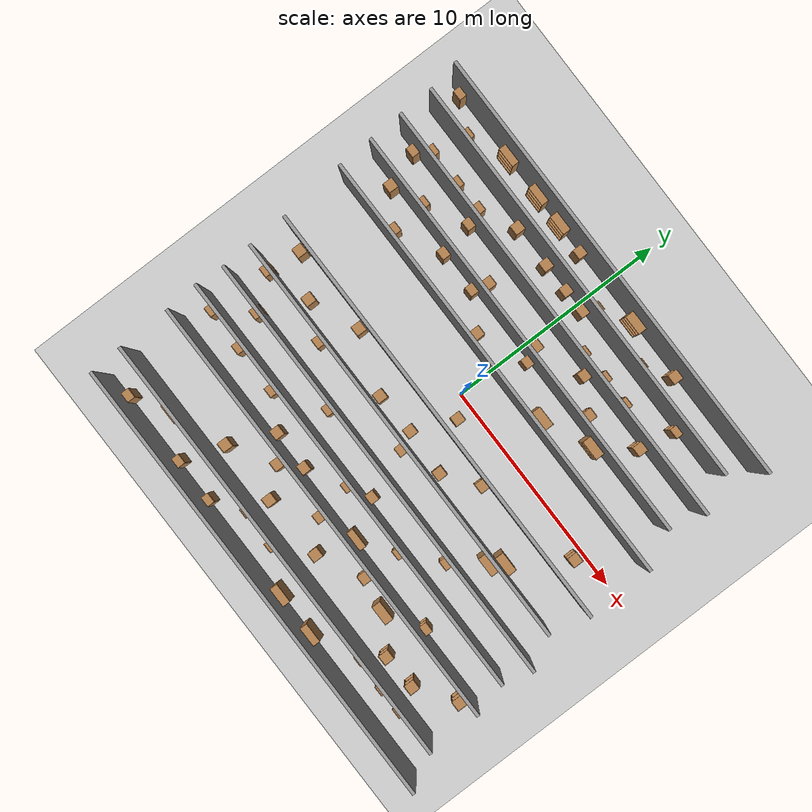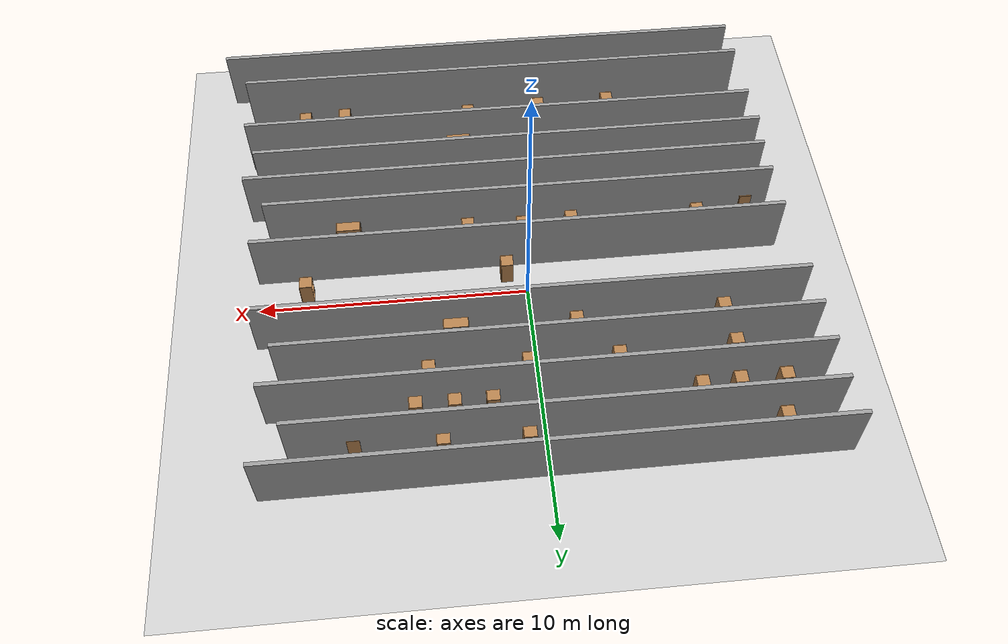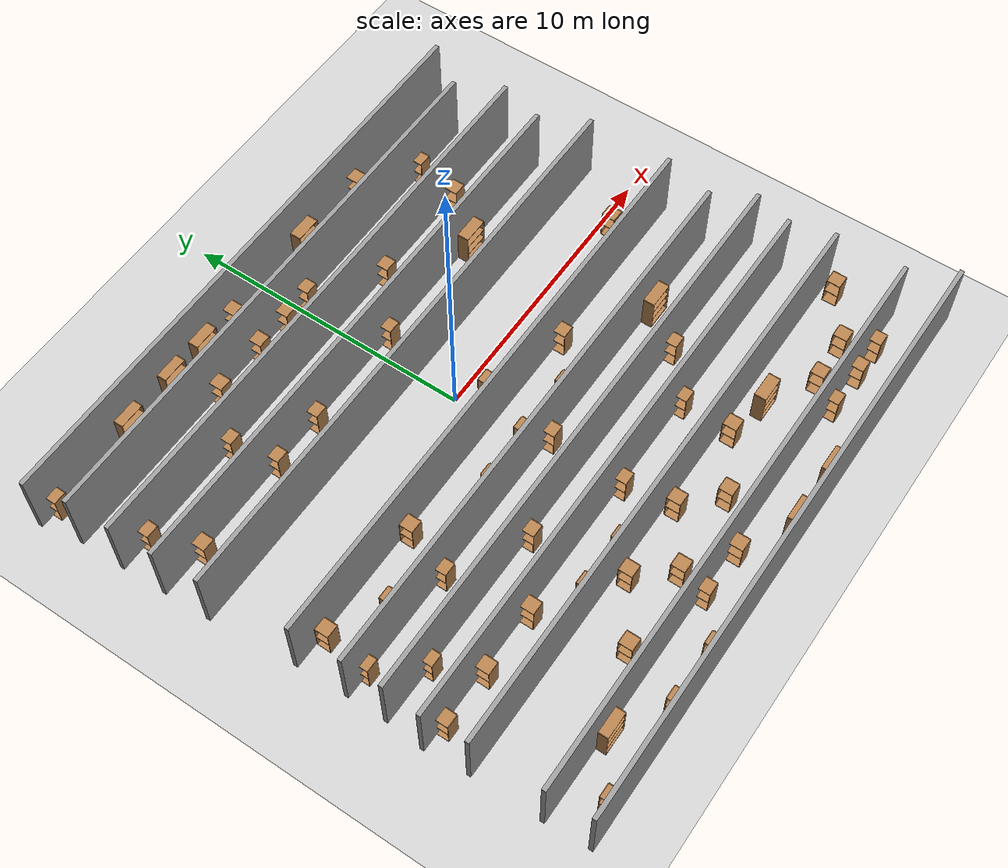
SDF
<sdf version="1.6">
 <world name="default">
  <light name="sun" type="directional">
   <pose>0 0 10 0 -0 0</pose>
   <diffuse>0.8 0.8 0.8 1</diffuse>
   <specular>0.2 0.2 0.2 1</specular>
   <attenuation>
    <range>1000</range>
    <constant>0.9</constant>
    <linear>0.01</linear>
    <quadratic>0.001</quadratic>
   </attenuation>
   <direction>-0.5 0.1 -0.9</direction>
  </light>
  <model name="ground_plane">
   <static>1</static>
   <link name="link">
    <collision name="collision">
     <geometry><plane><normal>0 0 1</normal><size>100 100</size></plane></geometry>
     <surface><friction><ode><mu>100</mu><mu2>50</mu2></ode></friction></surface>
    </collision>
    <visual name="visual">
     <cast_shadows>0</cast_shadows>
     <geometry><plane><normal>0 0 1</normal><size>100 100</size></plane></geometry>
     <material>
      <script><uri>file://media/materials/scripts/gazebo.material</uri><name>Gazebo/Grey</name></script>
     </material>
    </visual>
   </link>
  </model>
  <gravity>0 0 -9.8</gravity>
  <magnetic_field>6e-06 2.3e-05 -4.2e-05</magnetic_field>
  <atmosphere type="adiabatic"/>
  <physics name="default_physics" default="0" type="ode">
   <max_step_size>0.001</max_step_size>
   <real_time_factor>1</real_time_factor>
   <real_time_update_rate>1000</real_time_update_rate>
  </physics>
  <scene><ambient>0.4 0.4 0.4 1</ambient><background>0.7 0.7 0.7 1</background><shadows>1</shadows></scene>
  <audio><device>default</device></audio>
  <spherical_coordinates>
   <surface_model>EARTH_WGS84</surface_model>
   <latitude_deg>0</latitude_deg>
   <longitude_deg>0</longitude_deg>
   <elevation>0</elevation>
   <heading_deg>0</heading_deg>
  </spherical_coordinates>
  <model name="room17">
   <pose>0.441457 -1.72623 0 0 -0 0</pose>
   <link name="Wall_0">
    <collision name="Wall_0_Collision">
     <geometry><box><size>20.25 0.15 2.5</size></box></geometry>
     <pose>0 0 1.25 0 -0 0</pose>
    </collision>
    <visual name="Wall_0_Visual">
     <pose>0 0 1.25 0 -0 0</pose>
     <geometry><box><size>20.25 0.15 2.5</size></box></geometry>
     <material>
      <script><uri>file://media/materials/scripts/gazebo.material</uri><name>Gazebo/Grey</name></script>
      <ambient>1 1 1 1</ambient>
     </material>
     <meta><layer>0</layer></meta>
    </visual>
    <pose>-0.735743 9.32164 0 0 -0 0</pose>
   </link>
   <link name="Wall_10">
    <collision name="Wall_10_Collision">
     <geometry><box><size>19.25 0.15 2.5</size></box></geometry>
     <pose>0 0 1.25 0 -0 0</pose>
    </collision>
    <visual name="Wall_10_Visual">
     <pose>0 0 1.25 0 -0 0</pose>
     <geometry><box><size>19.25 0.15 2.5</size></box></geometry>
     <material>
      <script><uri>file://media/materials/scripts/gazebo.material</uri><name>Gazebo/Grey</name></script>
      <ambient>1 1 1 1</ambient>
     </material>
     <meta><layer>0</layer></meta>
    </visual>
    <pose>-0.865653 4.88056 0 0 -0 0</pose>
   </link>
   <link name="Wall_12">
    <collision name="Wall_12_Collision">
     <geometry><box><size>20 0.15 2.5</size></box></geometry>
     <pose>0 0 1.25 0 -0 0</pose>
    </collision>
    <visual name="Wall_12_Visual">
     <pose>0 0 1.25 0 -0 0</pose>
     <geometry><box><size>20 0.15 2.5</size></box></geometry>
     <material>
      <script><uri>file://media/materials/scripts/gazebo.material</uri><name>Gazebo/Grey</name></script>
      <ambient>1 1 1 1</ambient>
     </material>
     <meta><layer>0</layer></meta>
    </visual>
    <pose>-0.421261 3.30768 0 0 -0 0</pose>
   </link>
   <link name="Wall_14">
    <collision name="Wall_14_Collision">
     <geometry><box><size>19.75 0.15 2.5</size></box></geometry>
     <pose>0 0 1.25 0 -0 0</pose>
    </collision>
    <visual name="Wall_14_Visual">
     <pose>0 0 1.25 0 -0 0</pose>
     <geometry><box><size>19.75 0.15 2.5</size></box></geometry>
     <material>
      <script><uri>file://media/materials/scripts/gazebo.material</uri><name>Gazebo/Grey</name></script>
      <ambient>1 1 1 1</ambient>
     </material>
     <meta><layer>0</layer></meta>
    </visual>
    <pose>-0.268694 0.37009 0 0 -0 0</pose>
   </link>
   <link name="Wall_16">
    <collision name="Wall_16_Collision">
     <geometry><box><size>19.25 0.15 2.5</size></box></geometry>
     <pose>0 0 1.25 0 -0 0</pose>
    </collision>
    <visual name="Wall_16_Visual">
     <pose>0 0 1.25 0 -0 0</pose>
     <geometry><box><size>19.25 0.15 2.5</size></box></geometry>
     <material>
      <script><uri>file://media/materials/scripts/gazebo.material</uri><name>Gazebo/Grey</name></script>
      <ambient>1 1 1 1</ambient>
     </material>
     <meta><layer>0</layer></meta>
    </visual>
    <pose>-0.449302 -1.36471 0 0 -0 0</pose>
   </link>
   <link name="Wall_18">
    <collision name="Wall_18_Collision">
     <geometry><box><size>20 0.15 2.5</size></box></geometry>
     <pose>0 0 1.25 0 -0 0</pose>
    </collision>
    <visual name="Wall_18_Visual">
     <pose>0 0 1.25 0 -0 0</pose>
     <geometry><box><size>20 0.15 2.5</size></box></geometry>
     <material>
      <script><uri>file://media/materials/scripts/gazebo.material</uri><name>Gazebo/Grey</name></script>
      <ambient>1 1 1 1</ambient>
     </material>
     <meta><layer>0</layer></meta>
    </visual>
    <pose>-0.051172 -2.70628 0 0 -0 0</pose>
   </link>
   <link name="Wall_20">
    <collision name="Wall_20_Collision">
     <geometry><box><size>19.75 0.15 2.5</size></box></geometry>
     <pose>0 0 1.25 0 -0 0</pose>
    </collision>
    <visual name="Wall_20_Visual">
     <pose>0 0 1.25 0 -0 0</pose>
     <geometry><box><size>19.75 0.15 2.5</size></box></geometry>
     <material>
      <script><uri>file://media/materials/scripts/gazebo.material</uri><name>Gazebo/Grey</name></script>
      <ambient>1 1 1 1</ambient>
     </material>
     <meta><layer>0</layer></meta>
    </visual>
    <pose>-0.268694 -4.0016 0 0 -0 0</pose>
   </link>
   <link name="Wall_22">
    <collision name="Wall_22_Collision">
     <geometry><box><size>20 0.15 2.5</size></box></geometry>
     <pose>0 0 1.25 0 -0 0</pose>
    </collision>
    <visual name="Wall_22_Visual">
     <pose>0 0 1.25 0 -0 0</pose>
     <geometry><box><size>20 0.15 2.5</size></box></geometry>
     <material>
      <script><uri>file://media/materials/scripts/gazebo.material</uri><name>Gazebo/Grey</name></script>
      <ambient>1 1 1 1</ambient>
     </material>
     <meta><layer>0</layer></meta>
    </visual>
    <pose>-0.028041 -5.48195 0 0 -0 0</pose>
   </link>
   <link name="Wall_24">
    <collision name="Wall_24_Collision">
     <geometry><box><size>20 0.15 2.5</size></box></geometry>
     <pose>0 0 1.25 0 -0 0</pose>
    </collision>
    <visual name="Wall_24_Visual">
     <pose>0 0 1.25 0 -0 0</pose>
     <geometry><box><size>20 0.15 2.5</size></box></geometry>
     <material>
      <script><uri>file://media/materials/scripts/gazebo.material</uri><name>Gazebo/Grey</name></script>
      <ambient>1 1 1 1</ambient>
     </material>
     <meta><layer>0</layer></meta>
    </visual>
    <pose>0.01822 -7.84128 0 0 -0 0</pose>
   </link>
   <link name="Wall_26">
    <collision name="Wall_26_Collision">
     <geometry><box><size>20.75 0.15 2.5</size></box></geometry>
     <pose>0 0 1.25 0 -0 0</pose>
    </collision>
    <visual name="Wall_26_Visual">
     <pose>0 0 1.25 0 -0 0</pose>
     <geometry><box><size>20.75 0.15 2.5</size></box></geometry>
     <material>
      <script><uri>file://media/materials/scripts/gazebo.material</uri><name>Gazebo/Grey</name></script>
      <ambient>1 1 1 1</ambient>
     </material>
     <meta><layer>0</layer></meta>
    </visual>
    <pose>0.485743 -9.32164 0 0 -0 0</pose>
   </link>
   <link name="Wall_3">
    <collision name="Wall_3_Collision">
     <geometry><box><size>19 0.15 2.5</size></box></geometry>
     <pose>0 0 1.25 0 -0 0</pose>
    </collision>
    <visual name="Wall_3_Visual">
     <pose>0 0 1.25 0 -0 0</pose>
     <geometry><box><size>19 0.15 2.5</size></box></geometry>
     <material>
      <script><uri>file://media/materials/scripts/gazebo.material</uri><name>Gazebo/Grey</name></script>
      <ambient>1 1 1 1</ambient>
     </material>
     <meta><layer>0</layer></meta>
    </visual>
    <pose>-1.10631 7.9338 0 0 -0 0</pose>
   </link>
   <link name="Wall_5">
    <collision name="Wall_5_Collision">
     <geometry><box><size>19.75 0.15 2.5</size></box></geometry>
     <pose>0 0 1.25 0 -0 0</pose>
    </collision>
    <visual name="Wall_5_Visual">
     <pose>0 0 1.25 0 -0 0</pose>
     <geometry><box><size>19.75 0.15 2.5</size></box></geometry>
     <material>
      <script><uri>file://media/materials/scripts/gazebo.material</uri><name>Gazebo/Grey</name></script>
      <ambient>1 1 1 1</ambient>
     </material>
     <meta><layer>0</layer></meta>
    </visual>
    <pose>-0.685045 6.40718 0 0 -0 0</pose>
   </link>
   <static>1</static>
  </model>
  <model name="cabinet">
   <static>1</static>
   <link name="cabinet_bottom_plate">
    <inertial>
     <pose>0 0 -1 0 -0 0</pose>
     <inertia><ixx>2.05</ixx><ixy>0</ixy><ixz>0</ixz><iyy>2.05</iyy><iyz>0</iyz><izz>2.05</izz></inertia>
     <mass>25</mass>
    </inertial>
    <collision name="cabinet_bottom_plate_geom">
     <pose>0 0 0.01 0 -0 0</pose>
     <geometry><box><size>0.45 0.45 0.02</size></box></geometry>
    </collision>
    <visual name="cabinet_bottom_plate_geom_visual">
     <pose>0 0 0.01 0 -0 0</pose>
     <geometry><box><size>0.45 0.45 0.02</size></box></geometry>
     <material>
      <script><uri>file://media/materials/scripts/gazebo.material</uri><name>Gazebo/Wood</name></script>
     </material>
    </visual>
    <collision name="cabinet_bottom_plate_geom_cabinet_back_plate">
     <pose>0.235 0 0.51 0 -0 0</pose>
     <geometry><box><size>0.02 0.45 1.02</size></box></geometry>
    </collision>
    <visual name="cabinet_bottom_plate_geom_cabinet_back_plate_visual">
     <pose>0.235 0 0.51 0 -0 0</pose>
     <geometry><box><size>0.02 0.45 1.02</size></box></geometry>
     <material>
      <script><uri>file://media/materials/scripts/gazebo.material</uri><name>Gazebo/Wood</name></script>
     </material>
    </visual>
    <collision name="cabinet_bottom_plate_geom_cabinet_left_plate">
     <pose>0 0.235 0.51 0 -0 0</pose>
     <geometry><box><size>0.45 0.02 1.02</size></box></geometry>
    </collision>
    <visual name="cabinet_bottom_plate_geom_cabinet_left_plate_visual">
     <pose>0 0.235 0.51 0 -0 0</pose>
     <geometry><box><size>0.45 0.02 1.02</size></box></geometry>
     <material>
      <script><uri>file://media/materials/scripts/gazebo.material</uri><name>Gazebo/Wood</name></script>
     </material>
    </visual>
    <collision name="cabinet_bottom_plate_geom_cabinet_middle_plate">
     <pose>0 0 0.51 0 -0 0</pose>
     <geometry><box><size>0.45 0.45 0.02</size></box></geometry>
    </collision>
    <visual name="cabinet_bottom_plate_geom_cabinet_middle_plate_visual">
     <pose>0 0 0.51 0 -0 0</pose>
     <geometry><box><size>0.45 0.45 0.02</size></box></geometry>
     <material>
      <script><uri>file://media/materials/scripts/gazebo.material</uri><name>Gazebo/Wood</name></script>
     </material>
    </visual>
    <collision name="cabinet_bottom_plate_geom_cabinet_right_plate">
     <pose>0 -0.235 0.51 0 -0 0</pose>
     <geometry><box><size>0.45 0.02 1.02</size></box></geometry>
    </collision>
    <visual name="cabinet_bottom_plate_geom_cabinet_right_plate_visual">
     <pose>0 -0.235 0.51 0 -0 0</pose>
     <geometry><box><size>0.45 0.02 1.02</size></box></geometry>
     <material>
      <script><uri>file://media/materials/scripts/gazebo.material</uri><name>Gazebo/Wood</name></script>
     </material>
    </visual>
    <collision name="cabinet_bottom_plate_geom_cabinet_top_plate">
     <pose>0 0 1.01 0 -0 0</pose>
     <geometry><box><size>0.45 0.45 0.02</size></box></geometry>
    </collision>
    <visual name="cabinet_bottom_plate_geom_cabinet_top_plate_visual">
     <pose>0 0 1.01 0 -0 0</pose>
     <geometry><box><size>0.45 0.45 0.02</size></box></geometry>
     <material>
      <script><uri>file://media/materials/scripts/gazebo.material</uri><name>Gazebo/Wood</name></script>
     </material>
    </visual>
   </link>
   <pose>-8.18093 -10.8417 0 0 -0 0</pose>
  </model>
  <model name="bookshelf">
   <static>1</static>
   <link name="link">
    <inertial><mass>1</mass></inertial>
    <collision name="back">
     <pose>0 0.005 0.6 0 -0 0</pose>
     <geometry><box><size>0.9 0.01 1.2</size></box></geometry>
    </collision>
    <visual name="visual1">
     <pose>0 0.005 0.6 0 -0 0</pose>
     <geometry><box><size>0.9 0.01 1.2</size></box></geometry>
     <material>
      <script><uri>file://media/materials/scripts/gazebo.material</uri><name>Gazebo/Wood</name></script>
     </material>
    </visual>
    <collision name="left_side">
     <pose>0.45 -0.195 0.6 0 -0 0</pose>
     <geometry><box><size>0.02 0.4 1.2</size></box></geometry>
    </collision>
    <visual name="visual2">
     <pose>0.45 -0.195 0.6 0 -0 0</pose>
     <geometry><box><size>0.02 0.4 1.2</size></box></geometry>
     <material>
      <script><uri>file://media/materials/scripts/gazebo.material</uri><name>Gazebo/Wood</name></script>
     </material>
    </visual>
    <collision name="right_side">
     <pose>-0.45 -0.195 0.6 0 -0 0</pose>
     <geometry><box><size>0.02 0.4 1.2</size></box></geometry>
    </collision>
    <visual name="visual3">
     <pose>-0.45 -0.195 0.6 0 -0 0</pose>
     <geometry><box><size>0.02 0.4 1.2</size></box></geometry>
     <material>
      <script><uri>file://media/materials/scripts/gazebo.material</uri><name>Gazebo/Wood</name></script>
     </material>
    </visual>
    <collision name="bottom">
     <pose>0 -0.195 0.03 0 -0 0</pose>
     <geometry><box><size>0.88 0.4 0.06</size></box></geometry>
    </collision>
    <visual name="visual4">
     <pose>0 -0.195 0.03 0 -0 0</pose>
     <geometry><box><size>0.88 0.4 0.06</size></box></geometry>
     <material>
      <script><uri>file://media/materials/scripts/gazebo.material</uri><name>Gazebo/Wood</name></script>
     </material>
    </visual>
    <collision name="top">
     <pose>0 -0.195 1.19 0 -0 0</pose>
     <geometry><box><size>0.88 0.4 0.02</size></box></geometry>
    </collision>
    <visual name="visual5">
     <pose>0 -0.195 1.19 0 -0 0</pose>
     <geometry><box><size>0.88 0.4 0.02</size></box></geometry>
     <material>
      <script><uri>file://media/materials/scripts/gazebo.material</uri><name>Gazebo/Wood</name></script>
     </material>
    </visual>
    <collision name="low_shelf">
     <pose>0 -0.195 0.43 0 -0 0</pose>
     <geometry><box><size>0.88 0.4 0.02</size></box></geometry>
    </collision>
    <visual name="visual6">
     <pose>0 -0.195 0.43 0 -0 0</pose>
     <geometry><box><size>0.88 0.4 0.02</size></box></geometry>
     <material>
      <script><uri>file://media/materials/scripts/gazebo.material</uri><name>Gazebo/Wood</name></script>
     </material>
    </visual>
    <collision name="high_shelf">
     <pose>0 -0.195 0.8 0 -0 0</pose>
     <geometry><box><size>0.88 0.4 0.02</size></box></geometry>
    </collision>
    <visual name="visual7">
     <pose>0 -0.195 0.8 0 -0 0</pose>
     <geometry><box><size>0.88 0.4 0.02</size></box></geometry>
     <material>
      <script><uri>file://media/materials/scripts/gazebo.material</uri><name>Gazebo/Wood</name></script>
     </material>
    </visual>
   </link>
   <pose>-6.54125 -9.57718 0 0 -0 0</pose>
  </model>
  <model name="cabinet_0">
   <static>1</static>
   <link name="cabinet_bottom_plate">
    <inertial>
     <pose>0 0 -1 0 -0 0</pose>
     <inertia><ixx>2.05</ixx><ixy>0</ixy><ixz>0</ixz><iyy>2.05</iyy><iyz>0</iyz><izz>2.05</izz></inertia>
     <mass>25</mass>
    </inertial>
    <collision name="cabinet_bottom_plate_geom">
     <pose>0 0 0.01 0 -0 0</pose>
     <geometry><box><size>0.45 0.45 0.02</size></box></geometry>
    </collision>
    <visual name="cabinet_bottom_plate_geom_visual">
     <pose>0 0 0.01 0 -0 0</pose>
     <geometry><box><size>0.45 0.45 0.02</size></box></geometry>
     <material>
      <script><uri>file://media/materials/scripts/gazebo.material</uri><name>Gazebo/Wood</name></script>
     </material>
    </visual>
    <collision name="cabinet_bottom_plate_geom_cabinet_back_plate">
     <pose>0.235 0 0.51 0 -0 0</pose>
     <geometry><box><size>0.02 0.45 1.02</size></box></geometry>
    </collision>
    <visual name="cabinet_bottom_plate_geom_cabinet_back_plate_visual">
     <pose>0.235 0 0.51 0 -0 0</pose>
     <geometry><box><size>0.02 0.45 1.02</size></box></geometry>
     <material>
      <script><uri>file://media/materials/scripts/gazebo.material</uri><name>Gazebo/Wood</name></script>
     </material>
    </visual>
    <collision name="cabinet_bottom_plate_geom_cabinet_left_plate">
     <pose>0 0.235 0.51 0 -0 0</pose>
     <geometry><box><size>0.45 0.02 1.02</size></box></geometry>
    </collision>
    <visual name="cabinet_bottom_plate_geom_cabinet_left_plate_visual">
     <pose>0 0.235 0.51 0 -0 0</pose>
     <geometry><box><size>0.45 0.02 1.02</size></box></geometry>
     <material>
      <script><uri>file://media/materials/scripts/gazebo.material</uri><name>Gazebo/Wood</name></script>
     </material>
    </visual>
    <collision name="cabinet_bottom_plate_geom_cabinet_middle_plate">
     <pose>0 0 0.51 0 -0 0</pose>
     <geometry><box><size>0.45 0.45 0.02</size></box></geometry>
    </collision>
    <visual name="cabinet_bottom_plate_geom_cabinet_middle_plate_visual">
     <pose>0 0 0.51 0 -0 0</pose>
     <geometry><box><size>0.45 0.45 0.02</size></box></geometry>
     <material>
      <script><uri>file://media/materials/scripts/gazebo.material</uri><name>Gazebo/Wood</name></script>
     </material>
    </visual>
    <collision name="cabinet_bottom_plate_geom_cabinet_right_plate">
     <pose>0 -0.235 0.51 0 -0 0</pose>
     <geometry><box><size>0.45 0.02 1.02</size></box></geometry>
    </collision>
    <visual name="cabinet_bottom_plate_geom_cabinet_right_plate_visual">
     <pose>0 -0.235 0.51 0 -0 0</pose>
     <geometry><box><size>0.45 0.02 1.02</size></box></geometry>
     <material>
      <script><uri>file://media/materials/scripts/gazebo.material</uri><name>Gazebo/Wood</name></script>
     </material>
    </visual>
    <collision name="cabinet_bottom_plate_geom_cabinet_top_plate">
     <pose>0 0 1.01 0 -0 0</pose>
     <geometry><box><size>0.45 0.45 0.02</size></box></geometry>
    </collision>
    <visual name="cabinet_bottom_plate_geom_cabinet_top_plate_visual">
     <pose>0 0 1.01 0 -0 0</pose>
     <geometry><box><size>0.45 0.45 0.02</size></box></geometry>
     <material>
      <script><uri>file://media/materials/scripts/gazebo.material</uri><name>Gazebo/Wood</name></script>
     </material>
    </visual>
   </link>
   <pose>-4.82674 -10.8507 0 0 -0 0</pose>
  </model>
  <model name="cabinet_1">
   <static>1</static>
   <link name="cabinet_bottom_plate">
    <inertial>
     <pose>0 0 -1 0 -0 0</pose>
     <inertia><ixx>2.05</ixx><ixy>0</ixy><ixz>0</ixz><iyy>2.05</iyy><iyz>0</iyz><izz>2.05</izz></inertia>
     <mass>25</mass>
    </inertial>
    <collision name="cabinet_bottom_plate_geom">
     <pose>0 0 0.01 0 -0 0</pose>
     <geometry><box><size>0.45 0.45 0.02</size></box></geometry>
    </collision>
    <visual name="cabinet_bottom_plate_geom_visual">
     <pose>0 0 0.01 0 -0 0</pose>
     <geometry><box><size>0.45 0.45 0.02</size></box></geometry>
     <material>
      <script><uri>file://media/materials/scripts/gazebo.material</uri><name>Gazebo/Wood</name></script>
     </material>
    </visual>
    <collision name="cabinet_bottom_plate_geom_cabinet_back_plate">
     <pose>0.235 0 0.51 0 -0 0</pose>
     <geometry><box><size>0.02 0.45 1.02</size></box></geometry>
    </collision>
    <visual name="cabinet_bottom_plate_geom_cabinet_back_plate_visual">
     <pose>0.235 0 0.51 0 -0 0</pose>
     <geometry><box><size>0.02 0.45 1.02</size></box></geometry>
     <material>
      <script><uri>file://media/materials/scripts/gazebo.material</uri><name>Gazebo/Wood</name></script>
     </material>
    </visual>
    <collision name="cabinet_bottom_plate_geom_cabinet_left_plate">
     <pose>0 0.235 0.51 0 -0 0</pose>
     <geometry><box><size>0.45 0.02 1.02</size></box></geometry>
    </collision>
    <visual name="cabinet_bottom_plate_geom_cabinet_left_plate_visual">
     <pose>0 0.235 0.51 0 -0 0</pose>
     <geometry><box><size>0.45 0.02 1.02</size></box></geometry>
     <material>
      <script><uri>file://media/materials/scripts/gazebo.material</uri><name>Gazebo/Wood</name></script>
     </material>
    </visual>
    <collision name="cabinet_bottom_plate_geom_cabinet_middle_plate">
     <pose>0 0 0.51 0 -0 0</pose>
     <geometry><box><size>0.45 0.45 0.02</size></box></geometry>
    </collision>
    <visual name="cabinet_bottom_plate_geom_cabinet_middle_plate_visual">
     <pose>0 0 0.51 0 -0 0</pose>
     <geometry><box><size>0.45 0.45 0.02</size></box></geometry>
     <material>
      <script><uri>file://media/materials/scripts/gazebo.material</uri><name>Gazebo/Wood</name></script>
     </material>
    </visual>
    <collision name="cabinet_bottom_plate_geom_cabinet_right_plate">
     <pose>0 -0.235 0.51 0 -0 0</pose>
     <geometry><box><size>0.45 0.02 1.02</size></box></geometry>
    </collision>
    <visual name="cabinet_bottom_plate_geom_cabinet_right_plate_visual">
     <pose>0 -0.235 0.51 0 -0 0</pose>
     <geometry><box><size>0.45 0.02 1.02</size></box></geometry>
     <material>
      <script><uri>file://media/materials/scripts/gazebo.material</uri><name>Gazebo/Wood</name></script>
     </material>
    </visual>
    <collision name="cabinet_bottom_plate_geom_cabinet_top_plate">
     <pose>0 0 1.01 0 -0 0</pose>
     <geometry><box><size>0.45 0.45 0.02</size></box></geometry>
    </collision>
    <visual name="cabinet_bottom_plate_geom_cabinet_top_plate_visual">
     <pose>0 0 1.01 0 -0 0</pose>
     <geometry><box><size>0.45 0.45 0.02</size></box></geometry>
     <material>
      <script><uri>file://media/materials/scripts/gazebo.material</uri><name>Gazebo/Wood</name></script>
     </material>
    </visual>
   </link>
   <pose>-2.84449 -10.8692 0 0 -0 0</pose>
  </model>
  <model name="cabinet_2">
   <static>1</static>
   <link name="cabinet_bottom_plate">
    <inertial>
     <pose>0 0 -1 0 -0 0</pose>
     <inertia><ixx>2.05</ixx><ixy>0</ixy><ixz>0</ixz><iyy>2.05</iyy><iyz>0</iyz><izz>2.05</izz></inertia>
     <mass>25</mass>
    </inertial>
    <collision name="cabinet_bottom_plate_geom">
     <pose>0 0 0.01 0 -0 0</pose>
     <geometry><box><size>0.45 0.45 0.02</size></box></geometry>
    </collision>
    <visual name="cabinet_bottom_plate_geom_visual">
     <pose>0 0 0.01 0 -0 0</pose>
     <geometry><box><size>0.45 0.45 0.02</size></box></geometry>
     <material>
      <script><uri>file://media/materials/scripts/gazebo.material</uri><name>Gazebo/Wood</name></script>
     </material>
    </visual>
    <collision name="cabinet_bottom_plate_geom_cabinet_back_plate">
     <pose>0.235 0 0.51 0 -0 0</pose>
     <geometry><box><size>0.02 0.45 1.02</size></box></geometry>
    </collision>
    <visual name="cabinet_bottom_plate_geom_cabinet_back_plate_visual">
     <pose>0.235 0 0.51 0 -0 0</pose>
     <geometry><box><size>0.02 0.45 1.02</size></box></geometry>
     <material>
      <script><uri>file://media/materials/scripts/gazebo.material</uri><name>Gazebo/Wood</name></script>
     </material>
    </visual>
    <collision name="cabinet_bottom_plate_geom_cabinet_left_plate">
     <pose>0 0.235 0.51 0 -0 0</pose>
     <geometry><box><size>0.45 0.02 1.02</size></box></geometry>
    </collision>
    <visual name="cabinet_bottom_plate_geom_cabinet_left_plate_visual">
     <pose>0 0.235 0.51 0 -0 0</pose>
     <geometry><box><size>0.45 0.02 1.02</size></box></geometry>
     <material>
      <script><uri>file://media/materials/scripts/gazebo.material</uri><name>Gazebo/Wood</name></script>
     </material>
    </visual>
    <collision name="cabinet_bottom_plate_geom_cabinet_middle_plate">
     <pose>0 0 0.51 0 -0 0</pose>
     <geometry><box><size>0.45 0.45 0.02</size></box></geometry>
    </collision>
    <visual name="cabinet_bottom_plate_geom_cabinet_middle_plate_visual">
     <pose>0 0 0.51 0 -0 0</pose>
     <geometry><box><size>0.45 0.45 0.02</size></box></geometry>
     <material>
      <script><uri>file://media/materials/scripts/gazebo.material</uri><name>Gazebo/Wood</name></script>
     </material>
    </visual>
    <collision name="cabinet_bottom_plate_geom_cabinet_right_plate">
     <pose>0 -0.235 0.51 0 -0 0</pose>
     <geometry><box><size>0.45 0.02 1.02</size></box></geometry>
    </collision>
    <visual name="cabinet_bottom_plate_geom_cabinet_right_plate_visual">
     <pose>0 -0.235 0.51 0 -0 0</pose>
     <geometry><box><size>0.45 0.02 1.02</size></box></geometry>
     <material>
      <script><uri>file://media/materials/scripts/gazebo.material</uri><name>Gazebo/Wood</name></script>
     </material>
    </visual>
    <collision name="cabinet_bottom_plate_geom_cabinet_top_plate">
     <pose>0 0 1.01 0 -0 0</pose>
     <geometry><box><size>0.45 0.45 0.02</size></box></geometry>
    </collision>
    <visual name="cabinet_bottom_plate_geom_cabinet_top_plate_visual">
     <pose>0 0 1.01 0 -0 0</pose>
     <geometry><box><size>0.45 0.45 0.02</size></box></geometry>
     <material>
      <script><uri>file://media/materials/scripts/gazebo.material</uri><name>Gazebo/Wood</name></script>
     </material>
    </visual>
   </link>
   <pose>-1.52112 -9.79188 0 0 -0 0</pose>
  </model>
  <model name="cabinet_3">
   <static>1</static>
   <link name="cabinet_bottom_plate">
    <inertial>
     <pose>0 0 -1 0 -0 0</pose>
     <inertia><ixx>2.05</ixx><ixy>0</ixy><ixz>0</ixz><iyy>2.05</iyy><iyz>0</iyz><izz>2.05</izz></inertia>
     <mass>25</mass>
    </inertial>
    <collision name="cabinet_bottom_plate_geom">
     <pose>0 0 0.01 0 -0 0</pose>
     <geometry><box><size>0.45 0.45 0.02</size></box></geometry>
    </collision>
    <visual name="cabinet_bottom_plate_geom_visual">
     <pose>0 0 0.01 0 -0 0</pose>
     <geometry><box><size>0.45 0.45 0.02</size></box></geometry>
     <material>
      <script><uri>file://media/materials/scripts/gazebo.material</uri><name>Gazebo/Wood</name></script>
     </material>
    </visual>
    <collision name="cabinet_bottom_plate_geom_cabinet_back_plate">
     <pose>0.235 0 0.51 0 -0 0</pose>
     <geometry><box><size>0.02 0.45 1.02</size></box></geometry>
    </collision>
    <visual name="cabinet_bottom_plate_geom_cabinet_back_plate_visual">
     <pose>0.235 0 0.51 0 -0 0</pose>
     <geometry><box><size>0.02 0.45 1.02</size></box></geometry>
     <material>
      <script><uri>file://media/materials/scripts/gazebo.material</uri><name>Gazebo/Wood</name></script>
     </material>
    </visual>
    <collision name="cabinet_bottom_plate_geom_cabinet_left_plate">
     <pose>0 0.235 0.51 0 -0 0</pose>
     <geometry><box><size>0.45 0.02 1.02</size></box></geometry>
    </collision>
    <visual name="cabinet_bottom_plate_geom_cabinet_left_plate_visual">
     <pose>0 0.235 0.51 0 -0 0</pose>
     <geometry><box><size>0.45 0.02 1.02</size></box></geometry>
     <material>
      <script><uri>file://media/materials/scripts/gazebo.material</uri><name>Gazebo/Wood</name></script>
     </material>
    </visual>
    <collision name="cabinet_bottom_plate_geom_cabinet_middle_plate">
     <pose>0 0 0.51 0 -0 0</pose>
     <geometry><box><size>0.45 0.45 0.02</size></box></geometry>
    </collision>
    <visual name="cabinet_bottom_plate_geom_cabinet_middle_plate_visual">
     <pose>0 0 0.51 0 -0 0</pose>
     <geometry><box><size>0.45 0.45 0.02</size></box></geometry>
     <material>
      <script><uri>file://media/materials/scripts/gazebo.material</uri><name>Gazebo/Wood</name></script>
     </material>
    </visual>
    <collision name="cabinet_bottom_plate_geom_cabinet_right_plate">
     <pose>0 -0.235 0.51 0 -0 0</pose>
     <geometry><box><size>0.45 0.02 1.02</size></box></geometry>
    </collision>
    <visual name="cabinet_bottom_plate_geom_cabinet_right_plate_visual">
     <pose>0 -0.235 0.51 0 -0 0</pose>
     <geometry><box><size>0.45 0.02 1.02</size></box></geometry>
     <material>
      <script><uri>file://media/materials/scripts/gazebo.material</uri><name>Gazebo/Wood</name></script>
     </material>
    </visual>
    <collision name="cabinet_bottom_plate_geom_cabinet_top_plate">
     <pose>0 0 1.01 0 -0 0</pose>
     <geometry><box><size>0.45 0.45 0.02</size></box></geometry>
    </collision>
    <visual name="cabinet_bottom_plate_geom_cabinet_top_plate_visual">
     <pose>0 0 1.01 0 -0 0</pose>
     <geometry><box><size>0.45 0.45 0.02</size></box></geometry>
     <material>
      <script><uri>file://media/materials/scripts/gazebo.material</uri><name>Gazebo/Wood</name></script>
     </material>
    </visual>
   </link>
   <pose>0.198754 -9.8582 0 0 -0 0</pose>
  </model>
  <model name="bookshelf_0">
   <static>1</static>
   <link name="link">
    <inertial><mass>1</mass></inertial>
    <collision name="back">
     <pose>0 0.005 0.6 0 -0 0</pose>
     <geometry><box><size>0.9 0.01 1.2</size></box></geometry>
    </collision>
    <visual name="visual1">
     <pose>0 0.005 0.6 0 -0 0</pose>
     <geometry><box><size>0.9 0.01 1.2</size></box></geometry>
     <material>
      <script><uri>file://media/materials/scripts/gazebo.material</uri><name>Gazebo/Wood</name></script>
     </material>
    </visual>
    <collision name="left_side">
     <pose>0.45 -0.195 0.6 0 -0 0</pose>
     <geometry><box><size>0.02 0.4 1.2</size></box></geometry>
    </collision>
    <visual name="visual2">
     <pose>0.45 -0.195 0.6 0 -0 0</pose>
     <geometry><box><size>0.02 0.4 1.2</size></box></geometry>
     <material>
      <script><uri>file://media/materials/scripts/gazebo.material</uri><name>Gazebo/Wood</name></script>
     </material>
    </visual>
    <collision name="right_side">
     <pose>-0.45 -0.195 0.6 0 -0 0</pose>
     <geometry><box><size>0.02 0.4 1.2</size></box></geometry>
    </collision>
    <visual name="visual3">
     <pose>-0.45 -0.195 0.6 0 -0 0</pose>
     <geometry><box><size>0.02 0.4 1.2</size></box></geometry>
     <material>
      <script><uri>file://media/materials/scripts/gazebo.material</uri><name>Gazebo/Wood</name></script>
     </material>
    </visual>
    <collision name="bottom">
     <pose>0 -0.195 0.03 0 -0 0</pose>
     <geometry><box><size>0.88 0.4 0.06</size></box></geometry>
    </collision>
    <visual name="visual4">
     <pose>0 -0.195 0.03 0 -0 0</pose>
     <geometry><box><size>0.88 0.4 0.06</size></box></geometry>
     <material>
      <script><uri>file://media/materials/scripts/gazebo.material</uri><name>Gazebo/Wood</name></script>
     </material>
    </visual>
    <collision name="top">
     <pose>0 -0.195 1.19 0 -0 0</pose>
     <geometry><box><size>0.88 0.4 0.02</size></box></geometry>
    </collision>
    <visual name="visual5">
     <pose>0 -0.195 1.19 0 -0 0</pose>
     <geometry><box><size>0.88 0.4 0.02</size></box></geometry>
     <material>
      <script><uri>file://media/materials/scripts/gazebo.material</uri><name>Gazebo/Wood</name></script>
     </material>
    </visual>
    <collision name="low_shelf">
     <pose>0 -0.195 0.43 0 -0 0</pose>
     <geometry><box><size>0.88 0.4 0.02</size></box></geometry>
    </collision>
    <visual name="visual6">
     <pose>0 -0.195 0.43 0 -0 0</pose>
     <geometry><box><size>0.88 0.4 0.02</size></box></geometry>
     <material>
      <script><uri>file://media/materials/scripts/gazebo.material</uri><name>Gazebo/Wood</name></script>
     </material>
    </visual>
    <collision name="high_shelf">
     <pose>0 -0.195 0.8 0 -0 0</pose>
     <geometry><box><size>0.88 0.4 0.02</size></box></geometry>
    </collision>
    <visual name="visual7">
     <pose>0 -0.195 0.8 0 -0 0</pose>
     <geometry><box><size>0.88 0.4 0.02</size></box></geometry>
     <material>
      <script><uri>file://media/materials/scripts/gazebo.material</uri><name>Gazebo/Wood</name></script>
     </material>
    </visual>
   </link>
   <pose>2.01191 -10.6265 0 0 -0 0</pose>
  </model>
  <model name="bookshelf_1">
   <static>1</static>
   <link name="link">
    <inertial><mass>1</mass></inertial>
    <collision name="back">
     <pose>0 0.005 0.6 0 -0 0</pose>
     <geometry><box><size>0.9 0.01 1.2</size></box></geometry>
    </collision>
    <visual name="visual1">
     <pose>0 0.005 0.6 0 -0 0</pose>
     <geometry><box><size>0.9 0.01 1.2</size></box></geometry>
     <material>
      <script><uri>file://media/materials/scripts/gazebo.material</uri><name>Gazebo/Wood</name></script>
     </material>
    </visual>
    <collision name="left_side">
     <pose>0.45 -0.195 0.6 0 -0 0</pose>
     <geometry><box><size>0.02 0.4 1.2</size></box></geometry>
    </collision>
    <visual name="visual2">
     <pose>0.45 -0.195 0.6 0 -0 0</pose>
     <geometry><box><size>0.02 0.4 1.2</size></box></geometry>
     <material>
      <script><uri>file://media/materials/scripts/gazebo.material</uri><name>Gazebo/Wood</name></script>
     </material>
    </visual>
    <collision name="right_side">
     <pose>-0.45 -0.195 0.6 0 -0 0</pose>
     <geometry><box><size>0.02 0.4 1.2</size></box></geometry>
    </collision>
    <visual name="visual3">
     <pose>-0.45 -0.195 0.6 0 -0 0</pose>
     <geometry><box><size>0.02 0.4 1.2</size></box></geometry>
     <material>
      <script><uri>file://media/materials/scripts/gazebo.material</uri><name>Gazebo/Wood</name></script>
     </material>
    </visual>
    <collision name="bottom">
     <pose>0 -0.195 0.03 0 -0 0</pose>
     <geometry><box><size>0.88 0.4 0.06</size></box></geometry>
    </collision>
    <visual name="visual4">
     <pose>0 -0.195 0.03 0 -0 0</pose>
     <geometry><box><size>0.88 0.4 0.06</size></box></geometry>
     <material>
      <script><uri>file://media/materials/scripts/gazebo.material</uri><name>Gazebo/Wood</name></script>
     </material>
    </visual>
    <collision name="top">
     <pose>0 -0.195 1.19 0 -0 0</pose>
     <geometry><box><size>0.88 0.4 0.02</size></box></geometry>
    </collision>
    <visual name="visual5">
     <pose>0 -0.195 1.19 0 -0 0</pose>
     <geometry><box><size>0.88 0.4 0.02</size></box></geometry>
     <material>
      <script><uri>file://media/materials/scripts/gazebo.material</uri><name>Gazebo/Wood</name></script>
     </material>
    </visual>
    <collision name="low_shelf">
     <pose>0 -0.195 0.43 0 -0 0</pose>
     <geometry><box><size>0.88 0.4 0.02</size></box></geometry>
    </collision>
    <visual name="visual6">
     <pose>0 -0.195 0.43 0 -0 0</pose>
     <geometry><box><size>0.88 0.4 0.02</size></box></geometry>
     <material>
      <script><uri>file://media/materials/scripts/gazebo.material</uri><name>Gazebo/Wood</name></script>
     </material>
    </visual>
    <collision name="high_shelf">
     <pose>0 -0.195 0.8 0 -0 0</pose>
     <geometry><box><size>0.88 0.4 0.02</size></box></geometry>
    </collision>
    <visual name="visual7">
     <pose>0 -0.195 0.8 0 -0 0</pose>
     <geometry><box><size>0.88 0.4 0.02</size></box></geometry>
     <material>
      <script><uri>file://media/materials/scripts/gazebo.material</uri><name>Gazebo/Wood</name></script>
     </material>
    </visual>
   </link>
   <pose>4.02228 -10.6454 0 0 -0 0</pose>
  </model>
  <model name="cabinet_4">
   <static>1</static>
   <link name="cabinet_bottom_plate">
    <inertial>
     <pose>0 0 -1 0 -0 0</pose>
     <inertia><ixx>2.05</ixx><ixy>0</ixy><ixz>0</ixz><iyy>2.05</iyy><iyz>0</iyz><izz>2.05</izz></inertia>
     <mass>25</mass>
    </inertial>
    <collision name="cabinet_bottom_plate_geom">
     <pose>0 0 0.01 0 -0 0</pose>
     <geometry><box><size>0.45 0.45 0.02</size></box></geometry>
    </collision>
    <visual name="cabinet_bottom_plate_geom_visual">
     <pose>0 0 0.01 0 -0 0</pose>
     <geometry><box><size>0.45 0.45 0.02</size></box></geometry>
     <material>
      <script><uri>file://media/materials/scripts/gazebo.material</uri><name>Gazebo/Wood</name></script>
     </material>
    </visual>
    <collision name="cabinet_bottom_plate_geom_cabinet_back_plate">
     <pose>0.235 0 0.51 0 -0 0</pose>
     <geometry><box><size>0.02 0.45 1.02</size></box></geometry>
    </collision>
    <visual name="cabinet_bottom_plate_geom_cabinet_back_plate_visual">
     <pose>0.235 0 0.51 0 -0 0</pose>
     <geometry><box><size>0.02 0.45 1.02</size></box></geometry>
     <material>
      <script><uri>file://media/materials/scripts/gazebo.material</uri><name>Gazebo/Wood</name></script>
     </material>
    </visual>
    <collision name="cabinet_bottom_plate_geom_cabinet_left_plate">
     <pose>0 0.235 0.51 0 -0 0</pose>
     <geometry><box><size>0.45 0.02 1.02</size></box></geometry>
    </collision>
    <visual name="cabinet_bottom_plate_geom_cabinet_left_plate_visual">
     <pose>0 0.235 0.51 0 -0 0</pose>
     <geometry><box><size>0.45 0.02 1.02</size></box></geometry>
     <material>
      <script><uri>file://media/materials/scripts/gazebo.material</uri><name>Gazebo/Wood</name></script>
     </material>
    </visual>
    <collision name="cabinet_bottom_plate_geom_cabinet_middle_plate">
     <pose>0 0 0.51 0 -0 0</pose>
     <geometry><box><size>0.45 0.45 0.02</size></box></geometry>
    </collision>
    <visual name="cabinet_bottom_plate_geom_cabinet_middle_plate_visual">
     <pose>0 0 0.51 0 -0 0</pose>
     <geometry><box><size>0.45 0.45 0.02</size></box></geometry>
     <material>
      <script><uri>file://media/materials/scripts/gazebo.material</uri><name>Gazebo/Wood</name></script>
     </material>
    </visual>
    <collision name="cabinet_bottom_plate_geom_cabinet_right_plate">
     <pose>0 -0.235 0.51 0 -0 0</pose>
     <geometry><box><size>0.45 0.02 1.02</size></box></geometry>
    </collision>
    <visual name="cabinet_bottom_plate_geom_cabinet_right_plate_visual">
     <pose>0 -0.235 0.51 0 -0 0</pose>
     <geometry><box><size>0.45 0.02 1.02</size></box></geometry>
     <material>
      <script><uri>file://media/materials/scripts/gazebo.material</uri><name>Gazebo/Wood</name></script>
     </material>
    </visual>
    <collision name="cabinet_bottom_plate_geom_cabinet_top_plate">
     <pose>0 0 1.01 0 -0 0</pose>
     <geometry><box><size>0.45 0.45 0.02</size></box></geometry>
    </collision>
    <visual name="cabinet_bottom_plate_geom_cabinet_top_plate_visual">
     <pose>0 0 1.01 0 -0 0</pose>
     <geometry><box><size>0.45 0.45 0.02</size></box></geometry>
     <material>
      <script><uri>file://media/materials/scripts/gazebo.material</uri><name>Gazebo/Wood</name></script>
     </material>
    </visual>
   </link>
   <pose>6.07432 -9.76061 0 0 -0 0</pose>
  </model>
  <model name="cabinet_5">
   <static>1</static>
   <link name="cabinet_bottom_plate">
    <inertial>
     <pose>0 0 -1 0 -0 0</pose>
     <inertia><ixx>2.05</ixx><ixy>0</ixy><ixz>0</ixz><iyy>2.05</iyy><iyz>0</iyz><izz>2.05</izz></inertia>
     <mass>25</mass>
    </inertial>
    <collision name="cabinet_bottom_plate_geom">
     <pose>0 0 0.01 0 -0 0</pose>
     <geometry><box><size>0.45 0.45 0.02</size></box></geometry>
    </collision>
    <visual name="cabinet_bottom_plate_geom_visual">
     <pose>0 0 0.01 0 -0 0</pose>
     <geometry><box><size>0.45 0.45 0.02</size></box></geometry>
     <material>
      <script><uri>file://media/materials/scripts/gazebo.material</uri><name>Gazebo/Wood</name></script>
     </material>
    </visual>
    <collision name="cabinet_bottom_plate_geom_cabinet_back_plate">
     <pose>0.235 0 0.51 0 -0 0</pose>
     <geometry><box><size>0.02 0.45 1.02</size></box></geometry>
    </collision>
    <visual name="cabinet_bottom_plate_geom_cabinet_back_plate_visual">
     <pose>0.235 0 0.51 0 -0 0</pose>
     <geometry><box><size>0.02 0.45 1.02</size></box></geometry>
     <material>
      <script><uri>file://media/materials/scripts/gazebo.material</uri><name>Gazebo/Wood</name></script>
     </material>
    </visual>
    <collision name="cabinet_bottom_plate_geom_cabinet_left_plate">
     <pose>0 0.235 0.51 0 -0 0</pose>
     <geometry><box><size>0.45 0.02 1.02</size></box></geometry>
    </collision>
    <visual name="cabinet_bottom_plate_geom_cabinet_left_plate_visual">
     <pose>0 0.235 0.51 0 -0 0</pose>
     <geometry><box><size>0.45 0.02 1.02</size></box></geometry>
     <material>
      <script><uri>file://media/materials/scripts/gazebo.material</uri><name>Gazebo/Wood</name></script>
     </material>
    </visual>
    <collision name="cabinet_bottom_plate_geom_cabinet_middle_plate">
     <pose>0 0 0.51 0 -0 0</pose>
     <geometry><box><size>0.45 0.45 0.02</size></box></geometry>
    </collision>
    <visual name="cabinet_bottom_plate_geom_cabinet_middle_plate_visual">
     <pose>0 0 0.51 0 -0 0</pose>
     <geometry><box><size>0.45 0.45 0.02</size></box></geometry>
     <material>
      <script><uri>file://media/materials/scripts/gazebo.material</uri><name>Gazebo/Wood</name></script>
     </material>
    </visual>
    <collision name="cabinet_bottom_plate_geom_cabinet_right_plate">
     <pose>0 -0.235 0.51 0 -0 0</pose>
     <geometry><box><size>0.45 0.02 1.02</size></box></geometry>
    </collision>
    <visual name="cabinet_bottom_plate_geom_cabinet_right_plate_visual">
     <pose>0 -0.235 0.51 0 -0 0</pose>
     <geometry><box><size>0.45 0.02 1.02</size></box></geometry>
     <material>
      <script><uri>file://media/materials/scripts/gazebo.material</uri><name>Gazebo/Wood</name></script>
     </material>
    </visual>
    <collision name="cabinet_bottom_plate_geom_cabinet_top_plate">
     <pose>0 0 1.01 0 -0 0</pose>
     <geometry><box><size>0.45 0.45 0.02</size></box></geometry>
    </collision>
    <visual name="cabinet_bottom_plate_geom_cabinet_top_plate_visual">
     <pose>0 0 1.01 0 -0 0</pose>
     <geometry><box><size>0.45 0.45 0.02</size></box></geometry>
     <material>
      <script><uri>file://media/materials/scripts/gazebo.material</uri><name>Gazebo/Wood</name></script>
     </material>
    </visual>
   </link>
   <pose>7.54723 -9.811 0 0 -0 0</pose>
  </model>
  <model name="cabinet_6">
   <static>1</static>
   <link name="cabinet_bottom_plate">
    <inertial>
     <pose>0 0 -1 0 -0 0</pose>
     <inertia><ixx>2.05</ixx><ixy>0</ixy><ixz>0</ixz><iyy>2.05</iyy><iyz>0</iyz><izz>2.05</izz></inertia>
     <mass>25</mass>
    </inertial>
    <collision name="cabinet_bottom_plate_geom">
     <pose>0 0 0.01 0 -0 0</pose>
     <geometry><box><size>0.45 0.45 0.02</size></box></geometry>
    </collision>
    <visual name="cabinet_bottom_plate_geom_visual">
     <pose>0 0 0.01 0 -0 0</pose>
     <geometry><box><size>0.45 0.45 0.02</size></box></geometry>
     <material>
      <script><uri>file://media/materials/scripts/gazebo.material</uri><name>Gazebo/Wood</name></script>
     </material>
    </visual>
    <collision name="cabinet_bottom_plate_geom_cabinet_back_plate">
     <pose>0.235 0 0.51 0 -0 0</pose>
     <geometry><box><size>0.02 0.45 1.02</size></box></geometry>
    </collision>
    <visual name="cabinet_bottom_plate_geom_cabinet_back_plate_visual">
     <pose>0.235 0 0.51 0 -0 0</pose>
     <geometry><box><size>0.02 0.45 1.02</size></box></geometry>
     <material>
      <script><uri>file://media/materials/scripts/gazebo.material</uri><name>Gazebo/Wood</name></script>
     </material>
    </visual>
    <collision name="cabinet_bottom_plate_geom_cabinet_left_plate">
     <pose>0 0.235 0.51 0 -0 0</pose>
     <geometry><box><size>0.45 0.02 1.02</size></box></geometry>
    </collision>
    <visual name="cabinet_bottom_plate_geom_cabinet_left_plate_visual">
     <pose>0 0.235 0.51 0 -0 0</pose>
     <geometry><box><size>0.45 0.02 1.02</size></box></geometry>
     <material>
      <script><uri>file://media/materials/scripts/gazebo.material</uri><name>Gazebo/Wood</name></script>
     </material>
    </visual>
    <collision name="cabinet_bottom_plate_geom_cabinet_middle_plate">
     <pose>0 0 0.51 0 -0 0</pose>
     <geometry><box><size>0.45 0.45 0.02</size></box></geometry>
    </collision>
    <visual name="cabinet_bottom_plate_geom_cabinet_middle_plate_visual">
     <pose>0 0 0.51 0 -0 0</pose>
     <geometry><box><size>0.45 0.45 0.02</size></box></geometry>
     <material>
      <script><uri>file://media/materials/scripts/gazebo.material</uri><name>Gazebo/Wood</name></script>
     </material>
    </visual>
    <collision name="cabinet_bottom_plate_geom_cabinet_right_plate">
     <pose>0 -0.235 0.51 0 -0 0</pose>
     <geometry><box><size>0.45 0.02 1.02</size></box></geometry>
    </collision>
    <visual name="cabinet_bottom_plate_geom_cabinet_right_plate_visual">
     <pose>0 -0.235 0.51 0 -0 0</pose>
     <geometry><box><size>0.45 0.02 1.02</size></box></geometry>
     <material>
      <script><uri>file://media/materials/scripts/gazebo.material</uri><name>Gazebo/Wood</name></script>
     </material>
    </visual>
    <collision name="cabinet_bottom_plate_geom_cabinet_top_plate">
     <pose>0 0 1.01 0 -0 0</pose>
     <geometry><box><size>0.45 0.45 0.02</size></box></geometry>
    </collision>
    <visual name="cabinet_bottom_plate_geom_cabinet_top_plate_visual">
     <pose>0 0 1.01 0 -0 0</pose>
     <geometry><box><size>0.45 0.45 0.02</size></box></geometry>
     <material>
      <script><uri>file://media/materials/scripts/gazebo.material</uri><name>Gazebo/Wood</name></script>
     </material>
    </visual>
   </link>
   <pose>8.70569 -9.80026 0 0 -0 0</pose>
  </model>
  <model name="cabinet_7">
   <static>1</static>
   <link name="cabinet_bottom_plate">
    <inertial>
     <pose>0 0 -1 0 -0 0</pose>
     <inertia><ixx>2.05</ixx><ixy>0</ixy><ixz>0</ixz><iyy>2.05</iyy><iyz>0</iyz><izz>2.05</izz></inertia>
     <mass>25</mass>
    </inertial>
    <collision name="cabinet_bottom_plate_geom">
     <pose>0 0 0.01 0 -0 0</pose>
     <geometry><box><size>0.45 0.45 0.02</size></box></geometry>
    </collision>
    <visual name="cabinet_bottom_plate_geom_visual">
     <pose>0 0 0.01 0 -0 0</pose>
     <geometry><box><size>0.45 0.45 0.02</size></box></geometry>
     <material>
      <script><uri>file://media/materials/scripts/gazebo.material</uri><name>Gazebo/Wood</name></script>
     </material>
    </visual>
    <collision name="cabinet_bottom_plate_geom_cabinet_back_plate">
     <pose>0.235 0 0.51 0 -0 0</pose>
     <geometry><box><size>0.02 0.45 1.02</size></box></geometry>
    </collision>
    <visual name="cabinet_bottom_plate_geom_cabinet_back_plate_visual">
     <pose>0.235 0 0.51 0 -0 0</pose>
     <geometry><box><size>0.02 0.45 1.02</size></box></geometry>
     <material>
      <script><uri>file://media/materials/scripts/gazebo.material</uri><name>Gazebo/Wood</name></script>
     </material>
    </visual>
    <collision name="cabinet_bottom_plate_geom_cabinet_left_plate">
     <pose>0 0.235 0.51 0 -0 0</pose>
     <geometry><box><size>0.45 0.02 1.02</size></box></geometry>
    </collision>
    <visual name="cabinet_bottom_plate_geom_cabinet_left_plate_visual">
     <pose>0 0.235 0.51 0 -0 0</pose>
     <geometry><box><size>0.45 0.02 1.02</size></box></geometry>
     <material>
      <script><uri>file://media/materials/scripts/gazebo.material</uri><name>Gazebo/Wood</name></script>
     </material>
    </visual>
    <collision name="cabinet_bottom_plate_geom_cabinet_middle_plate">
     <pose>0 0 0.51 0 -0 0</pose>
     <geometry><box><size>0.45 0.45 0.02</size></box></geometry>
    </collision>
    <visual name="cabinet_bottom_plate_geom_cabinet_middle_plate_visual">
     <pose>0 0 0.51 0 -0 0</pose>
     <geometry><box><size>0.45 0.45 0.02</size></box></geometry>
     <material>
      <script><uri>file://media/materials/scripts/gazebo.material</uri><name>Gazebo/Wood</name></script>
     </material>
    </visual>
    <collision name="cabinet_bottom_plate_geom_cabinet_right_plate">
     <pose>0 -0.235 0.51 0 -0 0</pose>
     <geometry><box><size>0.45 0.02 1.02</size></box></geometry>
    </collision>
    <visual name="cabinet_bottom_plate_geom_cabinet_right_plate_visual">
     <pose>0 -0.235 0.51 0 -0 0</pose>
     <geometry><box><size>0.45 0.02 1.02</size></box></geometry>
     <material>
      <script><uri>file://media/materials/scripts/gazebo.material</uri><name>Gazebo/Wood</name></script>
     </material>
    </visual>
    <collision name="cabinet_bottom_plate_geom_cabinet_top_plate">
     <pose>0 0 1.01 0 -0 0</pose>
     <geometry><box><size>0.45 0.45 0.02</size></box></geometry>
    </collision>
    <visual name="cabinet_bottom_plate_geom_cabinet_top_plate_visual">
     <pose>0 0 1.01 0 -0 0</pose>
     <geometry><box><size>0.45 0.45 0.02</size></box></geometry>
     <material>
      <script><uri>file://media/materials/scripts/gazebo.material</uri><name>Gazebo/Wood</name></script>
     </material>
    </visual>
   </link>
   <pose>-4.18838 -8.89335 0 0 -0 0</pose>
  </model>
  <model name="cabinet_8">
   <static>1</static>
   <link name="cabinet_bottom_plate">
    <inertial>
     <pose>0 0 -1 0 -0 0</pose>
     <inertia><ixx>2.05</ixx><ixy>0</ixy><ixz>0</ixz><iyy>2.05</iyy><iyz>0</iyz><izz>2.05</izz></inertia>
     <mass>25</mass>
    </inertial>
    <collision name="cabinet_bottom_plate_geom">
     <pose>0 0 0.01 0 -0 0</pose>
     <geometry><box><size>0.45 0.45 0.02</size></box></geometry>
    </collision>
    <visual name="cabinet_bottom_plate_geom_visual">
     <pose>0 0 0.01 0 -0 0</pose>
     <geometry><box><size>0.45 0.45 0.02</size></box></geometry>
     <material>
      <script><uri>file://media/materials/scripts/gazebo.material</uri><name>Gazebo/Wood</name></script>
     </material>
    </visual>
    <collision name="cabinet_bottom_plate_geom_cabinet_back_plate">
     <pose>0.235 0 0.51 0 -0 0</pose>
     <geometry><box><size>0.02 0.45 1.02</size></box></geometry>
    </collision>
    <visual name="cabinet_bottom_plate_geom_cabinet_back_plate_visual">
     <pose>0.235 0 0.51 0 -0 0</pose>
     <geometry><box><size>0.02 0.45 1.02</size></box></geometry>
     <material>
      <script><uri>file://media/materials/scripts/gazebo.material</uri><name>Gazebo/Wood</name></script>
     </material>
    </visual>
    <collision name="cabinet_bottom_plate_geom_cabinet_left_plate">
     <pose>0 0.235 0.51 0 -0 0</pose>
     <geometry><box><size>0.45 0.02 1.02</size></box></geometry>
    </collision>
    <visual name="cabinet_bottom_plate_geom_cabinet_left_plate_visual">
     <pose>0 0.235 0.51 0 -0 0</pose>
     <geometry><box><size>0.45 0.02 1.02</size></box></geometry>
     <material>
      <script><uri>file://media/materials/scripts/gazebo.material</uri><name>Gazebo/Wood</name></script>
     </material>
    </visual>
    <collision name="cabinet_bottom_plate_geom_cabinet_middle_plate">
     <pose>0 0 0.51 0 -0 0</pose>
     <geometry><box><size>0.45 0.45 0.02</size></box></geometry>
    </collision>
    <visual name="cabinet_bottom_plate_geom_cabinet_middle_plate_visual">
     <pose>0 0 0.51 0 -0 0</pose>
     <geometry><box><size>0.45 0.45 0.02</size></box></geometry>
     <material>
      <script><uri>file://media/materials/scripts/gazebo.material</uri><name>Gazebo/Wood</name></script>
     </material>
    </visual>
    <collision name="cabinet_bottom_plate_geom_cabinet_right_plate">
     <pose>0 -0.235 0.51 0 -0 0</pose>
     <geometry><box><size>0.45 0.02 1.02</size></box></geometry>
    </collision>
    <visual name="cabinet_bottom_plate_geom_cabinet_right_plate_visual">
     <pose>0 -0.235 0.51 0 -0 0</pose>
     <geometry><box><size>0.45 0.02 1.02</size></box></geometry>
     <material>
      <script><uri>file://media/materials/scripts/gazebo.material</uri><name>Gazebo/Wood</name></script>
     </material>
    </visual>
    <collision name="cabinet_bottom_plate_geom_cabinet_top_plate">
     <pose>0 0 1.01 0 -0 0</pose>
     <geometry><box><size>0.45 0.45 0.02</size></box></geometry>
    </collision>
    <visual name="cabinet_bottom_plate_geom_cabinet_top_plate_visual">
     <pose>0 0 1.01 0 -0 0</pose>
     <geometry><box><size>0.45 0.45 0.02</size></box></geometry>
     <material>
      <script><uri>file://media/materials/scripts/gazebo.material</uri><name>Gazebo/Wood</name></script>
     </material>
    </visual>
   </link>
   <pose>-2.28352 -7.68561 0 0 -0 0</pose>
  </model>
  <model name="cabinet_9">
   <static>1</static>
   <link name="cabinet_bottom_plate">
    <inertial>
     <pose>0 0 -1 0 -0 0</pose>
     <inertia><ixx>2.05</ixx><ixy>0</ixy><ixz>0</ixz><iyy>2.05</iyy><iyz>0</iyz><izz>2.05</izz></inertia>
     <mass>25</mass>
    </inertial>
    <collision name="cabinet_bottom_plate_geom">
     <pose>0 0 0.01 0 -0 0</pose>
     <geometry><box><size>0.45 0.45 0.02</size></box></geometry>
    </collision>
    <visual name="cabinet_bottom_plate_geom_visual">
     <pose>0 0 0.01 0 -0 0</pose>
     <geometry><box><size>0.45 0.45 0.02</size></box></geometry>
     <material>
      <script><uri>file://media/materials/scripts/gazebo.material</uri><name>Gazebo/Wood</name></script>
     </material>
    </visual>
    <collision name="cabinet_bottom_plate_geom_cabinet_back_plate">
     <pose>0.235 0 0.51 0 -0 0</pose>
     <geometry><box><size>0.02 0.45 1.02</size></box></geometry>
    </collision>
    <visual name="cabinet_bottom_plate_geom_cabinet_back_plate_visual">
     <pose>0.235 0 0.51 0 -0 0</pose>
     <geometry><box><size>0.02 0.45 1.02</size></box></geometry>
     <material>
      <script><uri>file://media/materials/scripts/gazebo.material</uri><name>Gazebo/Wood</name></script>
     </material>
    </visual>
    <collision name="cabinet_bottom_plate_geom_cabinet_left_plate">
     <pose>0 0.235 0.51 0 -0 0</pose>
     <geometry><box><size>0.45 0.02 1.02</size></box></geometry>
    </collision>
    <visual name="cabinet_bottom_plate_geom_cabinet_left_plate_visual">
     <pose>0 0.235 0.51 0 -0 0</pose>
     <geometry><box><size>0.45 0.02 1.02</size></box></geometry>
     <material>
      <script><uri>file://media/materials/scripts/gazebo.material</uri><name>Gazebo/Wood</name></script>
     </material>
    </visual>
    <collision name="cabinet_bottom_plate_geom_cabinet_middle_plate">
     <pose>0 0 0.51 0 -0 0</pose>
     <geometry><box><size>0.45 0.45 0.02</size></box></geometry>
    </collision>
    <visual name="cabinet_bottom_plate_geom_cabinet_middle_plate_visual">
     <pose>0 0 0.51 0 -0 0</pose>
     <geometry><box><size>0.45 0.45 0.02</size></box></geometry>
     <material>
      <script><uri>file://media/materials/scripts/gazebo.material</uri><name>Gazebo/Wood</name></script>
     </material>
    </visual>
    <collision name="cabinet_bottom_plate_geom_cabinet_right_plate">
     <pose>0 -0.235 0.51 0 -0 0</pose>
     <geometry><box><size>0.45 0.02 1.02</size></box></geometry>
    </collision>
    <visual name="cabinet_bottom_plate_geom_cabinet_right_plate_visual">
     <pose>0 -0.235 0.51 0 -0 0</pose>
     <geometry><box><size>0.45 0.02 1.02</size></box></geometry>
     <material>
      <script><uri>file://media/materials/scripts/gazebo.material</uri><name>Gazebo/Wood</name></script>
     </material>
    </visual>
    <collision name="cabinet_bottom_plate_geom_cabinet_top_plate">
     <pose>0 0 1.01 0 -0 0</pose>
     <geometry><box><size>0.45 0.45 0.02</size></box></geometry>
    </collision>
    <visual name="cabinet_bottom_plate_geom_cabinet_top_plate_visual">
     <pose>0 0 1.01 0 -0 0</pose>
     <geometry><box><size>0.45 0.45 0.02</size></box></geometry>
     <material>
      <script><uri>file://media/materials/scripts/gazebo.material</uri><name>Gazebo/Wood</name></script>
     </material>
    </visual>
   </link>
   <pose>-1.31459 -8.84194 0 0 -0 0</pose>
  </model>
  <model name="cabinet_10">
   <static>1</static>
   <link name="cabinet_bottom_plate">
    <inertial>
     <pose>0 0 -1 0 -0 0</pose>
     <inertia><ixx>2.05</ixx><ixy>0</ixy><ixz>0</ixz><iyy>2.05</iyy><iyz>0</iyz><izz>2.05</izz></inertia>
     <mass>25</mass>
    </inertial>
    <collision name="cabinet_bottom_plate_geom">
     <pose>0 0 0.01 0 -0 0</pose>
     <geometry><box><size>0.45 0.45 0.02</size></box></geometry>
    </collision>
    <visual name="cabinet_bottom_plate_geom_visual">
     <pose>0 0 0.01 0 -0 0</pose>
     <geometry><box><size>0.45 0.45 0.02</size></box></geometry>
     <material>
      <script><uri>file://media/materials/scripts/gazebo.material</uri><name>Gazebo/Wood</name></script>
     </material>
    </visual>
    <collision name="cabinet_bottom_plate_geom_cabinet_back_plate">
     <pose>0.235 0 0.51 0 -0 0</pose>
     <geometry><box><size>0.02 0.45 1.02</size></box></geometry>
    </collision>
    <visual name="cabinet_bottom_plate_geom_cabinet_back_plate_visual">
     <pose>0.235 0 0.51 0 -0 0</pose>
     <geometry><box><size>0.02 0.45 1.02</size></box></geometry>
     <material>
      <script><uri>file://media/materials/scripts/gazebo.material</uri><name>Gazebo/Wood</name></script>
     </material>
    </visual>
    <collision name="cabinet_bottom_plate_geom_cabinet_left_plate">
     <pose>0 0.235 0.51 0 -0 0</pose>
     <geometry><box><size>0.45 0.02 1.02</size></box></geometry>
    </collision>
    <visual name="cabinet_bottom_plate_geom_cabinet_left_plate_visual">
     <pose>0 0.235 0.51 0 -0 0</pose>
     <geometry><box><size>0.45 0.02 1.02</size></box></geometry>
     <material>
      <script><uri>file://media/materials/scripts/gazebo.material</uri><name>Gazebo/Wood</name></script>
     </material>
    </visual>
    <collision name="cabinet_bottom_plate_geom_cabinet_middle_plate">
     <pose>0 0 0.51 0 -0 0</pose>
     <geometry><box><size>0.45 0.45 0.02</size></box></geometry>
    </collision>
    <visual name="cabinet_bottom_plate_geom_cabinet_middle_plate_visual">
     <pose>0 0 0.51 0 -0 0</pose>
     <geometry><box><size>0.45 0.45 0.02</size></box></geometry>
     <material>
      <script><uri>file://media/materials/scripts/gazebo.material</uri><name>Gazebo/Wood</name></script>
     </material>
    </visual>
    <collision name="cabinet_bottom_plate_geom_cabinet_right_plate">
     <pose>0 -0.235 0.51 0 -0 0</pose>
     <geometry><box><size>0.45 0.02 1.02</size></box></geometry>
    </collision>
    <visual name="cabinet_bottom_plate_geom_cabinet_right_plate_visual">
     <pose>0 -0.235 0.51 0 -0 0</pose>
     <geometry><box><size>0.45 0.02 1.02</size></box></geometry>
     <material>
      <script><uri>file://media/materials/scripts/gazebo.material</uri><name>Gazebo/Wood</name></script>
     </material>
    </visual>
    <collision name="cabinet_bottom_plate_geom_cabinet_top_plate">
     <pose>0 0 1.01 0 -0 0</pose>
     <geometry><box><size>0.45 0.45 0.02</size></box></geometry>
    </collision>
    <visual name="cabinet_bottom_plate_geom_cabinet_top_plate_visual">
     <pose>0 0 1.01 0 -0 0</pose>
     <geometry><box><size>0.45 0.45 0.02</size></box></geometry>
     <material>
      <script><uri>file://media/materials/scripts/gazebo.material</uri><name>Gazebo/Wood</name></script>
     </material>
    </visual>
   </link>
   <pose>0.461263 -7.61278 0 0 -0 0</pose>
  </model>
  <model name="cabinet_11">
   <static>1</static>
   <link name="cabinet_bottom_plate">
    <inertial>
     <pose>0 0 -1 0 -0 0</pose>
     <inertia><ixx>2.05</ixx><ixy>0</ixy><ixz>0</ixz><iyy>2.05</iyy><iyz>0</iyz><izz>2.05</izz></inertia>
     <mass>25</mass>
    </inertial>
    <collision name="cabinet_bottom_plate_geom">
     <pose>0 0 0.01 0 -0 0</pose>
     <geometry><box><size>0.45 0.45 0.02</size></box></geometry>
    </collision>
    <visual name="cabinet_bottom_plate_geom_visual">
     <pose>0 0 0.01 0 -0 0</pose>
     <geometry><box><size>0.45 0.45 0.02</size></box></geometry>
     <material>
      <script><uri>file://media/materials/scripts/gazebo.material</uri><name>Gazebo/Wood</name></script>
     </material>
    </visual>
    <collision name="cabinet_bottom_plate_geom_cabinet_back_plate">
     <pose>0.235 0 0.51 0 -0 0</pose>
     <geometry><box><size>0.02 0.45 1.02</size></box></geometry>
    </collision>
    <visual name="cabinet_bottom_plate_geom_cabinet_back_plate_visual">
     <pose>0.235 0 0.51 0 -0 0</pose>
     <geometry><box><size>0.02 0.45 1.02</size></box></geometry>
     <material>
      <script><uri>file://media/materials/scripts/gazebo.material</uri><name>Gazebo/Wood</name></script>
     </material>
    </visual>
    <collision name="cabinet_bottom_plate_geom_cabinet_left_plate">
     <pose>0 0.235 0.51 0 -0 0</pose>
     <geometry><box><size>0.45 0.02 1.02</size></box></geometry>
    </collision>
    <visual name="cabinet_bottom_plate_geom_cabinet_left_plate_visual">
     <pose>0 0.235 0.51 0 -0 0</pose>
     <geometry><box><size>0.45 0.02 1.02</size></box></geometry>
     <material>
      <script><uri>file://media/materials/scripts/gazebo.material</uri><name>Gazebo/Wood</name></script>
     </material>
    </visual>
    <collision name="cabinet_bottom_plate_geom_cabinet_middle_plate">
     <pose>0 0 0.51 0 -0 0</pose>
     <geometry><box><size>0.45 0.45 0.02</size></box></geometry>
    </collision>
    <visual name="cabinet_bottom_plate_geom_cabinet_middle_plate_visual">
     <pose>0 0 0.51 0 -0 0</pose>
     <geometry><box><size>0.45 0.45 0.02</size></box></geometry>
     <material>
      <script><uri>file://media/materials/scripts/gazebo.material</uri><name>Gazebo/Wood</name></script>
     </material>
    </visual>
    <collision name="cabinet_bottom_plate_geom_cabinet_right_plate">
     <pose>0 -0.235 0.51 0 -0 0</pose>
     <geometry><box><size>0.45 0.02 1.02</size></box></geometry>
    </collision>
    <visual name="cabinet_bottom_plate_geom_cabinet_right_plate_visual">
     <pose>0 -0.235 0.51 0 -0 0</pose>
     <geometry><box><size>0.45 0.02 1.02</size></box></geometry>
     <material>
      <script><uri>file://media/materials/scripts/gazebo.material</uri><name>Gazebo/Wood</name></script>
     </material>
    </visual>
    <collision name="cabinet_bottom_plate_geom_cabinet_top_plate">
     <pose>0 0 1.01 0 -0 0</pose>
     <geometry><box><size>0.45 0.45 0.02</size></box></geometry>
    </collision>
    <visual name="cabinet_bottom_plate_geom_cabinet_top_plate_visual">
     <pose>0 0 1.01 0 -0 0</pose>
     <geometry><box><size>0.45 0.45 0.02</size></box></geometry>
     <material>
      <script><uri>file://media/materials/scripts/gazebo.material</uri><name>Gazebo/Wood</name></script>
     </material>
    </visual>
   </link>
   <pose>1.58698 -8.69987 0 0 -0 0</pose>
  </model>
  <model name="cabinet_12">
   <static>1</static>
   <link name="cabinet_bottom_plate">
    <inertial>
     <pose>0 0 -1 0 -0 0</pose>
     <inertia><ixx>2.05</ixx><ixy>0</ixy><ixz>0</ixz><iyy>2.05</iyy><iyz>0</iyz><izz>2.05</izz></inertia>
     <mass>25</mass>
    </inertial>
    <collision name="cabinet_bottom_plate_geom">
     <pose>0 0 0.01 0 -0 0</pose>
     <geometry><box><size>0.45 0.45 0.02</size></box></geometry>
    </collision>
    <visual name="cabinet_bottom_plate_geom_visual">
     <pose>0 0 0.01 0 -0 0</pose>
     <geometry><box><size>0.45 0.45 0.02</size></box></geometry>
     <material>
      <script><uri>file://media/materials/scripts/gazebo.material</uri><name>Gazebo/Wood</name></script>
     </material>
    </visual>
    <collision name="cabinet_bottom_plate_geom_cabinet_back_plate">
     <pose>0.235 0 0.51 0 -0 0</pose>
     <geometry><box><size>0.02 0.45 1.02</size></box></geometry>
    </collision>
    <visual name="cabinet_bottom_plate_geom_cabinet_back_plate_visual">
     <pose>0.235 0 0.51 0 -0 0</pose>
     <geometry><box><size>0.02 0.45 1.02</size></box></geometry>
     <material>
      <script><uri>file://media/materials/scripts/gazebo.material</uri><name>Gazebo/Wood</name></script>
     </material>
    </visual>
    <collision name="cabinet_bottom_plate_geom_cabinet_left_plate">
     <pose>0 0.235 0.51 0 -0 0</pose>
     <geometry><box><size>0.45 0.02 1.02</size></box></geometry>
    </collision>
    <visual name="cabinet_bottom_plate_geom_cabinet_left_plate_visual">
     <pose>0 0.235 0.51 0 -0 0</pose>
     <geometry><box><size>0.45 0.02 1.02</size></box></geometry>
     <material>
      <script><uri>file://media/materials/scripts/gazebo.material</uri><name>Gazebo/Wood</name></script>
     </material>
    </visual>
    <collision name="cabinet_bottom_plate_geom_cabinet_middle_plate">
     <pose>0 0 0.51 0 -0 0</pose>
     <geometry><box><size>0.45 0.45 0.02</size></box></geometry>
    </collision>
    <visual name="cabinet_bottom_plate_geom_cabinet_middle_plate_visual">
     <pose>0 0 0.51 0 -0 0</pose>
     <geometry><box><size>0.45 0.45 0.02</size></box></geometry>
     <material>
      <script><uri>file://media/materials/scripts/gazebo.material</uri><name>Gazebo/Wood</name></script>
     </material>
    </visual>
    <collision name="cabinet_bottom_plate_geom_cabinet_right_plate">
     <pose>0 -0.235 0.51 0 -0 0</pose>
     <geometry><box><size>0.45 0.02 1.02</size></box></geometry>
    </collision>
    <visual name="cabinet_bottom_plate_geom_cabinet_right_plate_visual">
     <pose>0 -0.235 0.51 0 -0 0</pose>
     <geometry><box><size>0.45 0.02 1.02</size></box></geometry>
     <material>
      <script><uri>file://media/materials/scripts/gazebo.material</uri><name>Gazebo/Wood</name></script>
     </material>
    </visual>
    <collision name="cabinet_bottom_plate_geom_cabinet_top_plate">
     <pose>0 0 1.01 0 -0 0</pose>
     <geometry><box><size>0.45 0.45 0.02</size></box></geometry>
    </collision>
    <visual name="cabinet_bottom_plate_geom_cabinet_top_plate_visual">
     <pose>0 0 1.01 0 -0 0</pose>
     <geometry><box><size>0.45 0.45 0.02</size></box></geometry>
     <material>
      <script><uri>file://media/materials/scripts/gazebo.material</uri><name>Gazebo/Wood</name></script>
     </material>
    </visual>
   </link>
   <pose>3.55788 -7.67552 0 0 -0 0</pose>
  </model>
  <model name="bookshelf_2">
   <static>1</static>
   <link name="link">
    <inertial><mass>1</mass></inertial>
    <collision name="back">
     <pose>0 0.005 0.6 0 -0 0</pose>
     <geometry><box><size>0.9 0.01 1.2</size></box></geometry>
    </collision>
    <visual name="visual1">
     <pose>0 0.005 0.6 0 -0 0</pose>
     <geometry><box><size>0.9 0.01 1.2</size></box></geometry>
     <material>
      <script><uri>file://media/materials/scripts/gazebo.material</uri><name>Gazebo/Wood</name></script>
     </material>
    </visual>
    <collision name="left_side">
     <pose>0.45 -0.195 0.6 0 -0 0</pose>
     <geometry><box><size>0.02 0.4 1.2</size></box></geometry>
    </collision>
    <visual name="visual2">
     <pose>0.45 -0.195 0.6 0 -0 0</pose>
     <geometry><box><size>0.02 0.4 1.2</size></box></geometry>
     <material>
      <script><uri>file://media/materials/scripts/gazebo.material</uri><name>Gazebo/Wood</name></script>
     </material>
    </visual>
    <collision name="right_side">
     <pose>-0.45 -0.195 0.6 0 -0 0</pose>
     <geometry><box><size>0.02 0.4 1.2</size></box></geometry>
    </collision>
    <visual name="visual3">
     <pose>-0.45 -0.195 0.6 0 -0 0</pose>
     <geometry><box><size>0.02 0.4 1.2</size></box></geometry>
     <material>
      <script><uri>file://media/materials/scripts/gazebo.material</uri><name>Gazebo/Wood</name></script>
     </material>
    </visual>
    <collision name="bottom">
     <pose>0 -0.195 0.03 0 -0 0</pose>
     <geometry><box><size>0.88 0.4 0.06</size></box></geometry>
    </collision>
    <visual name="visual4">
     <pose>0 -0.195 0.03 0 -0 0</pose>
     <geometry><box><size>0.88 0.4 0.06</size></box></geometry>
     <material>
      <script><uri>file://media/materials/scripts/gazebo.material</uri><name>Gazebo/Wood</name></script>
     </material>
    </visual>
    <collision name="top">
     <pose>0 -0.195 1.19 0 -0 0</pose>
     <geometry><box><size>0.88 0.4 0.02</size></box></geometry>
    </collision>
    <visual name="visual5">
     <pose>0 -0.195 1.19 0 -0 0</pose>
     <geometry><box><size>0.88 0.4 0.02</size></box></geometry>
     <material>
      <script><uri>file://media/materials/scripts/gazebo.material</uri><name>Gazebo/Wood</name></script>
     </material>
    </visual>
    <collision name="low_shelf">
     <pose>0 -0.195 0.43 0 -0 0</pose>
     <geometry><box><size>0.88 0.4 0.02</size></box></geometry>
    </collision>
    <visual name="visual6">
     <pose>0 -0.195 0.43 0 -0 0</pose>
     <geometry><box><size>0.88 0.4 0.02</size></box></geometry>
     <material>
      <script><uri>file://media/materials/scripts/gazebo.material</uri><name>Gazebo/Wood</name></script>
     </material>
    </visual>
    <collision name="high_shelf">
     <pose>0 -0.195 0.8 0 -0 0</pose>
     <geometry><box><size>0.88 0.4 0.02</size></box></geometry>
    </collision>
    <visual name="visual7">
     <pose>0 -0.195 0.8 0 -0 0</pose>
     <geometry><box><size>0.88 0.4 0.02</size></box></geometry>
     <material>
      <script><uri>file://media/materials/scripts/gazebo.material</uri><name>Gazebo/Wood</name></script>
     </material>
    </visual>
   </link>
   <pose>5.10689 -7.74835 0 0 -0 0</pose>
  </model>
  <model name="cabinet_13">
   <static>1</static>
   <link name="cabinet_bottom_plate">
    <inertial>
     <pose>0 0 -1 0 -0 0</pose>
     <inertia><ixx>2.05</ixx><ixy>0</ixy><ixz>0</ixz><iyy>2.05</iyy><iyz>0</iyz><izz>2.05</izz></inertia>
     <mass>25</mass>
    </inertial>
    <collision name="cabinet_bottom_plate_geom">
     <pose>0 0 0.01 0 -0 0</pose>
     <geometry><box><size>0.45 0.45 0.02</size></box></geometry>
    </collision>
    <visual name="cabinet_bottom_plate_geom_visual">
     <pose>0 0 0.01 0 -0 0</pose>
     <geometry><box><size>0.45 0.45 0.02</size></box></geometry>
     <material>
      <script><uri>file://media/materials/scripts/gazebo.material</uri><name>Gazebo/Wood</name></script>
     </material>
    </visual>
    <collision name="cabinet_bottom_plate_geom_cabinet_back_plate">
     <pose>0.235 0 0.51 0 -0 0</pose>
     <geometry><box><size>0.02 0.45 1.02</size></box></geometry>
    </collision>
    <visual name="cabinet_bottom_plate_geom_cabinet_back_plate_visual">
     <pose>0.235 0 0.51 0 -0 0</pose>
     <geometry><box><size>0.02 0.45 1.02</size></box></geometry>
     <material>
      <script><uri>file://media/materials/scripts/gazebo.material</uri><name>Gazebo/Wood</name></script>
     </material>
    </visual>
    <collision name="cabinet_bottom_plate_geom_cabinet_left_plate">
     <pose>0 0.235 0.51 0 -0 0</pose>
     <geometry><box><size>0.45 0.02 1.02</size></box></geometry>
    </collision>
    <visual name="cabinet_bottom_plate_geom_cabinet_left_plate_visual">
     <pose>0 0.235 0.51 0 -0 0</pose>
     <geometry><box><size>0.45 0.02 1.02</size></box></geometry>
     <material>
      <script><uri>file://media/materials/scripts/gazebo.material</uri><name>Gazebo/Wood</name></script>
     </material>
    </visual>
    <collision name="cabinet_bottom_plate_geom_cabinet_middle_plate">
     <pose>0 0 0.51 0 -0 0</pose>
     <geometry><box><size>0.45 0.45 0.02</size></box></geometry>
    </collision>
    <visual name="cabinet_bottom_plate_geom_cabinet_middle_plate_visual">
     <pose>0 0 0.51 0 -0 0</pose>
     <geometry><box><size>0.45 0.45 0.02</size></box></geometry>
     <material>
      <script><uri>file://media/materials/scripts/gazebo.material</uri><name>Gazebo/Wood</name></script>
     </material>
    </visual>
    <collision name="cabinet_bottom_plate_geom_cabinet_right_plate">
     <pose>0 -0.235 0.51 0 -0 0</pose>
     <geometry><box><size>0.45 0.02 1.02</size></box></geometry>
    </collision>
    <visual name="cabinet_bottom_plate_geom_cabinet_right_plate_visual">
     <pose>0 -0.235 0.51 0 -0 0</pose>
     <geometry><box><size>0.45 0.02 1.02</size></box></geometry>
     <material>
      <script><uri>file://media/materials/scripts/gazebo.material</uri><name>Gazebo/Wood</name></script>
     </material>
    </visual>
    <collision name="cabinet_bottom_plate_geom_cabinet_top_plate">
     <pose>0 0 1.01 0 -0 0</pose>
     <geometry><box><size>0.45 0.45 0.02</size></box></geometry>
    </collision>
    <visual name="cabinet_bottom_plate_geom_cabinet_top_plate_visual">
     <pose>0 0 1.01 0 -0 0</pose>
     <geometry><box><size>0.45 0.45 0.02</size></box></geometry>
     <material>
      <script><uri>file://media/materials/scripts/gazebo.material</uri><name>Gazebo/Wood</name></script>
     </material>
    </visual>
   </link>
   <pose>6.65023 -8.94469 0 0 -0 0</pose>
  </model>
  <model name="cabinet_14">
   <static>1</static>
   <link name="cabinet_bottom_plate">
    <inertial>
     <pose>0 0 -1 0 -0 0</pose>
     <inertia><ixx>2.05</ixx><ixy>0</ixy><ixz>0</ixz><iyy>2.05</iyy><iyz>0</iyz><izz>2.05</izz></inertia>
     <mass>25</mass>
    </inertial>
    <collision name="cabinet_bottom_plate_geom">
     <pose>0 0 0.01 0 -0 0</pose>
     <geometry><box><size>0.45 0.45 0.02</size></box></geometry>
    </collision>
    <visual name="cabinet_bottom_plate_geom_visual">
     <pose>0 0 0.01 0 -0 0</pose>
     <geometry><box><size>0.45 0.45 0.02</size></box></geometry>
     <material>
      <script><uri>file://media/materials/scripts/gazebo.material</uri><name>Gazebo/Wood</name></script>
     </material>
    </visual>
    <collision name="cabinet_bottom_plate_geom_cabinet_back_plate">
     <pose>0.235 0 0.51 0 -0 0</pose>
     <geometry><box><size>0.02 0.45 1.02</size></box></geometry>
    </collision>
    <visual name="cabinet_bottom_plate_geom_cabinet_back_plate_visual">
     <pose>0.235 0 0.51 0 -0 0</pose>
     <geometry><box><size>0.02 0.45 1.02</size></box></geometry>
     <material>
      <script><uri>file://media/materials/scripts/gazebo.material</uri><name>Gazebo/Wood</name></script>
     </material>
    </visual>
    <collision name="cabinet_bottom_plate_geom_cabinet_left_plate">
     <pose>0 0.235 0.51 0 -0 0</pose>
     <geometry><box><size>0.45 0.02 1.02</size></box></geometry>
    </collision>
    <visual name="cabinet_bottom_plate_geom_cabinet_left_plate_visual">
     <pose>0 0.235 0.51 0 -0 0</pose>
     <geometry><box><size>0.45 0.02 1.02</size></box></geometry>
     <material>
      <script><uri>file://media/materials/scripts/gazebo.material</uri><name>Gazebo/Wood</name></script>
     </material>
    </visual>
    <collision name="cabinet_bottom_plate_geom_cabinet_middle_plate">
     <pose>0 0 0.51 0 -0 0</pose>
     <geometry><box><size>0.45 0.45 0.02</size></box></geometry>
    </collision>
    <visual name="cabinet_bottom_plate_geom_cabinet_middle_plate_visual">
     <pose>0 0 0.51 0 -0 0</pose>
     <geometry><box><size>0.45 0.45 0.02</size></box></geometry>
     <material>
      <script><uri>file://media/materials/scripts/gazebo.material</uri><name>Gazebo/Wood</name></script>
     </material>
    </visual>
    <collision name="cabinet_bottom_plate_geom_cabinet_right_plate">
     <pose>0 -0.235 0.51 0 -0 0</pose>
     <geometry><box><size>0.45 0.02 1.02</size></box></geometry>
    </collision>
    <visual name="cabinet_bottom_plate_geom_cabinet_right_plate_visual">
     <pose>0 -0.235 0.51 0 -0 0</pose>
     <geometry><box><size>0.45 0.02 1.02</size></box></geometry>
     <material>
      <script><uri>file://media/materials/scripts/gazebo.material</uri><name>Gazebo/Wood</name></script>
     </material>
    </visual>
    <collision name="cabinet_bottom_plate_geom_cabinet_top_plate">
     <pose>0 0 1.01 0 -0 0</pose>
     <geometry><box><size>0.45 0.45 0.02</size></box></geometry>
    </collision>
    <visual name="cabinet_bottom_plate_geom_cabinet_top_plate_visual">
     <pose>0 0 1.01 0 -0 0</pose>
     <geometry><box><size>0.45 0.45 0.02</size></box></geometry>
     <material>
      <script><uri>file://media/materials/scripts/gazebo.material</uri><name>Gazebo/Wood</name></script>
     </material>
    </visual>
   </link>
   <pose>8.24631 -8.85852 0 0 -0 0</pose>
  </model>
  <model name="cabinet_15">
   <static>1</static>
   <link name="cabinet_bottom_plate">
    <inertial>
     <pose>0 0 -1 0 -0 0</pose>
     <inertia><ixx>2.05</ixx><ixy>0</ixy><ixz>0</ixz><iyy>2.05</iyy><iyz>0</iyz><izz>2.05</izz></inertia>
     <mass>25</mass>
    </inertial>
    <collision name="cabinet_bottom_plate_geom">
     <pose>0 0 0.01 0 -0 0</pose>
     <geometry><box><size>0.45 0.45 0.02</size></box></geometry>
    </collision>
    <visual name="cabinet_bottom_plate_geom_visual">
     <pose>0 0 0.01 0 -0 0</pose>
     <geometry><box><size>0.45 0.45 0.02</size></box></geometry>
     <material>
      <script><uri>file://media/materials/scripts/gazebo.material</uri><name>Gazebo/Wood</name></script>
     </material>
    </visual>
    <collision name="cabinet_bottom_plate_geom_cabinet_back_plate">
     <pose>0.235 0 0.51 0 -0 0</pose>
     <geometry><box><size>0.02 0.45 1.02</size></box></geometry>
    </collision>
    <visual name="cabinet_bottom_plate_geom_cabinet_back_plate_visual">
     <pose>0.235 0 0.51 0 -0 0</pose>
     <geometry><box><size>0.02 0.45 1.02</size></box></geometry>
     <material>
      <script><uri>file://media/materials/scripts/gazebo.material</uri><name>Gazebo/Wood</name></script>
     </material>
    </visual>
    <collision name="cabinet_bottom_plate_geom_cabinet_left_plate">
     <pose>0 0.235 0.51 0 -0 0</pose>
     <geometry><box><size>0.45 0.02 1.02</size></box></geometry>
    </collision>
    <visual name="cabinet_bottom_plate_geom_cabinet_left_plate_visual">
     <pose>0 0.235 0.51 0 -0 0</pose>
     <geometry><box><size>0.45 0.02 1.02</size></box></geometry>
     <material>
      <script><uri>file://media/materials/scripts/gazebo.material</uri><name>Gazebo/Wood</name></script>
     </material>
    </visual>
    <collision name="cabinet_bottom_plate_geom_cabinet_middle_plate">
     <pose>0 0 0.51 0 -0 0</pose>
     <geometry><box><size>0.45 0.45 0.02</size></box></geometry>
    </collision>
    <visual name="cabinet_bottom_plate_geom_cabinet_middle_plate_visual">
     <pose>0 0 0.51 0 -0 0</pose>
     <geometry><box><size>0.45 0.45 0.02</size></box></geometry>
     <material>
      <script><uri>file://media/materials/scripts/gazebo.material</uri><name>Gazebo/Wood</name></script>
     </material>
    </visual>
    <collision name="cabinet_bottom_plate_geom_cabinet_right_plate">
     <pose>0 -0.235 0.51 0 -0 0</pose>
     <geometry><box><size>0.45 0.02 1.02</size></box></geometry>
    </collision>
    <visual name="cabinet_bottom_plate_geom_cabinet_right_plate_visual">
     <pose>0 -0.235 0.51 0 -0 0</pose>
     <geometry><box><size>0.45 0.02 1.02</size></box></geometry>
     <material>
      <script><uri>file://media/materials/scripts/gazebo.material</uri><name>Gazebo/Wood</name></script>
     </material>
    </visual>
    <collision name="cabinet_bottom_plate_geom_cabinet_top_plate">
     <pose>0 0 1.01 0 -0 0</pose>
     <geometry><box><size>0.45 0.45 0.02</size></box></geometry>
    </collision>
    <visual name="cabinet_bottom_plate_geom_cabinet_top_plate_visual">
     <pose>0 0 1.01 0 -0 0</pose>
     <geometry><box><size>0.45 0.45 0.02</size></box></geometry>
     <material>
      <script><uri>file://media/materials/scripts/gazebo.material</uri><name>Gazebo/Wood</name></script>
     </material>
    </visual>
   </link>
   <pose>9.93253 -7.71416 0 0 -0 0</pose>
  </model>
  <model name="cabinet_16">
   <static>1</static>
   <link name="cabinet_bottom_plate">
    <inertial>
     <pose>0 0 -1 0 -0 0</pose>
     <inertia><ixx>2.05</ixx><ixy>0</ixy><ixz>0</ixz><iyy>2.05</iyy><iyz>0</iyz><izz>2.05</izz></inertia>
     <mass>25</mass>
    </inertial>
    <collision name="cabinet_bottom_plate_geom">
     <pose>0 0 0.01 0 -0 0</pose>
     <geometry><box><size>0.45 0.45 0.02</size></box></geometry>
    </collision>
    <visual name="cabinet_bottom_plate_geom_visual">
     <pose>0 0 0.01 0 -0 0</pose>
     <geometry><box><size>0.45 0.45 0.02</size></box></geometry>
     <material>
      <script><uri>file://media/materials/scripts/gazebo.material</uri><name>Gazebo/Wood</name></script>
     </material>
    </visual>
    <collision name="cabinet_bottom_plate_geom_cabinet_back_plate">
     <pose>0.235 0 0.51 0 -0 0</pose>
     <geometry><box><size>0.02 0.45 1.02</size></box></geometry>
    </collision>
    <visual name="cabinet_bottom_plate_geom_cabinet_back_plate_visual">
     <pose>0.235 0 0.51 0 -0 0</pose>
     <geometry><box><size>0.02 0.45 1.02</size></box></geometry>
     <material>
      <script><uri>file://media/materials/scripts/gazebo.material</uri><name>Gazebo/Wood</name></script>
     </material>
    </visual>
    <collision name="cabinet_bottom_plate_geom_cabinet_left_plate">
     <pose>0 0.235 0.51 0 -0 0</pose>
     <geometry><box><size>0.45 0.02 1.02</size></box></geometry>
    </collision>
    <visual name="cabinet_bottom_plate_geom_cabinet_left_plate_visual">
     <pose>0 0.235 0.51 0 -0 0</pose>
     <geometry><box><size>0.45 0.02 1.02</size></box></geometry>
     <material>
      <script><uri>file://media/materials/scripts/gazebo.material</uri><name>Gazebo/Wood</name></script>
     </material>
    </visual>
    <collision name="cabinet_bottom_plate_geom_cabinet_middle_plate">
     <pose>0 0 0.51 0 -0 0</pose>
     <geometry><box><size>0.45 0.45 0.02</size></box></geometry>
    </collision>
    <visual name="cabinet_bottom_plate_geom_cabinet_middle_plate_visual">
     <pose>0 0 0.51 0 -0 0</pose>
     <geometry><box><size>0.45 0.45 0.02</size></box></geometry>
     <material>
      <script><uri>file://media/materials/scripts/gazebo.material</uri><name>Gazebo/Wood</name></script>
     </material>
    </visual>
    <collision name="cabinet_bottom_plate_geom_cabinet_right_plate">
     <pose>0 -0.235 0.51 0 -0 0</pose>
     <geometry><box><size>0.45 0.02 1.02</size></box></geometry>
    </collision>
    <visual name="cabinet_bottom_plate_geom_cabinet_right_plate_visual">
     <pose>0 -0.235 0.51 0 -0 0</pose>
     <geometry><box><size>0.45 0.02 1.02</size></box></geometry>
     <material>
      <script><uri>file://media/materials/scripts/gazebo.material</uri><name>Gazebo/Wood</name></script>
     </material>
    </visual>
    <collision name="cabinet_bottom_plate_geom_cabinet_top_plate">
     <pose>0 0 1.01 0 -0 0</pose>
     <geometry><box><size>0.45 0.45 0.02</size></box></geometry>
    </collision>
    <visual name="cabinet_bottom_plate_geom_cabinet_top_plate_visual">
     <pose>0 0 1.01 0 -0 0</pose>
     <geometry><box><size>0.45 0.45 0.02</size></box></geometry>
     <material>
      <script><uri>file://media/materials/scripts/gazebo.material</uri><name>Gazebo/Wood</name></script>
     </material>
    </visual>
   </link>
   <pose>-8.87842 -5.96708 0 0 -0 0</pose>
  </model>
  <model name="cabinet_17">
   <static>1</static>
   <link name="cabinet_bottom_plate">
    <inertial>
     <pose>0 0 -1 0 -0 0</pose>
     <inertia><ixx>2.05</ixx><ixy>0</ixy><ixz>0</ixz><iyy>2.05</iyy><iyz>0</iyz><izz>2.05</izz></inertia>
     <mass>25</mass>
    </inertial>
    <collision name="cabinet_bottom_plate_geom">
     <pose>0 0 0.01 0 -0 0</pose>
     <geometry><box><size>0.45 0.45 0.02</size></box></geometry>
    </collision>
    <visual name="cabinet_bottom_plate_geom_visual">
     <pose>0 0 0.01 0 -0 0</pose>
     <geometry><box><size>0.45 0.45 0.02</size></box></geometry>
     <material>
      <script><uri>file://media/materials/scripts/gazebo.material</uri><name>Gazebo/Wood</name></script>
     </material>
    </visual>
    <collision name="cabinet_bottom_plate_geom_cabinet_back_plate">
     <pose>0.235 0 0.51 0 -0 0</pose>
     <geometry><box><size>0.02 0.45 1.02</size></box></geometry>
    </collision>
    <visual name="cabinet_bottom_plate_geom_cabinet_back_plate_visual">
     <pose>0.235 0 0.51 0 -0 0</pose>
     <geometry><box><size>0.02 0.45 1.02</size></box></geometry>
     <material>
      <script><uri>file://media/materials/scripts/gazebo.material</uri><name>Gazebo/Wood</name></script>
     </material>
    </visual>
    <collision name="cabinet_bottom_plate_geom_cabinet_left_plate">
     <pose>0 0.235 0.51 0 -0 0</pose>
     <geometry><box><size>0.45 0.02 1.02</size></box></geometry>
    </collision>
    <visual name="cabinet_bottom_plate_geom_cabinet_left_plate_visual">
     <pose>0 0.235 0.51 0 -0 0</pose>
     <geometry><box><size>0.45 0.02 1.02</size></box></geometry>
     <material>
      <script><uri>file://media/materials/scripts/gazebo.material</uri><name>Gazebo/Wood</name></script>
     </material>
    </visual>
    <collision name="cabinet_bottom_plate_geom_cabinet_middle_plate">
     <pose>0 0 0.51 0 -0 0</pose>
     <geometry><box><size>0.45 0.45 0.02</size></box></geometry>
    </collision>
    <visual name="cabinet_bottom_plate_geom_cabinet_middle_plate_visual">
     <pose>0 0 0.51 0 -0 0</pose>
     <geometry><box><size>0.45 0.45 0.02</size></box></geometry>
     <material>
      <script><uri>file://media/materials/scripts/gazebo.material</uri><name>Gazebo/Wood</name></script>
     </material>
    </visual>
    <collision name="cabinet_bottom_plate_geom_cabinet_right_plate">
     <pose>0 -0.235 0.51 0 -0 0</pose>
     <geometry><box><size>0.45 0.02 1.02</size></box></geometry>
    </collision>
    <visual name="cabinet_bottom_plate_geom_cabinet_right_plate_visual">
     <pose>0 -0.235 0.51 0 -0 0</pose>
     <geometry><box><size>0.45 0.02 1.02</size></box></geometry>
     <material>
      <script><uri>file://media/materials/scripts/gazebo.material</uri><name>Gazebo/Wood</name></script>
     </material>
    </visual>
    <collision name="cabinet_bottom_plate_geom_cabinet_top_plate">
     <pose>0 0 1.01 0 -0 0</pose>
     <geometry><box><size>0.45 0.45 0.02</size></box></geometry>
    </collision>
    <visual name="cabinet_bottom_plate_geom_cabinet_top_plate_visual">
     <pose>0 0 1.01 0 -0 0</pose>
     <geometry><box><size>0.45 0.45 0.02</size></box></geometry>
     <material>
      <script><uri>file://media/materials/scripts/gazebo.material</uri><name>Gazebo/Wood</name></script>
     </material>
    </visual>
   </link>
   <pose>-6.99773 -6.01685 0 0 -0 0</pose>
  </model>
  <model name="cabinet_18">
   <static>1</static>
   <link name="cabinet_bottom_plate">
    <inertial>
     <pose>0 0 -1 0 -0 0</pose>
     <inertia><ixx>2.05</ixx><ixy>0</ixy><ixz>0</ixz><iyy>2.05</iyy><iyz>0</iyz><izz>2.05</izz></inertia>
     <mass>25</mass>
    </inertial>
    <collision name="cabinet_bottom_plate_geom">
     <pose>0 0 0.01 0 -0 0</pose>
     <geometry><box><size>0.45 0.45 0.02</size></box></geometry>
    </collision>
    <visual name="cabinet_bottom_plate_geom_visual">
     <pose>0 0 0.01 0 -0 0</pose>
     <geometry><box><size>0.45 0.45 0.02</size></box></geometry>
     <material>
      <script><uri>file://media/materials/scripts/gazebo.material</uri><name>Gazebo/Wood</name></script>
     </material>
    </visual>
    <collision name="cabinet_bottom_plate_geom_cabinet_back_plate">
     <pose>0.235 0 0.51 0 -0 0</pose>
     <geometry><box><size>0.02 0.45 1.02</size></box></geometry>
    </collision>
    <visual name="cabinet_bottom_plate_geom_cabinet_back_plate_visual">
     <pose>0.235 0 0.51 0 -0 0</pose>
     <geometry><box><size>0.02 0.45 1.02</size></box></geometry>
     <material>
      <script><uri>file://media/materials/scripts/gazebo.material</uri><name>Gazebo/Wood</name></script>
     </material>
    </visual>
    <collision name="cabinet_bottom_plate_geom_cabinet_left_plate">
     <pose>0 0.235 0.51 0 -0 0</pose>
     <geometry><box><size>0.45 0.02 1.02</size></box></geometry>
    </collision>
    <visual name="cabinet_bottom_plate_geom_cabinet_left_plate_visual">
     <pose>0 0.235 0.51 0 -0 0</pose>
     <geometry><box><size>0.45 0.02 1.02</size></box></geometry>
     <material>
      <script><uri>file://media/materials/scripts/gazebo.material</uri><name>Gazebo/Wood</name></script>
     </material>
    </visual>
    <collision name="cabinet_bottom_plate_geom_cabinet_middle_plate">
     <pose>0 0 0.51 0 -0 0</pose>
     <geometry><box><size>0.45 0.45 0.02</size></box></geometry>
    </collision>
    <visual name="cabinet_bottom_plate_geom_cabinet_middle_plate_visual">
     <pose>0 0 0.51 0 -0 0</pose>
     <geometry><box><size>0.45 0.45 0.02</size></box></geometry>
     <material>
      <script><uri>file://media/materials/scripts/gazebo.material</uri><name>Gazebo/Wood</name></script>
     </material>
    </visual>
    <collision name="cabinet_bottom_plate_geom_cabinet_right_plate">
     <pose>0 -0.235 0.51 0 -0 0</pose>
     <geometry><box><size>0.45 0.02 1.02</size></box></geometry>
    </collision>
    <visual name="cabinet_bottom_plate_geom_cabinet_right_plate_visual">
     <pose>0 -0.235 0.51 0 -0 0</pose>
     <geometry><box><size>0.45 0.02 1.02</size></box></geometry>
     <material>
      <script><uri>file://media/materials/scripts/gazebo.material</uri><name>Gazebo/Wood</name></script>
     </material>
    </visual>
    <collision name="cabinet_bottom_plate_geom_cabinet_top_plate">
     <pose>0 0 1.01 0 -0 0</pose>
     <geometry><box><size>0.45 0.45 0.02</size></box></geometry>
    </collision>
    <visual name="cabinet_bottom_plate_geom_cabinet_top_plate_visual">
     <pose>0 0 1.01 0 -0 0</pose>
     <geometry><box><size>0.45 0.45 0.02</size></box></geometry>
     <material>
      <script><uri>file://media/materials/scripts/gazebo.material</uri><name>Gazebo/Wood</name></script>
     </material>
    </visual>
   </link>
   <pose>-4.80646 -6.02307 0 0 -0 0</pose>
  </model>
  <model name="cabinet_19">
   <static>1</static>
   <link name="cabinet_bottom_plate">
    <inertial>
     <pose>0 0 -1 0 -0 0</pose>
     <inertia><ixx>2.05</ixx><ixy>0</ixy><ixz>0</ixz><iyy>2.05</iyy><iyz>0</iyz><izz>2.05</izz></inertia>
     <mass>25</mass>
    </inertial>
    <collision name="cabinet_bottom_plate_geom">
     <pose>0 0 0.01 0 -0 0</pose>
     <geometry><box><size>0.45 0.45 0.02</size></box></geometry>
    </collision>
    <visual name="cabinet_bottom_plate_geom_visual">
     <pose>0 0 0.01 0 -0 0</pose>
     <geometry><box><size>0.45 0.45 0.02</size></box></geometry>
     <material>
      <script><uri>file://media/materials/scripts/gazebo.material</uri><name>Gazebo/Wood</name></script>
     </material>
    </visual>
    <collision name="cabinet_bottom_plate_geom_cabinet_back_plate">
     <pose>0.235 0 0.51 0 -0 0</pose>
     <geometry><box><size>0.02 0.45 1.02</size></box></geometry>
    </collision>
    <visual name="cabinet_bottom_plate_geom_cabinet_back_plate_visual">
     <pose>0.235 0 0.51 0 -0 0</pose>
     <geometry><box><size>0.02 0.45 1.02</size></box></geometry>
     <material>
      <script><uri>file://media/materials/scripts/gazebo.material</uri><name>Gazebo/Wood</name></script>
     </material>
    </visual>
    <collision name="cabinet_bottom_plate_geom_cabinet_left_plate">
     <pose>0 0.235 0.51 0 -0 0</pose>
     <geometry><box><size>0.45 0.02 1.02</size></box></geometry>
    </collision>
    <visual name="cabinet_bottom_plate_geom_cabinet_left_plate_visual">
     <pose>0 0.235 0.51 0 -0 0</pose>
     <geometry><box><size>0.45 0.02 1.02</size></box></geometry>
     <material>
      <script><uri>file://media/materials/scripts/gazebo.material</uri><name>Gazebo/Wood</name></script>
     </material>
    </visual>
    <collision name="cabinet_bottom_plate_geom_cabinet_middle_plate">
     <pose>0 0 0.51 0 -0 0</pose>
     <geometry><box><size>0.45 0.45 0.02</size></box></geometry>
    </collision>
    <visual name="cabinet_bottom_plate_geom_cabinet_middle_plate_visual">
     <pose>0 0 0.51 0 -0 0</pose>
     <geometry><box><size>0.45 0.45 0.02</size></box></geometry>
     <material>
      <script><uri>file://media/materials/scripts/gazebo.material</uri><name>Gazebo/Wood</name></script>
     </material>
    </visual>
    <collision name="cabinet_bottom_plate_geom_cabinet_right_plate">
     <pose>0 -0.235 0.51 0 -0 0</pose>
     <geometry><box><size>0.45 0.02 1.02</size></box></geometry>
    </collision>
    <visual name="cabinet_bottom_plate_geom_cabinet_right_plate_visual">
     <pose>0 -0.235 0.51 0 -0 0</pose>
     <geometry><box><size>0.45 0.02 1.02</size></box></geometry>
     <material>
      <script><uri>file://media/materials/scripts/gazebo.material</uri><name>Gazebo/Wood</name></script>
     </material>
    </visual>
    <collision name="cabinet_bottom_plate_geom_cabinet_top_plate">
     <pose>0 0 1.01 0 -0 0</pose>
     <geometry><box><size>0.45 0.45 0.02</size></box></geometry>
    </collision>
    <visual name="cabinet_bottom_plate_geom_cabinet_top_plate_visual">
     <pose>0 0 1.01 0 -0 0</pose>
     <geometry><box><size>0.45 0.45 0.02</size></box></geometry>
     <material>
      <script><uri>file://media/materials/scripts/gazebo.material</uri><name>Gazebo/Wood</name></script>
     </material>
    </visual>
   </link>
   <pose>-3.30222 -6.92967 0 0 -0 0</pose>
  </model>
  <model name="cabinet_20">
   <static>1</static>
   <link name="cabinet_bottom_plate">
    <inertial>
     <pose>0 0 -1 0 -0 0</pose>
     <inertia><ixx>2.05</ixx><ixy>0</ixy><ixz>0</ixz><iyy>2.05</iyy><iyz>0</iyz><izz>2.05</izz></inertia>
     <mass>25</mass>
    </inertial>
    <collision name="cabinet_bottom_plate_geom">
     <pose>0 0 0.01 0 -0 0</pose>
     <geometry><box><size>0.45 0.45 0.02</size></box></geometry>
    </collision>
    <visual name="cabinet_bottom_plate_geom_visual">
     <pose>0 0 0.01 0 -0 0</pose>
     <geometry><box><size>0.45 0.45 0.02</size></box></geometry>
     <material>
      <script><uri>file://media/materials/scripts/gazebo.material</uri><name>Gazebo/Wood</name></script>
     </material>
    </visual>
    <collision name="cabinet_bottom_plate_geom_cabinet_back_plate">
     <pose>0.235 0 0.51 0 -0 0</pose>
     <geometry><box><size>0.02 0.45 1.02</size></box></geometry>
    </collision>
    <visual name="cabinet_bottom_plate_geom_cabinet_back_plate_visual">
     <pose>0.235 0 0.51 0 -0 0</pose>
     <geometry><box><size>0.02 0.45 1.02</size></box></geometry>
     <material>
      <script><uri>file://media/materials/scripts/gazebo.material</uri><name>Gazebo/Wood</name></script>
     </material>
    </visual>
    <collision name="cabinet_bottom_plate_geom_cabinet_left_plate">
     <pose>0 0.235 0.51 0 -0 0</pose>
     <geometry><box><size>0.45 0.02 1.02</size></box></geometry>
    </collision>
    <visual name="cabinet_bottom_plate_geom_cabinet_left_plate_visual">
     <pose>0 0.235 0.51 0 -0 0</pose>
     <geometry><box><size>0.45 0.02 1.02</size></box></geometry>
     <material>
      <script><uri>file://media/materials/scripts/gazebo.material</uri><name>Gazebo/Wood</name></script>
     </material>
    </visual>
    <collision name="cabinet_bottom_plate_geom_cabinet_middle_plate">
     <pose>0 0 0.51 0 -0 0</pose>
     <geometry><box><size>0.45 0.45 0.02</size></box></geometry>
    </collision>
    <visual name="cabinet_bottom_plate_geom_cabinet_middle_plate_visual">
     <pose>0 0 0.51 0 -0 0</pose>
     <geometry><box><size>0.45 0.45 0.02</size></box></geometry>
     <material>
      <script><uri>file://media/materials/scripts/gazebo.material</uri><name>Gazebo/Wood</name></script>
     </material>
    </visual>
    <collision name="cabinet_bottom_plate_geom_cabinet_right_plate">
     <pose>0 -0.235 0.51 0 -0 0</pose>
     <geometry><box><size>0.45 0.02 1.02</size></box></geometry>
    </collision>
    <visual name="cabinet_bottom_plate_geom_cabinet_right_plate_visual">
     <pose>0 -0.235 0.51 0 -0 0</pose>
     <geometry><box><size>0.45 0.02 1.02</size></box></geometry>
     <material>
      <script><uri>file://media/materials/scripts/gazebo.material</uri><name>Gazebo/Wood</name></script>
     </material>
    </visual>
    <collision name="cabinet_bottom_plate_geom_cabinet_top_plate">
     <pose>0 0 1.01 0 -0 0</pose>
     <geometry><box><size>0.45 0.45 0.02</size></box></geometry>
    </collision>
    <visual name="cabinet_bottom_plate_geom_cabinet_top_plate_visual">
     <pose>0 0 1.01 0 -0 0</pose>
     <geometry><box><size>0.45 0.45 0.02</size></box></geometry>
     <material>
      <script><uri>file://media/materials/scripts/gazebo.material</uri><name>Gazebo/Wood</name></script>
     </material>
    </visual>
   </link>
   <pose>-1.50254 -6.94891 0 0 -0 0</pose>
  </model>
  <model name="cabinet_21">
   <static>1</static>
   <link name="cabinet_bottom_plate">
    <inertial>
     <pose>0 0 -1 0 -0 0</pose>
     <inertia><ixx>2.05</ixx><ixy>0</ixy><ixz>0</ixz><iyy>2.05</iyy><iyz>0</iyz><izz>2.05</izz></inertia>
     <mass>25</mass>
    </inertial>
    <collision name="cabinet_bottom_plate_geom">
     <pose>0 0 0.01 0 -0 0</pose>
     <geometry><box><size>0.45 0.45 0.02</size></box></geometry>
    </collision>
    <visual name="cabinet_bottom_plate_geom_visual">
     <pose>0 0 0.01 0 -0 0</pose>
     <geometry><box><size>0.45 0.45 0.02</size></box></geometry>
     <material>
      <script><uri>file://media/materials/scripts/gazebo.material</uri><name>Gazebo/Wood</name></script>
     </material>
    </visual>
    <collision name="cabinet_bottom_plate_geom_cabinet_back_plate">
     <pose>0.235 0 0.51 0 -0 0</pose>
     <geometry><box><size>0.02 0.45 1.02</size></box></geometry>
    </collision>
    <visual name="cabinet_bottom_plate_geom_cabinet_back_plate_visual">
     <pose>0.235 0 0.51 0 -0 0</pose>
     <geometry><box><size>0.02 0.45 1.02</size></box></geometry>
     <material>
      <script><uri>file://media/materials/scripts/gazebo.material</uri><name>Gazebo/Wood</name></script>
     </material>
    </visual>
    <collision name="cabinet_bottom_plate_geom_cabinet_left_plate">
     <pose>0 0.235 0.51 0 -0 0</pose>
     <geometry><box><size>0.45 0.02 1.02</size></box></geometry>
    </collision>
    <visual name="cabinet_bottom_plate_geom_cabinet_left_plate_visual">
     <pose>0 0.235 0.51 0 -0 0</pose>
     <geometry><box><size>0.45 0.02 1.02</size></box></geometry>
     <material>
      <script><uri>file://media/materials/scripts/gazebo.material</uri><name>Gazebo/Wood</name></script>
     </material>
    </visual>
    <collision name="cabinet_bottom_plate_geom_cabinet_middle_plate">
     <pose>0 0 0.51 0 -0 0</pose>
     <geometry><box><size>0.45 0.45 0.02</size></box></geometry>
    </collision>
    <visual name="cabinet_bottom_plate_geom_cabinet_middle_plate_visual">
     <pose>0 0 0.51 0 -0 0</pose>
     <geometry><box><size>0.45 0.45 0.02</size></box></geometry>
     <material>
      <script><uri>file://media/materials/scripts/gazebo.material</uri><name>Gazebo/Wood</name></script>
     </material>
    </visual>
    <collision name="cabinet_bottom_plate_geom_cabinet_right_plate">
     <pose>0 -0.235 0.51 0 -0 0</pose>
     <geometry><box><size>0.45 0.02 1.02</size></box></geometry>
    </collision>
    <visual name="cabinet_bottom_plate_geom_cabinet_right_plate_visual">
     <pose>0 -0.235 0.51 0 -0 0</pose>
     <geometry><box><size>0.45 0.02 1.02</size></box></geometry>
     <material>
      <script><uri>file://media/materials/scripts/gazebo.material</uri><name>Gazebo/Wood</name></script>
     </material>
    </visual>
    <collision name="cabinet_bottom_plate_geom_cabinet_top_plate">
     <pose>0 0 1.01 0 -0 0</pose>
     <geometry><box><size>0.45 0.45 0.02</size></box></geometry>
    </collision>
    <visual name="cabinet_bottom_plate_geom_cabinet_top_plate_visual">
     <pose>0 0 1.01 0 -0 0</pose>
     <geometry><box><size>0.45 0.45 0.02</size></box></geometry>
     <material>
      <script><uri>file://media/materials/scripts/gazebo.material</uri><name>Gazebo/Wood</name></script>
     </material>
    </visual>
   </link>
   <pose>0.163206 -5.94054 0 0 -0 0</pose>
  </model>
  <model name="bookshelf_3">
   <static>1</static>
   <link name="link">
    <inertial><mass>1</mass></inertial>
    <collision name="back">
     <pose>0 0.005 0.6 0 -0 0</pose>
     <geometry><box><size>0.9 0.01 1.2</size></box></geometry>
    </collision>
    <visual name="visual1">
     <pose>0 0.005 0.6 0 -0 0</pose>
     <geometry><box><size>0.9 0.01 1.2</size></box></geometry>
     <material>
      <script><uri>file://media/materials/scripts/gazebo.material</uri><name>Gazebo/Wood</name></script>
     </material>
    </visual>
    <collision name="left_side">
     <pose>0.45 -0.195 0.6 0 -0 0</pose>
     <geometry><box><size>0.02 0.4 1.2</size></box></geometry>
    </collision>
    <visual name="visual2">
     <pose>0.45 -0.195 0.6 0 -0 0</pose>
     <geometry><box><size>0.02 0.4 1.2</size></box></geometry>
     <material>
      <script><uri>file://media/materials/scripts/gazebo.material</uri><name>Gazebo/Wood</name></script>
     </material>
    </visual>
    <collision name="right_side">
     <pose>-0.45 -0.195 0.6 0 -0 0</pose>
     <geometry><box><size>0.02 0.4 1.2</size></box></geometry>
    </collision>
    <visual name="visual3">
     <pose>-0.45 -0.195 0.6 0 -0 0</pose>
     <geometry><box><size>0.02 0.4 1.2</size></box></geometry>
     <material>
      <script><uri>file://media/materials/scripts/gazebo.material</uri><name>Gazebo/Wood</name></script>
     </material>
    </visual>
    <collision name="bottom">
     <pose>0 -0.195 0.03 0 -0 0</pose>
     <geometry><box><size>0.88 0.4 0.06</size></box></geometry>
    </collision>
    <visual name="visual4">
     <pose>0 -0.195 0.03 0 -0 0</pose>
     <geometry><box><size>0.88 0.4 0.06</size></box></geometry>
     <material>
      <script><uri>file://media/materials/scripts/gazebo.material</uri><name>Gazebo/Wood</name></script>
     </material>
    </visual>
    <collision name="top">
     <pose>0 -0.195 1.19 0 -0 0</pose>
     <geometry><box><size>0.88 0.4 0.02</size></box></geometry>
    </collision>
    <visual name="visual5">
     <pose>0 -0.195 1.19 0 -0 0</pose>
     <geometry><box><size>0.88 0.4 0.02</size></box></geometry>
     <material>
      <script><uri>file://media/materials/scripts/gazebo.material</uri><name>Gazebo/Wood</name></script>
     </material>
    </visual>
    <collision name="low_shelf">
     <pose>0 -0.195 0.43 0 -0 0</pose>
     <geometry><box><size>0.88 0.4 0.02</size></box></geometry>
    </collision>
    <visual name="visual6">
     <pose>0 -0.195 0.43 0 -0 0</pose>
     <geometry><box><size>0.88 0.4 0.02</size></box></geometry>
     <material>
      <script><uri>file://media/materials/scripts/gazebo.material</uri><name>Gazebo/Wood</name></script>
     </material>
    </visual>
    <collision name="high_shelf">
     <pose>0 -0.195 0.8 0 -0 0</pose>
     <geometry><box><size>0.88 0.4 0.02</size></box></geometry>
    </collision>
    <visual name="visual7">
     <pose>0 -0.195 0.8 0 -0 0</pose>
     <geometry><box><size>0.88 0.4 0.02</size></box></geometry>
     <material>
      <script><uri>file://media/materials/scripts/gazebo.material</uri><name>Gazebo/Wood</name></script>
     </material>
    </visual>
   </link>
   <pose>2.11079 -6.83235 0 0 -0 0</pose>
  </model>
  <model name="cabinet_22">
   <static>1</static>
   <link name="cabinet_bottom_plate">
    <inertial>
     <pose>0 0 -1 0 -0 0</pose>
     <inertia><ixx>2.05</ixx><ixy>0</ixy><ixz>0</ixz><iyy>2.05</iyy><iyz>0</iyz><izz>2.05</izz></inertia>
     <mass>25</mass>
    </inertial>
    <collision name="cabinet_bottom_plate_geom">
     <pose>0 0 0.01 0 -0 0</pose>
     <geometry><box><size>0.45 0.45 0.02</size></box></geometry>
    </collision>
    <visual name="cabinet_bottom_plate_geom_visual">
     <pose>0 0 0.01 0 -0 0</pose>
     <geometry><box><size>0.45 0.45 0.02</size></box></geometry>
     <material>
      <script><uri>file://media/materials/scripts/gazebo.material</uri><name>Gazebo/Wood</name></script>
     </material>
    </visual>
    <collision name="cabinet_bottom_plate_geom_cabinet_back_plate">
     <pose>0.235 0 0.51 0 -0 0</pose>
     <geometry><box><size>0.02 0.45 1.02</size></box></geometry>
    </collision>
    <visual name="cabinet_bottom_plate_geom_cabinet_back_plate_visual">
     <pose>0.235 0 0.51 0 -0 0</pose>
     <geometry><box><size>0.02 0.45 1.02</size></box></geometry>
     <material>
      <script><uri>file://media/materials/scripts/gazebo.material</uri><name>Gazebo/Wood</name></script>
     </material>
    </visual>
    <collision name="cabinet_bottom_plate_geom_cabinet_left_plate">
     <pose>0 0.235 0.51 0 -0 0</pose>
     <geometry><box><size>0.45 0.02 1.02</size></box></geometry>
    </collision>
    <visual name="cabinet_bottom_plate_geom_cabinet_left_plate_visual">
     <pose>0 0.235 0.51 0 -0 0</pose>
     <geometry><box><size>0.45 0.02 1.02</size></box></geometry>
     <material>
      <script><uri>file://media/materials/scripts/gazebo.material</uri><name>Gazebo/Wood</name></script>
     </material>
    </visual>
    <collision name="cabinet_bottom_plate_geom_cabinet_middle_plate">
     <pose>0 0 0.51 0 -0 0</pose>
     <geometry><box><size>0.45 0.45 0.02</size></box></geometry>
    </collision>
    <visual name="cabinet_bottom_plate_geom_cabinet_middle_plate_visual">
     <pose>0 0 0.51 0 -0 0</pose>
     <geometry><box><size>0.45 0.45 0.02</size></box></geometry>
     <material>
      <script><uri>file://media/materials/scripts/gazebo.material</uri><name>Gazebo/Wood</name></script>
     </material>
    </visual>
    <collision name="cabinet_bottom_plate_geom_cabinet_right_plate">
     <pose>0 -0.235 0.51 0 -0 0</pose>
     <geometry><box><size>0.45 0.02 1.02</size></box></geometry>
    </collision>
    <visual name="cabinet_bottom_plate_geom_cabinet_right_plate_visual">
     <pose>0 -0.235 0.51 0 -0 0</pose>
     <geometry><box><size>0.45 0.02 1.02</size></box></geometry>
     <material>
      <script><uri>file://media/materials/scripts/gazebo.material</uri><name>Gazebo/Wood</name></script>
     </material>
    </visual>
    <collision name="cabinet_bottom_plate_geom_cabinet_top_plate">
     <pose>0 0 1.01 0 -0 0</pose>
     <geometry><box><size>0.45 0.45 0.02</size></box></geometry>
    </collision>
    <visual name="cabinet_bottom_plate_geom_cabinet_top_plate_visual">
     <pose>0 0 1.01 0 -0 0</pose>
     <geometry><box><size>0.45 0.45 0.02</size></box></geometry>
     <material>
      <script><uri>file://media/materials/scripts/gazebo.material</uri><name>Gazebo/Wood</name></script>
     </material>
    </visual>
   </link>
   <pose>3.59272 -5.92162 0 0 -0 0</pose>
  </model>
  <model name="cabinet_23">
   <static>1</static>
   <link name="cabinet_bottom_plate">
    <inertial>
     <pose>0 0 -1 0 -0 0</pose>
     <inertia><ixx>2.05</ixx><ixy>0</ixy><ixz>0</ixz><iyy>2.05</iyy><iyz>0</iyz><izz>2.05</izz></inertia>
     <mass>25</mass>
    </inertial>
    <collision name="cabinet_bottom_plate_geom">
     <pose>0 0 0.01 0 -0 0</pose>
     <geometry><box><size>0.45 0.45 0.02</size></box></geometry>
    </collision>
    <visual name="cabinet_bottom_plate_geom_visual">
     <pose>0 0 0.01 0 -0 0</pose>
     <geometry><box><size>0.45 0.45 0.02</size></box></geometry>
     <material>
      <script><uri>file://media/materials/scripts/gazebo.material</uri><name>Gazebo/Wood</name></script>
     </material>
    </visual>
    <collision name="cabinet_bottom_plate_geom_cabinet_back_plate">
     <pose>0.235 0 0.51 0 -0 0</pose>
     <geometry><box><size>0.02 0.45 1.02</size></box></geometry>
    </collision>
    <visual name="cabinet_bottom_plate_geom_cabinet_back_plate_visual">
     <pose>0.235 0 0.51 0 -0 0</pose>
     <geometry><box><size>0.02 0.45 1.02</size></box></geometry>
     <material>
      <script><uri>file://media/materials/scripts/gazebo.material</uri><name>Gazebo/Wood</name></script>
     </material>
    </visual>
    <collision name="cabinet_bottom_plate_geom_cabinet_left_plate">
     <pose>0 0.235 0.51 0 -0 0</pose>
     <geometry><box><size>0.45 0.02 1.02</size></box></geometry>
    </collision>
    <visual name="cabinet_bottom_plate_geom_cabinet_left_plate_visual">
     <pose>0 0.235 0.51 0 -0 0</pose>
     <geometry><box><size>0.45 0.02 1.02</size></box></geometry>
     <material>
      <script><uri>file://media/materials/scripts/gazebo.material</uri><name>Gazebo/Wood</name></script>
     </material>
    </visual>
    <collision name="cabinet_bottom_plate_geom_cabinet_middle_plate">
     <pose>0 0 0.51 0 -0 0</pose>
     <geometry><box><size>0.45 0.45 0.02</size></box></geometry>
    </collision>
    <visual name="cabinet_bottom_plate_geom_cabinet_middle_plate_visual">
     <pose>0 0 0.51 0 -0 0</pose>
     <geometry><box><size>0.45 0.45 0.02</size></box></geometry>
     <material>
      <script><uri>file://media/materials/scripts/gazebo.material</uri><name>Gazebo/Wood</name></script>
     </material>
    </visual>
    <collision name="cabinet_bottom_plate_geom_cabinet_right_plate">
     <pose>0 -0.235 0.51 0 -0 0</pose>
     <geometry><box><size>0.45 0.02 1.02</size></box></geometry>
    </collision>
    <visual name="cabinet_bottom_plate_geom_cabinet_right_plate_visual">
     <pose>0 -0.235 0.51 0 -0 0</pose>
     <geometry><box><size>0.45 0.02 1.02</size></box></geometry>
     <material>
      <script><uri>file://media/materials/scripts/gazebo.material</uri><name>Gazebo/Wood</name></script>
     </material>
    </visual>
    <collision name="cabinet_bottom_plate_geom_cabinet_top_plate">
     <pose>0 0 1.01 0 -0 0</pose>
     <geometry><box><size>0.45 0.45 0.02</size></box></geometry>
    </collision>
    <visual name="cabinet_bottom_plate_geom_cabinet_top_plate_visual">
     <pose>0 0 1.01 0 -0 0</pose>
     <geometry><box><size>0.45 0.45 0.02</size></box></geometry>
     <material>
      <script><uri>file://media/materials/scripts/gazebo.material</uri><name>Gazebo/Wood</name></script>
     </material>
    </visual>
   </link>
   <pose>6.71595 -7.03034 0 0 -0 0</pose>
  </model>
  <model name="cabinet_24">
   <static>1</static>
   <link name="cabinet_bottom_plate">
    <inertial>
     <pose>0 0 -1 0 -0 0</pose>
     <inertia><ixx>2.05</ixx><ixy>0</ixy><ixz>0</ixz><iyy>2.05</iyy><iyz>0</iyz><izz>2.05</izz></inertia>
     <mass>25</mass>
    </inertial>
    <collision name="cabinet_bottom_plate_geom">
     <pose>0 0 0.01 0 -0 0</pose>
     <geometry><box><size>0.45 0.45 0.02</size></box></geometry>
    </collision>
    <visual name="cabinet_bottom_plate_geom_visual">
     <pose>0 0 0.01 0 -0 0</pose>
     <geometry><box><size>0.45 0.45 0.02</size></box></geometry>
     <material>
      <script><uri>file://media/materials/scripts/gazebo.material</uri><name>Gazebo/Wood</name></script>
     </material>
    </visual>
    <collision name="cabinet_bottom_plate_geom_cabinet_back_plate">
     <pose>0.235 0 0.51 0 -0 0</pose>
     <geometry><box><size>0.02 0.45 1.02</size></box></geometry>
    </collision>
    <visual name="cabinet_bottom_plate_geom_cabinet_back_plate_visual">
     <pose>0.235 0 0.51 0 -0 0</pose>
     <geometry><box><size>0.02 0.45 1.02</size></box></geometry>
     <material>
      <script><uri>file://media/materials/scripts/gazebo.material</uri><name>Gazebo/Wood</name></script>
     </material>
    </visual>
    <collision name="cabinet_bottom_plate_geom_cabinet_left_plate">
     <pose>0 0.235 0.51 0 -0 0</pose>
     <geometry><box><size>0.45 0.02 1.02</size></box></geometry>
    </collision>
    <visual name="cabinet_bottom_plate_geom_cabinet_left_plate_visual">
     <pose>0 0.235 0.51 0 -0 0</pose>
     <geometry><box><size>0.45 0.02 1.02</size></box></geometry>
     <material>
      <script><uri>file://media/materials/scripts/gazebo.material</uri><name>Gazebo/Wood</name></script>
     </material>
    </visual>
    <collision name="cabinet_bottom_plate_geom_cabinet_middle_plate">
     <pose>0 0 0.51 0 -0 0</pose>
     <geometry><box><size>0.45 0.45 0.02</size></box></geometry>
    </collision>
    <visual name="cabinet_bottom_plate_geom_cabinet_middle_plate_visual">
     <pose>0 0 0.51 0 -0 0</pose>
     <geometry><box><size>0.45 0.45 0.02</size></box></geometry>
     <material>
      <script><uri>file://media/materials/scripts/gazebo.material</uri><name>Gazebo/Wood</name></script>
     </material>
    </visual>
    <collision name="cabinet_bottom_plate_geom_cabinet_right_plate">
     <pose>0 -0.235 0.51 0 -0 0</pose>
     <geometry><box><size>0.45 0.02 1.02</size></box></geometry>
    </collision>
    <visual name="cabinet_bottom_plate_geom_cabinet_right_plate_visual">
     <pose>0 -0.235 0.51 0 -0 0</pose>
     <geometry><box><size>0.45 0.02 1.02</size></box></geometry>
     <material>
      <script><uri>file://media/materials/scripts/gazebo.material</uri><name>Gazebo/Wood</name></script>
     </material>
    </visual>
    <collision name="cabinet_bottom_plate_geom_cabinet_top_plate">
     <pose>0 0 1.01 0 -0 0</pose>
     <geometry><box><size>0.45 0.45 0.02</size></box></geometry>
    </collision>
    <visual name="cabinet_bottom_plate_geom_cabinet_top_plate_visual">
     <pose>0 0 1.01 0 -0 0</pose>
     <geometry><box><size>0.45 0.45 0.02</size></box></geometry>
     <material>
      <script><uri>file://media/materials/scripts/gazebo.material</uri><name>Gazebo/Wood</name></script>
     </material>
    </visual>
   </link>
   <pose>-7.68774 -4.59205 0 0 -0 0</pose>
  </model>
  <model name="cabinet_25">
   <static>1</static>
   <link name="cabinet_bottom_plate">
    <inertial>
     <pose>0 0 -1 0 -0 0</pose>
     <inertia><ixx>2.05</ixx><ixy>0</ixy><ixz>0</ixz><iyy>2.05</iyy><iyz>0</iyz><izz>2.05</izz></inertia>
     <mass>25</mass>
    </inertial>
    <collision name="cabinet_bottom_plate_geom">
     <pose>0 0 0.01 0 -0 0</pose>
     <geometry><box><size>0.45 0.45 0.02</size></box></geometry>
    </collision>
    <visual name="cabinet_bottom_plate_geom_visual">
     <pose>0 0 0.01 0 -0 0</pose>
     <geometry><box><size>0.45 0.45 0.02</size></box></geometry>
     <material>
      <script><uri>file://media/materials/scripts/gazebo.material</uri><name>Gazebo/Wood</name></script>
     </material>
    </visual>
    <collision name="cabinet_bottom_plate_geom_cabinet_back_plate">
     <pose>0.235 0 0.51 0 -0 0</pose>
     <geometry><box><size>0.02 0.45 1.02</size></box></geometry>
    </collision>
    <visual name="cabinet_bottom_plate_geom_cabinet_back_plate_visual">
     <pose>0.235 0 0.51 0 -0 0</pose>
     <geometry><box><size>0.02 0.45 1.02</size></box></geometry>
     <material>
      <script><uri>file://media/materials/scripts/gazebo.material</uri><name>Gazebo/Wood</name></script>
     </material>
    </visual>
    <collision name="cabinet_bottom_plate_geom_cabinet_left_plate">
     <pose>0 0.235 0.51 0 -0 0</pose>
     <geometry><box><size>0.45 0.02 1.02</size></box></geometry>
    </collision>
    <visual name="cabinet_bottom_plate_geom_cabinet_left_plate_visual">
     <pose>0 0.235 0.51 0 -0 0</pose>
     <geometry><box><size>0.45 0.02 1.02</size></box></geometry>
     <material>
      <script><uri>file://media/materials/scripts/gazebo.material</uri><name>Gazebo/Wood</name></script>
     </material>
    </visual>
    <collision name="cabinet_bottom_plate_geom_cabinet_middle_plate">
     <pose>0 0 0.51 0 -0 0</pose>
     <geometry><box><size>0.45 0.45 0.02</size></box></geometry>
    </collision>
    <visual name="cabinet_bottom_plate_geom_cabinet_middle_plate_visual">
     <pose>0 0 0.51 0 -0 0</pose>
     <geometry><box><size>0.45 0.45 0.02</size></box></geometry>
     <material>
      <script><uri>file://media/materials/scripts/gazebo.material</uri><name>Gazebo/Wood</name></script>
     </material>
    </visual>
    <collision name="cabinet_bottom_plate_geom_cabinet_right_plate">
     <pose>0 -0.235 0.51 0 -0 0</pose>
     <geometry><box><size>0.45 0.02 1.02</size></box></geometry>
    </collision>
    <visual name="cabinet_bottom_plate_geom_cabinet_right_plate_visual">
     <pose>0 -0.235 0.51 0 -0 0</pose>
     <geometry><box><size>0.45 0.02 1.02</size></box></geometry>
     <material>
      <script><uri>file://media/materials/scripts/gazebo.material</uri><name>Gazebo/Wood</name></script>
     </material>
    </visual>
    <collision name="cabinet_bottom_plate_geom_cabinet_top_plate">
     <pose>0 0 1.01 0 -0 0</pose>
     <geometry><box><size>0.45 0.45 0.02</size></box></geometry>
    </collision>
    <visual name="cabinet_bottom_plate_geom_cabinet_top_plate_visual">
     <pose>0 0 1.01 0 -0 0</pose>
     <geometry><box><size>0.45 0.45 0.02</size></box></geometry>
     <material>
      <script><uri>file://media/materials/scripts/gazebo.material</uri><name>Gazebo/Wood</name></script>
     </material>
    </visual>
   </link>
   <pose>-2.78301 -4.66421 0 0 -0 0</pose>
  </model>
  <model name="cabinet_26">
   <static>1</static>
   <link name="cabinet_bottom_plate">
    <inertial>
     <pose>0 0 -1 0 -0 0</pose>
     <inertia><ixx>2.05</ixx><ixy>0</ixy><ixz>0</ixz><iyy>2.05</iyy><iyz>0</iyz><izz>2.05</izz></inertia>
     <mass>25</mass>
    </inertial>
    <collision name="cabinet_bottom_plate_geom">
     <pose>0 0 0.01 0 -0 0</pose>
     <geometry><box><size>0.45 0.45 0.02</size></box></geometry>
    </collision>
    <visual name="cabinet_bottom_plate_geom_visual">
     <pose>0 0 0.01 0 -0 0</pose>
     <geometry><box><size>0.45 0.45 0.02</size></box></geometry>
     <material>
      <script><uri>file://media/materials/scripts/gazebo.material</uri><name>Gazebo/Wood</name></script>
     </material>
    </visual>
    <collision name="cabinet_bottom_plate_geom_cabinet_back_plate">
     <pose>0.235 0 0.51 0 -0 0</pose>
     <geometry><box><size>0.02 0.45 1.02</size></box></geometry>
    </collision>
    <visual name="cabinet_bottom_plate_geom_cabinet_back_plate_visual">
     <pose>0.235 0 0.51 0 -0 0</pose>
     <geometry><box><size>0.02 0.45 1.02</size></box></geometry>
     <material>
      <script><uri>file://media/materials/scripts/gazebo.material</uri><name>Gazebo/Wood</name></script>
     </material>
    </visual>
    <collision name="cabinet_bottom_plate_geom_cabinet_left_plate">
     <pose>0 0.235 0.51 0 -0 0</pose>
     <geometry><box><size>0.45 0.02 1.02</size></box></geometry>
    </collision>
    <visual name="cabinet_bottom_plate_geom_cabinet_left_plate_visual">
     <pose>0 0.235 0.51 0 -0 0</pose>
     <geometry><box><size>0.45 0.02 1.02</size></box></geometry>
     <material>
      <script><uri>file://media/materials/scripts/gazebo.material</uri><name>Gazebo/Wood</name></script>
     </material>
    </visual>
    <collision name="cabinet_bottom_plate_geom_cabinet_middle_plate">
     <pose>0 0 0.51 0 -0 0</pose>
     <geometry><box><size>0.45 0.45 0.02</size></box></geometry>
    </collision>
    <visual name="cabinet_bottom_plate_geom_cabinet_middle_plate_visual">
     <pose>0 0 0.51 0 -0 0</pose>
     <geometry><box><size>0.45 0.45 0.02</size></box></geometry>
     <material>
      <script><uri>file://media/materials/scripts/gazebo.material</uri><name>Gazebo/Wood</name></script>
     </material>
    </visual>
    <collision name="cabinet_bottom_plate_geom_cabinet_right_plate">
     <pose>0 -0.235 0.51 0 -0 0</pose>
     <geometry><box><size>0.45 0.02 1.02</size></box></geometry>
    </collision>
    <visual name="cabinet_bottom_plate_geom_cabinet_right_plate_visual">
     <pose>0 -0.235 0.51 0 -0 0</pose>
     <geometry><box><size>0.45 0.02 1.02</size></box></geometry>
     <material>
      <script><uri>file://media/materials/scripts/gazebo.material</uri><name>Gazebo/Wood</name></script>
     </material>
    </visual>
    <collision name="cabinet_bottom_plate_geom_cabinet_top_plate">
     <pose>0 0 1.01 0 -0 0</pose>
     <geometry><box><size>0.45 0.45 0.02</size></box></geometry>
    </collision>
    <visual name="cabinet_bottom_plate_geom_cabinet_top_plate_visual">
     <pose>0 0 1.01 0 -0 0</pose>
     <geometry><box><size>0.45 0.45 0.02</size></box></geometry>
     <material>
      <script><uri>file://media/materials/scripts/gazebo.material</uri><name>Gazebo/Wood</name></script>
     </material>
    </visual>
   </link>
   <pose>1.13335 -5.49162 0 0 -0 0</pose>
  </model>
  <model name="cabinet_27">
   <static>1</static>
   <link name="cabinet_bottom_plate">
    <inertial>
     <pose>0 0 -1 0 -0 0</pose>
     <inertia><ixx>2.05</ixx><ixy>0</ixy><ixz>0</ixz><iyy>2.05</iyy><iyz>0</iyz><izz>2.05</izz></inertia>
     <mass>25</mass>
    </inertial>
    <collision name="cabinet_bottom_plate_geom">
     <pose>0 0 0.01 0 -0 0</pose>
     <geometry><box><size>0.45 0.45 0.02</size></box></geometry>
    </collision>
    <visual name="cabinet_bottom_plate_geom_visual">
     <pose>0 0 0.01 0 -0 0</pose>
     <geometry><box><size>0.45 0.45 0.02</size></box></geometry>
     <material>
      <script><uri>file://media/materials/scripts/gazebo.material</uri><name>Gazebo/Wood</name></script>
     </material>
    </visual>
    <collision name="cabinet_bottom_plate_geom_cabinet_back_plate">
     <pose>0.235 0 0.51 0 -0 0</pose>
     <geometry><box><size>0.02 0.45 1.02</size></box></geometry>
    </collision>
    <visual name="cabinet_bottom_plate_geom_cabinet_back_plate_visual">
     <pose>0.235 0 0.51 0 -0 0</pose>
     <geometry><box><size>0.02 0.45 1.02</size></box></geometry>
     <material>
      <script><uri>file://media/materials/scripts/gazebo.material</uri><name>Gazebo/Wood</name></script>
     </material>
    </visual>
    <collision name="cabinet_bottom_plate_geom_cabinet_left_plate">
     <pose>0 0.235 0.51 0 -0 0</pose>
     <geometry><box><size>0.45 0.02 1.02</size></box></geometry>
    </collision>
    <visual name="cabinet_bottom_plate_geom_cabinet_left_plate_visual">
     <pose>0 0.235 0.51 0 -0 0</pose>
     <geometry><box><size>0.45 0.02 1.02</size></box></geometry>
     <material>
      <script><uri>file://media/materials/scripts/gazebo.material</uri><name>Gazebo/Wood</name></script>
     </material>
    </visual>
    <collision name="cabinet_bottom_plate_geom_cabinet_middle_plate">
     <pose>0 0 0.51 0 -0 0</pose>
     <geometry><box><size>0.45 0.45 0.02</size></box></geometry>
    </collision>
    <visual name="cabinet_bottom_plate_geom_cabinet_middle_plate_visual">
     <pose>0 0 0.51 0 -0 0</pose>
     <geometry><box><size>0.45 0.45 0.02</size></box></geometry>
     <material>
      <script><uri>file://media/materials/scripts/gazebo.material</uri><name>Gazebo/Wood</name></script>
     </material>
    </visual>
    <collision name="cabinet_bottom_plate_geom_cabinet_right_plate">
     <pose>0 -0.235 0.51 0 -0 0</pose>
     <geometry><box><size>0.45 0.02 1.02</size></box></geometry>
    </collision>
    <visual name="cabinet_bottom_plate_geom_cabinet_right_plate_visual">
     <pose>0 -0.235 0.51 0 -0 0</pose>
     <geometry><box><size>0.45 0.02 1.02</size></box></geometry>
     <material>
      <script><uri>file://media/materials/scripts/gazebo.material</uri><name>Gazebo/Wood</name></script>
     </material>
    </visual>
    <collision name="cabinet_bottom_plate_geom_cabinet_top_plate">
     <pose>0 0 1.01 0 -0 0</pose>
     <geometry><box><size>0.45 0.45 0.02</size></box></geometry>
    </collision>
    <visual name="cabinet_bottom_plate_geom_cabinet_top_plate_visual">
     <pose>0 0 1.01 0 -0 0</pose>
     <geometry><box><size>0.45 0.45 0.02</size></box></geometry>
     <material>
      <script><uri>file://media/materials/scripts/gazebo.material</uri><name>Gazebo/Wood</name></script>
     </material>
    </visual>
   </link>
   <pose>5.10797 -4.64808 0 0 -0 0</pose>
  </model>
  <model name="cabinet_28">
   <static>1</static>
   <link name="cabinet_bottom_plate">
    <inertial>
     <pose>0 0 -1 0 -0 0</pose>
     <inertia><ixx>2.05</ixx><ixy>0</ixy><ixz>0</ixz><iyy>2.05</iyy><iyz>0</iyz><izz>2.05</izz></inertia>
     <mass>25</mass>
    </inertial>
    <collision name="cabinet_bottom_plate_geom">
     <pose>0 0 0.01 0 -0 0</pose>
     <geometry><box><size>0.45 0.45 0.02</size></box></geometry>
    </collision>
    <visual name="cabinet_bottom_plate_geom_visual">
     <pose>0 0 0.01 0 -0 0</pose>
     <geometry><box><size>0.45 0.45 0.02</size></box></geometry>
     <material>
      <script><uri>file://media/materials/scripts/gazebo.material</uri><name>Gazebo/Wood</name></script>
     </material>
    </visual>
    <collision name="cabinet_bottom_plate_geom_cabinet_back_plate">
     <pose>0.235 0 0.51 0 -0 0</pose>
     <geometry><box><size>0.02 0.45 1.02</size></box></geometry>
    </collision>
    <visual name="cabinet_bottom_plate_geom_cabinet_back_plate_visual">
     <pose>0.235 0 0.51 0 -0 0</pose>
     <geometry><box><size>0.02 0.45 1.02</size></box></geometry>
     <material>
      <script><uri>file://media/materials/scripts/gazebo.material</uri><name>Gazebo/Wood</name></script>
     </material>
    </visual>
    <collision name="cabinet_bottom_plate_geom_cabinet_left_plate">
     <pose>0 0.235 0.51 0 -0 0</pose>
     <geometry><box><size>0.45 0.02 1.02</size></box></geometry>
    </collision>
    <visual name="cabinet_bottom_plate_geom_cabinet_left_plate_visual">
     <pose>0 0.235 0.51 0 -0 0</pose>
     <geometry><box><size>0.45 0.02 1.02</size></box></geometry>
     <material>
      <script><uri>file://media/materials/scripts/gazebo.material</uri><name>Gazebo/Wood</name></script>
     </material>
    </visual>
    <collision name="cabinet_bottom_plate_geom_cabinet_middle_plate">
     <pose>0 0 0.51 0 -0 0</pose>
     <geometry><box><size>0.45 0.45 0.02</size></box></geometry>
    </collision>
    <visual name="cabinet_bottom_plate_geom_cabinet_middle_plate_visual">
     <pose>0 0 0.51 0 -0 0</pose>
     <geometry><box><size>0.45 0.45 0.02</size></box></geometry>
     <material>
      <script><uri>file://media/materials/scripts/gazebo.material</uri><name>Gazebo/Wood</name></script>
     </material>
    </visual>
    <collision name="cabinet_bottom_plate_geom_cabinet_right_plate">
     <pose>0 -0.235 0.51 0 -0 0</pose>
     <geometry><box><size>0.45 0.02 1.02</size></box></geometry>
    </collision>
    <visual name="cabinet_bottom_plate_geom_cabinet_right_plate_visual">
     <pose>0 -0.235 0.51 0 -0 0</pose>
     <geometry><box><size>0.45 0.02 1.02</size></box></geometry>
     <material>
      <script><uri>file://media/materials/scripts/gazebo.material</uri><name>Gazebo/Wood</name></script>
     </material>
    </visual>
    <collision name="cabinet_bottom_plate_geom_cabinet_top_plate">
     <pose>0 0 1.01 0 -0 0</pose>
     <geometry><box><size>0.45 0.45 0.02</size></box></geometry>
    </collision>
    <visual name="cabinet_bottom_plate_geom_cabinet_top_plate_visual">
     <pose>0 0 1.01 0 -0 0</pose>
     <geometry><box><size>0.45 0.45 0.02</size></box></geometry>
     <material>
      <script><uri>file://media/materials/scripts/gazebo.material</uri><name>Gazebo/Wood</name></script>
     </material>
    </visual>
   </link>
   <pose>-8.79841 -3.21241 0 0 -0 0</pose>
  </model>
  <model name="cabinet_29">
   <static>1</static>
   <link name="cabinet_bottom_plate">
    <inertial>
     <pose>0 0 -1 0 -0 0</pose>
     <inertia><ixx>2.05</ixx><ixy>0</ixy><ixz>0</ixz><iyy>2.05</iyy><iyz>0</iyz><izz>2.05</izz></inertia>
     <mass>25</mass>
    </inertial>
    <collision name="cabinet_bottom_plate_geom">
     <pose>0 0 0.01 0 -0 0</pose>
     <geometry><box><size>0.45 0.45 0.02</size></box></geometry>
    </collision>
    <visual name="cabinet_bottom_plate_geom_visual">
     <pose>0 0 0.01 0 -0 0</pose>
     <geometry><box><size>0.45 0.45 0.02</size></box></geometry>
     <material>
      <script><uri>file://media/materials/scripts/gazebo.material</uri><name>Gazebo/Wood</name></script>
     </material>
    </visual>
    <collision name="cabinet_bottom_plate_geom_cabinet_back_plate">
     <pose>0.235 0 0.51 0 -0 0</pose>
     <geometry><box><size>0.02 0.45 1.02</size></box></geometry>
    </collision>
    <visual name="cabinet_bottom_plate_geom_cabinet_back_plate_visual">
     <pose>0.235 0 0.51 0 -0 0</pose>
     <geometry><box><size>0.02 0.45 1.02</size></box></geometry>
     <material>
      <script><uri>file://media/materials/scripts/gazebo.material</uri><name>Gazebo/Wood</name></script>
     </material>
    </visual>
    <collision name="cabinet_bottom_plate_geom_cabinet_left_plate">
     <pose>0 0.235 0.51 0 -0 0</pose>
     <geometry><box><size>0.45 0.02 1.02</size></box></geometry>
    </collision>
    <visual name="cabinet_bottom_plate_geom_cabinet_left_plate_visual">
     <pose>0 0.235 0.51 0 -0 0</pose>
     <geometry><box><size>0.45 0.02 1.02</size></box></geometry>
     <material>
      <script><uri>file://media/materials/scripts/gazebo.material</uri><name>Gazebo/Wood</name></script>
     </material>
    </visual>
    <collision name="cabinet_bottom_plate_geom_cabinet_middle_plate">
     <pose>0 0 0.51 0 -0 0</pose>
     <geometry><box><size>0.45 0.45 0.02</size></box></geometry>
    </collision>
    <visual name="cabinet_bottom_plate_geom_cabinet_middle_plate_visual">
     <pose>0 0 0.51 0 -0 0</pose>
     <geometry><box><size>0.45 0.45 0.02</size></box></geometry>
     <material>
      <script><uri>file://media/materials/scripts/gazebo.material</uri><name>Gazebo/Wood</name></script>
     </material>
    </visual>
    <collision name="cabinet_bottom_plate_geom_cabinet_right_plate">
     <pose>0 -0.235 0.51 0 -0 0</pose>
     <geometry><box><size>0.45 0.02 1.02</size></box></geometry>
    </collision>
    <visual name="cabinet_bottom_plate_geom_cabinet_right_plate_visual">
     <pose>0 -0.235 0.51 0 -0 0</pose>
     <geometry><box><size>0.45 0.02 1.02</size></box></geometry>
     <material>
      <script><uri>file://media/materials/scripts/gazebo.material</uri><name>Gazebo/Wood</name></script>
     </material>
    </visual>
    <collision name="cabinet_bottom_plate_geom_cabinet_top_plate">
     <pose>0 0 1.01 0 -0 0</pose>
     <geometry><box><size>0.45 0.45 0.02</size></box></geometry>
    </collision>
    <visual name="cabinet_bottom_plate_geom_cabinet_top_plate_visual">
     <pose>0 0 1.01 0 -0 0</pose>
     <geometry><box><size>0.45 0.45 0.02</size></box></geometry>
     <material>
      <script><uri>file://media/materials/scripts/gazebo.material</uri><name>Gazebo/Wood</name></script>
     </material>
    </visual>
   </link>
   <pose>-5.20972 -3.29363 0 0 -0 0</pose>
  </model>
  <model name="cabinet_30">
   <static>1</static>
   <link name="cabinet_bottom_plate">
    <inertial>
     <pose>0 0 -1 0 -0 0</pose>
     <inertia><ixx>2.05</ixx><ixy>0</ixy><ixz>0</ixz><iyy>2.05</iyy><iyz>0</iyz><izz>2.05</izz></inertia>
     <mass>25</mass>
    </inertial>
    <collision name="cabinet_bottom_plate_geom">
     <pose>0 0 0.01 0 -0 0</pose>
     <geometry><box><size>0.45 0.45 0.02</size></box></geometry>
    </collision>
    <visual name="cabinet_bottom_plate_geom_visual">
     <pose>0 0 0.01 0 -0 0</pose>
     <geometry><box><size>0.45 0.45 0.02</size></box></geometry>
     <material>
      <script><uri>file://media/materials/scripts/gazebo.material</uri><name>Gazebo/Wood</name></script>
     </material>
    </visual>
    <collision name="cabinet_bottom_plate_geom_cabinet_back_plate">
     <pose>0.235 0 0.51 0 -0 0</pose>
     <geometry><box><size>0.02 0.45 1.02</size></box></geometry>
    </collision>
    <visual name="cabinet_bottom_plate_geom_cabinet_back_plate_visual">
     <pose>0.235 0 0.51 0 -0 0</pose>
     <geometry><box><size>0.02 0.45 1.02</size></box></geometry>
     <material>
      <script><uri>file://media/materials/scripts/gazebo.material</uri><name>Gazebo/Wood</name></script>
     </material>
    </visual>
    <collision name="cabinet_bottom_plate_geom_cabinet_left_plate">
     <pose>0 0.235 0.51 0 -0 0</pose>
     <geometry><box><size>0.45 0.02 1.02</size></box></geometry>
    </collision>
    <visual name="cabinet_bottom_plate_geom_cabinet_left_plate_visual">
     <pose>0 0.235 0.51 0 -0 0</pose>
     <geometry><box><size>0.45 0.02 1.02</size></box></geometry>
     <material>
      <script><uri>file://media/materials/scripts/gazebo.material</uri><name>Gazebo/Wood</name></script>
     </material>
    </visual>
    <collision name="cabinet_bottom_plate_geom_cabinet_middle_plate">
     <pose>0 0 0.51 0 -0 0</pose>
     <geometry><box><size>0.45 0.45 0.02</size></box></geometry>
    </collision>
    <visual name="cabinet_bottom_plate_geom_cabinet_middle_plate_visual">
     <pose>0 0 0.51 0 -0 0</pose>
     <geometry><box><size>0.45 0.45 0.02</size></box></geometry>
     <material>
      <script><uri>file://media/materials/scripts/gazebo.material</uri><name>Gazebo/Wood</name></script>
     </material>
    </visual>
    <collision name="cabinet_bottom_plate_geom_cabinet_right_plate">
     <pose>0 -0.235 0.51 0 -0 0</pose>
     <geometry><box><size>0.45 0.02 1.02</size></box></geometry>
    </collision>
    <visual name="cabinet_bottom_plate_geom_cabinet_right_plate_visual">
     <pose>0 -0.235 0.51 0 -0 0</pose>
     <geometry><box><size>0.45 0.02 1.02</size></box></geometry>
     <material>
      <script><uri>file://media/materials/scripts/gazebo.material</uri><name>Gazebo/Wood</name></script>
     </material>
    </visual>
    <collision name="cabinet_bottom_plate_geom_cabinet_top_plate">
     <pose>0 0 1.01 0 -0 0</pose>
     <geometry><box><size>0.45 0.45 0.02</size></box></geometry>
    </collision>
    <visual name="cabinet_bottom_plate_geom_cabinet_top_plate_visual">
     <pose>0 0 1.01 0 -0 0</pose>
     <geometry><box><size>0.45 0.45 0.02</size></box></geometry>
     <material>
      <script><uri>file://media/materials/scripts/gazebo.material</uri><name>Gazebo/Wood</name></script>
     </material>
    </visual>
   </link>
   <pose>0.324709 -3.31099 0 0 -0 0</pose>
  </model>
  <model name="bookshelf_4">
   <static>1</static>
   <link name="link">
    <inertial><mass>1</mass></inertial>
    <collision name="back">
     <pose>0 0.005 0.6 0 -0 0</pose>
     <geometry><box><size>0.9 0.01 1.2</size></box></geometry>
    </collision>
    <visual name="visual1">
     <pose>0 0.005 0.6 0 -0 0</pose>
     <geometry><box><size>0.9 0.01 1.2</size></box></geometry>
     <material>
      <script><uri>file://media/materials/scripts/gazebo.material</uri><name>Gazebo/Wood</name></script>
     </material>
    </visual>
    <collision name="left_side">
     <pose>0.45 -0.195 0.6 0 -0 0</pose>
     <geometry><box><size>0.02 0.4 1.2</size></box></geometry>
    </collision>
    <visual name="visual2">
     <pose>0.45 -0.195 0.6 0 -0 0</pose>
     <geometry><box><size>0.02 0.4 1.2</size></box></geometry>
     <material>
      <script><uri>file://media/materials/scripts/gazebo.material</uri><name>Gazebo/Wood</name></script>
     </material>
    </visual>
    <collision name="right_side">
     <pose>-0.45 -0.195 0.6 0 -0 0</pose>
     <geometry><box><size>0.02 0.4 1.2</size></box></geometry>
    </collision>
    <visual name="visual3">
     <pose>-0.45 -0.195 0.6 0 -0 0</pose>
     <geometry><box><size>0.02 0.4 1.2</size></box></geometry>
     <material>
      <script><uri>file://media/materials/scripts/gazebo.material</uri><name>Gazebo/Wood</name></script>
     </material>
    </visual>
    <collision name="bottom">
     <pose>0 -0.195 0.03 0 -0 0</pose>
     <geometry><box><size>0.88 0.4 0.06</size></box></geometry>
    </collision>
    <visual name="visual4">
     <pose>0 -0.195 0.03 0 -0 0</pose>
     <geometry><box><size>0.88 0.4 0.06</size></box></geometry>
     <material>
      <script><uri>file://media/materials/scripts/gazebo.material</uri><name>Gazebo/Wood</name></script>
     </material>
    </visual>
    <collision name="top">
     <pose>0 -0.195 1.19 0 -0 0</pose>
     <geometry><box><size>0.88 0.4 0.02</size></box></geometry>
    </collision>
    <visual name="visual5">
     <pose>0 -0.195 1.19 0 -0 0</pose>
     <geometry><box><size>0.88 0.4 0.02</size></box></geometry>
     <material>
      <script><uri>file://media/materials/scripts/gazebo.material</uri><name>Gazebo/Wood</name></script>
     </material>
    </visual>
    <collision name="low_shelf">
     <pose>0 -0.195 0.43 0 -0 0</pose>
     <geometry><box><size>0.88 0.4 0.02</size></box></geometry>
    </collision>
    <visual name="visual6">
     <pose>0 -0.195 0.43 0 -0 0</pose>
     <geometry><box><size>0.88 0.4 0.02</size></box></geometry>
     <material>
      <script><uri>file://media/materials/scripts/gazebo.material</uri><name>Gazebo/Wood</name></script>
     </material>
    </visual>
    <collision name="high_shelf">
     <pose>0 -0.195 0.8 0 -0 0</pose>
     <geometry><box><size>0.88 0.4 0.02</size></box></geometry>
    </collision>
    <visual name="visual7">
     <pose>0 -0.195 0.8 0 -0 0</pose>
     <geometry><box><size>0.88 0.4 0.02</size></box></geometry>
     <material>
      <script><uri>file://media/materials/scripts/gazebo.material</uri><name>Gazebo/Wood</name></script>
     </material>
    </visual>
   </link>
   <pose>6.17521 -3.1524 0 0 -0 0</pose>
  </model>
  <model name="cabinet_31">
   <static>1</static>
   <link name="cabinet_bottom_plate">
    <inertial>
     <pose>0 0 -1 0 -0 0</pose>
     <inertia><ixx>2.05</ixx><ixy>0</ixy><ixz>0</ixz><iyy>2.05</iyy><iyz>0</iyz><izz>2.05</izz></inertia>
     <mass>25</mass>
    </inertial>
    <collision name="cabinet_bottom_plate_geom">
     <pose>0 0 0.01 0 -0 0</pose>
     <geometry><box><size>0.45 0.45 0.02</size></box></geometry>
    </collision>
    <visual name="cabinet_bottom_plate_geom_visual">
     <pose>0 0 0.01 0 -0 0</pose>
     <geometry><box><size>0.45 0.45 0.02</size></box></geometry>
     <material>
      <script><uri>file://media/materials/scripts/gazebo.material</uri><name>Gazebo/Wood</name></script>
     </material>
    </visual>
    <collision name="cabinet_bottom_plate_geom_cabinet_back_plate">
     <pose>0.235 0 0.51 0 -0 0</pose>
     <geometry><box><size>0.02 0.45 1.02</size></box></geometry>
    </collision>
    <visual name="cabinet_bottom_plate_geom_cabinet_back_plate_visual">
     <pose>0.235 0 0.51 0 -0 0</pose>
     <geometry><box><size>0.02 0.45 1.02</size></box></geometry>
     <material>
      <script><uri>file://media/materials/scripts/gazebo.material</uri><name>Gazebo/Wood</name></script>
     </material>
    </visual>
    <collision name="cabinet_bottom_plate_geom_cabinet_left_plate">
     <pose>0 0.235 0.51 0 -0 0</pose>
     <geometry><box><size>0.45 0.02 1.02</size></box></geometry>
    </collision>
    <visual name="cabinet_bottom_plate_geom_cabinet_left_plate_visual">
     <pose>0 0.235 0.51 0 -0 0</pose>
     <geometry><box><size>0.45 0.02 1.02</size></box></geometry>
     <material>
      <script><uri>file://media/materials/scripts/gazebo.material</uri><name>Gazebo/Wood</name></script>
     </material>
    </visual>
    <collision name="cabinet_bottom_plate_geom_cabinet_middle_plate">
     <pose>0 0 0.51 0 -0 0</pose>
     <geometry><box><size>0.45 0.45 0.02</size></box></geometry>
    </collision>
    <visual name="cabinet_bottom_plate_geom_cabinet_middle_plate_visual">
     <pose>0 0 0.51 0 -0 0</pose>
     <geometry><box><size>0.45 0.45 0.02</size></box></geometry>
     <material>
      <script><uri>file://media/materials/scripts/gazebo.material</uri><name>Gazebo/Wood</name></script>
     </material>
    </visual>
    <collision name="cabinet_bottom_plate_geom_cabinet_right_plate">
     <pose>0 -0.235 0.51 0 -0 0</pose>
     <geometry><box><size>0.45 0.02 1.02</size></box></geometry>
    </collision>
    <visual name="cabinet_bottom_plate_geom_cabinet_right_plate_visual">
     <pose>0 -0.235 0.51 0 -0 0</pose>
     <geometry><box><size>0.45 0.02 1.02</size></box></geometry>
     <material>
      <script><uri>file://media/materials/scripts/gazebo.material</uri><name>Gazebo/Wood</name></script>
     </material>
    </visual>
    <collision name="cabinet_bottom_plate_geom_cabinet_top_plate">
     <pose>0 0 1.01 0 -0 0</pose>
     <geometry><box><size>0.45 0.45 0.02</size></box></geometry>
    </collision>
    <visual name="cabinet_bottom_plate_geom_cabinet_top_plate_visual">
     <pose>0 0 1.01 0 -0 0</pose>
     <geometry><box><size>0.45 0.45 0.02</size></box></geometry>
     <material>
      <script><uri>file://media/materials/scripts/gazebo.material</uri><name>Gazebo/Wood</name></script>
     </material>
    </visual>
   </link>
   <pose>-8.60702 -1.69487 0 0 -0 0</pose>
  </model>
  <model name="cabinet_32">
   <static>1</static>
   <link name="cabinet_bottom_plate">
    <inertial>
     <pose>0 0 -1 0 -0 0</pose>
     <inertia><ixx>2.05</ixx><ixy>0</ixy><ixz>0</ixz><iyy>2.05</iyy><iyz>0</iyz><izz>2.05</izz></inertia>
     <mass>25</mass>
    </inertial>
    <collision name="cabinet_bottom_plate_geom">
     <pose>0 0 0.01 0 -0 0</pose>
     <geometry><box><size>0.45 0.45 0.02</size></box></geometry>
    </collision>
    <visual name="cabinet_bottom_plate_geom_visual">
     <pose>0 0 0.01 0 -0 0</pose>
     <geometry><box><size>0.45 0.45 0.02</size></box></geometry>
     <material>
      <script><uri>file://media/materials/scripts/gazebo.material</uri><name>Gazebo/Wood</name></script>
     </material>
    </visual>
    <collision name="cabinet_bottom_plate_geom_cabinet_back_plate">
     <pose>0.235 0 0.51 0 -0 0</pose>
     <geometry><box><size>0.02 0.45 1.02</size></box></geometry>
    </collision>
    <visual name="cabinet_bottom_plate_geom_cabinet_back_plate_visual">
     <pose>0.235 0 0.51 0 -0 0</pose>
     <geometry><box><size>0.02 0.45 1.02</size></box></geometry>
     <material>
      <script><uri>file://media/materials/scripts/gazebo.material</uri><name>Gazebo/Wood</name></script>
     </material>
    </visual>
    <collision name="cabinet_bottom_plate_geom_cabinet_left_plate">
     <pose>0 0.235 0.51 0 -0 0</pose>
     <geometry><box><size>0.45 0.02 1.02</size></box></geometry>
    </collision>
    <visual name="cabinet_bottom_plate_geom_cabinet_left_plate_visual">
     <pose>0 0.235 0.51 0 -0 0</pose>
     <geometry><box><size>0.45 0.02 1.02</size></box></geometry>
     <material>
      <script><uri>file://media/materials/scripts/gazebo.material</uri><name>Gazebo/Wood</name></script>
     </material>
    </visual>
    <collision name="cabinet_bottom_plate_geom_cabinet_middle_plate">
     <pose>0 0 0.51 0 -0 0</pose>
     <geometry><box><size>0.45 0.45 0.02</size></box></geometry>
    </collision>
    <visual name="cabinet_bottom_plate_geom_cabinet_middle_plate_visual">
     <pose>0 0 0.51 0 -0 0</pose>
     <geometry><box><size>0.45 0.45 0.02</size></box></geometry>
     <material>
      <script><uri>file://media/materials/scripts/gazebo.material</uri><name>Gazebo/Wood</name></script>
     </material>
    </visual>
    <collision name="cabinet_bottom_plate_geom_cabinet_right_plate">
     <pose>0 -0.235 0.51 0 -0 0</pose>
     <geometry><box><size>0.45 0.02 1.02</size></box></geometry>
    </collision>
    <visual name="cabinet_bottom_plate_geom_cabinet_right_plate_visual">
     <pose>0 -0.235 0.51 0 -0 0</pose>
     <geometry><box><size>0.45 0.02 1.02</size></box></geometry>
     <material>
      <script><uri>file://media/materials/scripts/gazebo.material</uri><name>Gazebo/Wood</name></script>
     </material>
    </visual>
    <collision name="cabinet_bottom_plate_geom_cabinet_top_plate">
     <pose>0 0 1.01 0 -0 0</pose>
     <geometry><box><size>0.45 0.45 0.02</size></box></geometry>
    </collision>
    <visual name="cabinet_bottom_plate_geom_cabinet_top_plate_visual">
     <pose>0 0 1.01 0 -0 0</pose>
     <geometry><box><size>0.45 0.45 0.02</size></box></geometry>
     <material>
      <script><uri>file://media/materials/scripts/gazebo.material</uri><name>Gazebo/Wood</name></script>
     </material>
    </visual>
   </link>
   <pose>-6.81977 -2.60726 0 0 -0 0</pose>
  </model>
  <model name="cabinet_33">
   <static>1</static>
   <link name="cabinet_bottom_plate">
    <inertial>
     <pose>0 0 -1 0 -0 0</pose>
     <inertia><ixx>2.05</ixx><ixy>0</ixy><ixz>0</ixz><iyy>2.05</iyy><iyz>0</iyz><izz>2.05</izz></inertia>
     <mass>25</mass>
    </inertial>
    <collision name="cabinet_bottom_plate_geom">
     <pose>0 0 0.01 0 -0 0</pose>
     <geometry><box><size>0.45 0.45 0.02</size></box></geometry>
    </collision>
    <visual name="cabinet_bottom_plate_geom_visual">
     <pose>0 0 0.01 0 -0 0</pose>
     <geometry><box><size>0.45 0.45 0.02</size></box></geometry>
     <material>
      <script><uri>file://media/materials/scripts/gazebo.material</uri><name>Gazebo/Wood</name></script>
     </material>
    </visual>
    <collision name="cabinet_bottom_plate_geom_cabinet_back_plate">
     <pose>0.235 0 0.51 0 -0 0</pose>
     <geometry><box><size>0.02 0.45 1.02</size></box></geometry>
    </collision>
    <visual name="cabinet_bottom_plate_geom_cabinet_back_plate_visual">
     <pose>0.235 0 0.51 0 -0 0</pose>
     <geometry><box><size>0.02 0.45 1.02</size></box></geometry>
     <material>
      <script><uri>file://media/materials/scripts/gazebo.material</uri><name>Gazebo/Wood</name></script>
     </material>
    </visual>
    <collision name="cabinet_bottom_plate_geom_cabinet_left_plate">
     <pose>0 0.235 0.51 0 -0 0</pose>
     <geometry><box><size>0.45 0.02 1.02</size></box></geometry>
    </collision>
    <visual name="cabinet_bottom_plate_geom_cabinet_left_plate_visual">
     <pose>0 0.235 0.51 0 -0 0</pose>
     <geometry><box><size>0.45 0.02 1.02</size></box></geometry>
     <material>
      <script><uri>file://media/materials/scripts/gazebo.material</uri><name>Gazebo/Wood</name></script>
     </material>
    </visual>
    <collision name="cabinet_bottom_plate_geom_cabinet_middle_plate">
     <pose>0 0 0.51 0 -0 0</pose>
     <geometry><box><size>0.45 0.45 0.02</size></box></geometry>
    </collision>
    <visual name="cabinet_bottom_plate_geom_cabinet_middle_plate_visual">
     <pose>0 0 0.51 0 -0 0</pose>
     <geometry><box><size>0.45 0.45 0.02</size></box></geometry>
     <material>
      <script><uri>file://media/materials/scripts/gazebo.material</uri><name>Gazebo/Wood</name></script>
     </material>
    </visual>
    <collision name="cabinet_bottom_plate_geom_cabinet_right_plate">
     <pose>0 -0.235 0.51 0 -0 0</pose>
     <geometry><box><size>0.45 0.02 1.02</size></box></geometry>
    </collision>
    <visual name="cabinet_bottom_plate_geom_cabinet_right_plate_visual">
     <pose>0 -0.235 0.51 0 -0 0</pose>
     <geometry><box><size>0.45 0.02 1.02</size></box></geometry>
     <material>
      <script><uri>file://media/materials/scripts/gazebo.material</uri><name>Gazebo/Wood</name></script>
     </material>
    </visual>
    <collision name="cabinet_bottom_plate_geom_cabinet_top_plate">
     <pose>0 0 1.01 0 -0 0</pose>
     <geometry><box><size>0.45 0.45 0.02</size></box></geometry>
    </collision>
    <visual name="cabinet_bottom_plate_geom_cabinet_top_plate_visual">
     <pose>0 0 1.01 0 -0 0</pose>
     <geometry><box><size>0.45 0.45 0.02</size></box></geometry>
     <material>
      <script><uri>file://media/materials/scripts/gazebo.material</uri><name>Gazebo/Wood</name></script>
     </material>
    </visual>
   </link>
   <pose>-4.63679 -1.70488 0 0 -0 0</pose>
  </model>
  <model name="cabinet_34">
   <static>1</static>
   <link name="cabinet_bottom_plate">
    <inertial>
     <pose>0 0 -1 0 -0 0</pose>
     <inertia><ixx>2.05</ixx><ixy>0</ixy><ixz>0</ixz><iyy>2.05</iyy><iyz>0</iyz><izz>2.05</izz></inertia>
     <mass>25</mass>
    </inertial>
    <collision name="cabinet_bottom_plate_geom">
     <pose>0 0 0.01 0 -0 0</pose>
     <geometry><box><size>0.45 0.45 0.02</size></box></geometry>
    </collision>
    <visual name="cabinet_bottom_plate_geom_visual">
     <pose>0 0 0.01 0 -0 0</pose>
     <geometry><box><size>0.45 0.45 0.02</size></box></geometry>
     <material>
      <script><uri>file://media/materials/scripts/gazebo.material</uri><name>Gazebo/Wood</name></script>
     </material>
    </visual>
    <collision name="cabinet_bottom_plate_geom_cabinet_back_plate">
     <pose>0.235 0 0.51 0 -0 0</pose>
     <geometry><box><size>0.02 0.45 1.02</size></box></geometry>
    </collision>
    <visual name="cabinet_bottom_plate_geom_cabinet_back_plate_visual">
     <pose>0.235 0 0.51 0 -0 0</pose>
     <geometry><box><size>0.02 0.45 1.02</size></box></geometry>
     <material>
      <script><uri>file://media/materials/scripts/gazebo.material</uri><name>Gazebo/Wood</name></script>
     </material>
    </visual>
    <collision name="cabinet_bottom_plate_geom_cabinet_left_plate">
     <pose>0 0.235 0.51 0 -0 0</pose>
     <geometry><box><size>0.45 0.02 1.02</size></box></geometry>
    </collision>
    <visual name="cabinet_bottom_plate_geom_cabinet_left_plate_visual">
     <pose>0 0.235 0.51 0 -0 0</pose>
     <geometry><box><size>0.45 0.02 1.02</size></box></geometry>
     <material>
      <script><uri>file://media/materials/scripts/gazebo.material</uri><name>Gazebo/Wood</name></script>
     </material>
    </visual>
    <collision name="cabinet_bottom_plate_geom_cabinet_middle_plate">
     <pose>0 0 0.51 0 -0 0</pose>
     <geometry><box><size>0.45 0.45 0.02</size></box></geometry>
    </collision>
    <visual name="cabinet_bottom_plate_geom_cabinet_middle_plate_visual">
     <pose>0 0 0.51 0 -0 0</pose>
     <geometry><box><size>0.45 0.45 0.02</size></box></geometry>
     <material>
      <script><uri>file://media/materials/scripts/gazebo.material</uri><name>Gazebo/Wood</name></script>
     </material>
    </visual>
    <collision name="cabinet_bottom_plate_geom_cabinet_right_plate">
     <pose>0 -0.235 0.51 0 -0 0</pose>
     <geometry><box><size>0.45 0.02 1.02</size></box></geometry>
    </collision>
    <visual name="cabinet_bottom_plate_geom_cabinet_right_plate_visual">
     <pose>0 -0.235 0.51 0 -0 0</pose>
     <geometry><box><size>0.45 0.02 1.02</size></box></geometry>
     <material>
      <script><uri>file://media/materials/scripts/gazebo.material</uri><name>Gazebo/Wood</name></script>
     </material>
    </visual>
    <collision name="cabinet_bottom_plate_geom_cabinet_top_plate">
     <pose>0 0 1.01 0 -0 0</pose>
     <geometry><box><size>0.45 0.45 0.02</size></box></geometry>
    </collision>
    <visual name="cabinet_bottom_plate_geom_cabinet_top_plate_visual">
     <pose>0 0 1.01 0 -0 0</pose>
     <geometry><box><size>0.45 0.45 0.02</size></box></geometry>
     <material>
      <script><uri>file://media/materials/scripts/gazebo.material</uri><name>Gazebo/Wood</name></script>
     </material>
    </visual>
   </link>
   <pose>-1.93819 -2.69089 0 0 -0 0</pose>
  </model>
  <model name="cabinet_35">
   <static>1</static>
   <link name="cabinet_bottom_plate">
    <inertial>
     <pose>0 0 -1 0 -0 0</pose>
     <inertia><ixx>2.05</ixx><ixy>0</ixy><ixz>0</ixz><iyy>2.05</iyy><iyz>0</iyz><izz>2.05</izz></inertia>
     <mass>25</mass>
    </inertial>
    <collision name="cabinet_bottom_plate_geom">
     <pose>0 0 0.01 0 -0 0</pose>
     <geometry><box><size>0.45 0.45 0.02</size></box></geometry>
    </collision>
    <visual name="cabinet_bottom_plate_geom_visual">
     <pose>0 0 0.01 0 -0 0</pose>
     <geometry><box><size>0.45 0.45 0.02</size></box></geometry>
     <material>
      <script><uri>file://media/materials/scripts/gazebo.material</uri><name>Gazebo/Wood</name></script>
     </material>
    </visual>
    <collision name="cabinet_bottom_plate_geom_cabinet_back_plate">
     <pose>0.235 0 0.51 0 -0 0</pose>
     <geometry><box><size>0.02 0.45 1.02</size></box></geometry>
    </collision>
    <visual name="cabinet_bottom_plate_geom_cabinet_back_plate_visual">
     <pose>0.235 0 0.51 0 -0 0</pose>
     <geometry><box><size>0.02 0.45 1.02</size></box></geometry>
     <material>
      <script><uri>file://media/materials/scripts/gazebo.material</uri><name>Gazebo/Wood</name></script>
     </material>
    </visual>
    <collision name="cabinet_bottom_plate_geom_cabinet_left_plate">
     <pose>0 0.235 0.51 0 -0 0</pose>
     <geometry><box><size>0.45 0.02 1.02</size></box></geometry>
    </collision>
    <visual name="cabinet_bottom_plate_geom_cabinet_left_plate_visual">
     <pose>0 0.235 0.51 0 -0 0</pose>
     <geometry><box><size>0.45 0.02 1.02</size></box></geometry>
     <material>
      <script><uri>file://media/materials/scripts/gazebo.material</uri><name>Gazebo/Wood</name></script>
     </material>
    </visual>
    <collision name="cabinet_bottom_plate_geom_cabinet_middle_plate">
     <pose>0 0 0.51 0 -0 0</pose>
     <geometry><box><size>0.45 0.45 0.02</size></box></geometry>
    </collision>
    <visual name="cabinet_bottom_plate_geom_cabinet_middle_plate_visual">
     <pose>0 0 0.51 0 -0 0</pose>
     <geometry><box><size>0.45 0.45 0.02</size></box></geometry>
     <material>
      <script><uri>file://media/materials/scripts/gazebo.material</uri><name>Gazebo/Wood</name></script>
     </material>
    </visual>
    <collision name="cabinet_bottom_plate_geom_cabinet_right_plate">
     <pose>0 -0.235 0.51 0 -0 0</pose>
     <geometry><box><size>0.45 0.02 1.02</size></box></geometry>
    </collision>
    <visual name="cabinet_bottom_plate_geom_cabinet_right_plate_visual">
     <pose>0 -0.235 0.51 0 -0 0</pose>
     <geometry><box><size>0.45 0.02 1.02</size></box></geometry>
     <material>
      <script><uri>file://media/materials/scripts/gazebo.material</uri><name>Gazebo/Wood</name></script>
     </material>
    </visual>
    <collision name="cabinet_bottom_plate_geom_cabinet_top_plate">
     <pose>0 0 1.01 0 -0 0</pose>
     <geometry><box><size>0.45 0.45 0.02</size></box></geometry>
    </collision>
    <visual name="cabinet_bottom_plate_geom_cabinet_top_plate_visual">
     <pose>0 0 1.01 0 -0 0</pose>
     <geometry><box><size>0.45 0.45 0.02</size></box></geometry>
     <material>
      <script><uri>file://media/materials/scripts/gazebo.material</uri><name>Gazebo/Wood</name></script>
     </material>
    </visual>
   </link>
   <pose>-0.056795 -2.58544 0 0 -0 0</pose>
  </model>
  <model name="cabinet_36">
   <static>1</static>
   <link name="cabinet_bottom_plate">
    <inertial>
     <pose>0 0 -1 0 -0 0</pose>
     <inertia><ixx>2.05</ixx><ixy>0</ixy><ixz>0</ixz><iyy>2.05</iyy><iyz>0</iyz><izz>2.05</izz></inertia>
     <mass>25</mass>
    </inertial>
    <collision name="cabinet_bottom_plate_geom">
     <pose>0 0 0.01 0 -0 0</pose>
     <geometry><box><size>0.45 0.45 0.02</size></box></geometry>
    </collision>
    <visual name="cabinet_bottom_plate_geom_visual">
     <pose>0 0 0.01 0 -0 0</pose>
     <geometry><box><size>0.45 0.45 0.02</size></box></geometry>
     <material>
      <script><uri>file://media/materials/scripts/gazebo.material</uri><name>Gazebo/Wood</name></script>
     </material>
    </visual>
    <collision name="cabinet_bottom_plate_geom_cabinet_back_plate">
     <pose>0.235 0 0.51 0 -0 0</pose>
     <geometry><box><size>0.02 0.45 1.02</size></box></geometry>
    </collision>
    <visual name="cabinet_bottom_plate_geom_cabinet_back_plate_visual">
     <pose>0.235 0 0.51 0 -0 0</pose>
     <geometry><box><size>0.02 0.45 1.02</size></box></geometry>
     <material>
      <script><uri>file://media/materials/scripts/gazebo.material</uri><name>Gazebo/Wood</name></script>
     </material>
    </visual>
    <collision name="cabinet_bottom_plate_geom_cabinet_left_plate">
     <pose>0 0.235 0.51 0 -0 0</pose>
     <geometry><box><size>0.45 0.02 1.02</size></box></geometry>
    </collision>
    <visual name="cabinet_bottom_plate_geom_cabinet_left_plate_visual">
     <pose>0 0.235 0.51 0 -0 0</pose>
     <geometry><box><size>0.45 0.02 1.02</size></box></geometry>
     <material>
      <script><uri>file://media/materials/scripts/gazebo.material</uri><name>Gazebo/Wood</name></script>
     </material>
    </visual>
    <collision name="cabinet_bottom_plate_geom_cabinet_middle_plate">
     <pose>0 0 0.51 0 -0 0</pose>
     <geometry><box><size>0.45 0.45 0.02</size></box></geometry>
    </collision>
    <visual name="cabinet_bottom_plate_geom_cabinet_middle_plate_visual">
     <pose>0 0 0.51 0 -0 0</pose>
     <geometry><box><size>0.45 0.45 0.02</size></box></geometry>
     <material>
      <script><uri>file://media/materials/scripts/gazebo.material</uri><name>Gazebo/Wood</name></script>
     </material>
    </visual>
    <collision name="cabinet_bottom_plate_geom_cabinet_right_plate">
     <pose>0 -0.235 0.51 0 -0 0</pose>
     <geometry><box><size>0.45 0.02 1.02</size></box></geometry>
    </collision>
    <visual name="cabinet_bottom_plate_geom_cabinet_right_plate_visual">
     <pose>0 -0.235 0.51 0 -0 0</pose>
     <geometry><box><size>0.45 0.02 1.02</size></box></geometry>
     <material>
      <script><uri>file://media/materials/scripts/gazebo.material</uri><name>Gazebo/Wood</name></script>
     </material>
    </visual>
    <collision name="cabinet_bottom_plate_geom_cabinet_top_plate">
     <pose>0 0 1.01 0 -0 0</pose>
     <geometry><box><size>0.45 0.45 0.02</size></box></geometry>
    </collision>
    <visual name="cabinet_bottom_plate_geom_cabinet_top_plate_visual">
     <pose>0 0 1.01 0 -0 0</pose>
     <geometry><box><size>0.45 0.45 0.02</size></box></geometry>
     <material>
      <script><uri>file://media/materials/scripts/gazebo.material</uri><name>Gazebo/Wood</name></script>
     </material>
    </visual>
   </link>
   <pose>2.0341 -2.68812 0 0 -0 0</pose>
  </model>
  <model name="cabinet_37">
   <static>1</static>
   <link name="cabinet_bottom_plate">
    <inertial>
     <pose>0 0 -1 0 -0 0</pose>
     <inertia><ixx>2.05</ixx><ixy>0</ixy><ixz>0</ixz><iyy>2.05</iyy><iyz>0</iyz><izz>2.05</izz></inertia>
     <mass>25</mass>
    </inertial>
    <collision name="cabinet_bottom_plate_geom">
     <pose>0 0 0.01 0 -0 0</pose>
     <geometry><box><size>0.45 0.45 0.02</size></box></geometry>
    </collision>
    <visual name="cabinet_bottom_plate_geom_visual">
     <pose>0 0 0.01 0 -0 0</pose>
     <geometry><box><size>0.45 0.45 0.02</size></box></geometry>
     <material>
      <script><uri>file://media/materials/scripts/gazebo.material</uri><name>Gazebo/Wood</name></script>
     </material>
    </visual>
    <collision name="cabinet_bottom_plate_geom_cabinet_back_plate">
     <pose>0.235 0 0.51 0 -0 0</pose>
     <geometry><box><size>0.02 0.45 1.02</size></box></geometry>
    </collision>
    <visual name="cabinet_bottom_plate_geom_cabinet_back_plate_visual">
     <pose>0.235 0 0.51 0 -0 0</pose>
     <geometry><box><size>0.02 0.45 1.02</size></box></geometry>
     <material>
      <script><uri>file://media/materials/scripts/gazebo.material</uri><name>Gazebo/Wood</name></script>
     </material>
    </visual>
    <collision name="cabinet_bottom_plate_geom_cabinet_left_plate">
     <pose>0 0.235 0.51 0 -0 0</pose>
     <geometry><box><size>0.45 0.02 1.02</size></box></geometry>
    </collision>
    <visual name="cabinet_bottom_plate_geom_cabinet_left_plate_visual">
     <pose>0 0.235 0.51 0 -0 0</pose>
     <geometry><box><size>0.45 0.02 1.02</size></box></geometry>
     <material>
      <script><uri>file://media/materials/scripts/gazebo.material</uri><name>Gazebo/Wood</name></script>
     </material>
    </visual>
    <collision name="cabinet_bottom_plate_geom_cabinet_middle_plate">
     <pose>0 0 0.51 0 -0 0</pose>
     <geometry><box><size>0.45 0.45 0.02</size></box></geometry>
    </collision>
    <visual name="cabinet_bottom_plate_geom_cabinet_middle_plate_visual">
     <pose>0 0 0.51 0 -0 0</pose>
     <geometry><box><size>0.45 0.45 0.02</size></box></geometry>
     <material>
      <script><uri>file://media/materials/scripts/gazebo.material</uri><name>Gazebo/Wood</name></script>
     </material>
    </visual>
    <collision name="cabinet_bottom_plate_geom_cabinet_right_plate">
     <pose>0 -0.235 0.51 0 -0 0</pose>
     <geometry><box><size>0.45 0.02 1.02</size></box></geometry>
    </collision>
    <visual name="cabinet_bottom_plate_geom_cabinet_right_plate_visual">
     <pose>0 -0.235 0.51 0 -0 0</pose>
     <geometry><box><size>0.45 0.02 1.02</size></box></geometry>
     <material>
      <script><uri>file://media/materials/scripts/gazebo.material</uri><name>Gazebo/Wood</name></script>
     </material>
    </visual>
    <collision name="cabinet_bottom_plate_geom_cabinet_top_plate">
     <pose>0 0 1.01 0 -0 0</pose>
     <geometry><box><size>0.45 0.45 0.02</size></box></geometry>
    </collision>
    <visual name="cabinet_bottom_plate_geom_cabinet_top_plate_visual">
     <pose>0 0 1.01 0 -0 0</pose>
     <geometry><box><size>0.45 0.45 0.02</size></box></geometry>
     <material>
      <script><uri>file://media/materials/scripts/gazebo.material</uri><name>Gazebo/Wood</name></script>
     </material>
    </visual>
   </link>
   <pose>3.49752 -1.60534 0 0 -0 0</pose>
  </model>
  <model name="bookshelf_5">
   <static>1</static>
   <link name="link">
    <inertial><mass>1</mass></inertial>
    <collision name="back">
     <pose>0 0.005 0.6 0 -0 0</pose>
     <geometry><box><size>0.9 0.01 1.2</size></box></geometry>
    </collision>
    <visual name="visual1">
     <pose>0 0.005 0.6 0 -0 0</pose>
     <geometry><box><size>0.9 0.01 1.2</size></box></geometry>
     <material>
      <script><uri>file://media/materials/scripts/gazebo.material</uri><name>Gazebo/Wood</name></script>
     </material>
    </visual>
    <collision name="left_side">
     <pose>0.45 -0.195 0.6 0 -0 0</pose>
     <geometry><box><size>0.02 0.4 1.2</size></box></geometry>
    </collision>
    <visual name="visual2">
     <pose>0.45 -0.195 0.6 0 -0 0</pose>
     <geometry><box><size>0.02 0.4 1.2</size></box></geometry>
     <material>
      <script><uri>file://media/materials/scripts/gazebo.material</uri><name>Gazebo/Wood</name></script>
     </material>
    </visual>
    <collision name="right_side">
     <pose>-0.45 -0.195 0.6 0 -0 0</pose>
     <geometry><box><size>0.02 0.4 1.2</size></box></geometry>
    </collision>
    <visual name="visual3">
     <pose>-0.45 -0.195 0.6 0 -0 0</pose>
     <geometry><box><size>0.02 0.4 1.2</size></box></geometry>
     <material>
      <script><uri>file://media/materials/scripts/gazebo.material</uri><name>Gazebo/Wood</name></script>
     </material>
    </visual>
    <collision name="bottom">
     <pose>0 -0.195 0.03 0 -0 0</pose>
     <geometry><box><size>0.88 0.4 0.06</size></box></geometry>
    </collision>
    <visual name="visual4">
     <pose>0 -0.195 0.03 0 -0 0</pose>
     <geometry><box><size>0.88 0.4 0.06</size></box></geometry>
     <material>
      <script><uri>file://media/materials/scripts/gazebo.material</uri><name>Gazebo/Wood</name></script>
     </material>
    </visual>
    <collision name="top">
     <pose>0 -0.195 1.19 0 -0 0</pose>
     <geometry><box><size>0.88 0.4 0.02</size></box></geometry>
    </collision>
    <visual name="visual5">
     <pose>0 -0.195 1.19 0 -0 0</pose>
     <geometry><box><size>0.88 0.4 0.02</size></box></geometry>
     <material>
      <script><uri>file://media/materials/scripts/gazebo.material</uri><name>Gazebo/Wood</name></script>
     </material>
    </visual>
    <collision name="low_shelf">
     <pose>0 -0.195 0.43 0 -0 0</pose>
     <geometry><box><size>0.88 0.4 0.02</size></box></geometry>
    </collision>
    <visual name="visual6">
     <pose>0 -0.195 0.43 0 -0 0</pose>
     <geometry><box><size>0.88 0.4 0.02</size></box></geometry>
     <material>
      <script><uri>file://media/materials/scripts/gazebo.material</uri><name>Gazebo/Wood</name></script>
     </material>
    </visual>
    <collision name="high_shelf">
     <pose>0 -0.195 0.8 0 -0 0</pose>
     <geometry><box><size>0.88 0.4 0.02</size></box></geometry>
    </collision>
    <visual name="visual7">
     <pose>0 -0.195 0.8 0 -0 0</pose>
     <geometry><box><size>0.88 0.4 0.02</size></box></geometry>
     <material>
      <script><uri>file://media/materials/scripts/gazebo.material</uri><name>Gazebo/Wood</name></script>
     </material>
    </visual>
   </link>
   <pose>6.57101 -2.59321 0 0 -0 0</pose>
  </model>
  <model name="cabinet_38">
   <static>1</static>
   <link name="cabinet_bottom_plate">
    <inertial>
     <pose>0 0 -1 0 -0 0</pose>
     <inertia><ixx>2.05</ixx><ixy>0</ixy><ixz>0</ixz><iyy>2.05</iyy><iyz>0</iyz><izz>2.05</izz></inertia>
     <mass>25</mass>
    </inertial>
    <collision name="cabinet_bottom_plate_geom">
     <pose>0 0 0.01 0 -0 0</pose>
     <geometry><box><size>0.45 0.45 0.02</size></box></geometry>
    </collision>
    <visual name="cabinet_bottom_plate_geom_visual">
     <pose>0 0 0.01 0 -0 0</pose>
     <geometry><box><size>0.45 0.45 0.02</size></box></geometry>
     <material>
      <script><uri>file://media/materials/scripts/gazebo.material</uri><name>Gazebo/Wood</name></script>
     </material>
    </visual>
    <collision name="cabinet_bottom_plate_geom_cabinet_back_plate">
     <pose>0.235 0 0.51 0 -0 0</pose>
     <geometry><box><size>0.02 0.45 1.02</size></box></geometry>
    </collision>
    <visual name="cabinet_bottom_plate_geom_cabinet_back_plate_visual">
     <pose>0.235 0 0.51 0 -0 0</pose>
     <geometry><box><size>0.02 0.45 1.02</size></box></geometry>
     <material>
      <script><uri>file://media/materials/scripts/gazebo.material</uri><name>Gazebo/Wood</name></script>
     </material>
    </visual>
    <collision name="cabinet_bottom_plate_geom_cabinet_left_plate">
     <pose>0 0.235 0.51 0 -0 0</pose>
     <geometry><box><size>0.45 0.02 1.02</size></box></geometry>
    </collision>
    <visual name="cabinet_bottom_plate_geom_cabinet_left_plate_visual">
     <pose>0 0.235 0.51 0 -0 0</pose>
     <geometry><box><size>0.45 0.02 1.02</size></box></geometry>
     <material>
      <script><uri>file://media/materials/scripts/gazebo.material</uri><name>Gazebo/Wood</name></script>
     </material>
    </visual>
    <collision name="cabinet_bottom_plate_geom_cabinet_middle_plate">
     <pose>0 0 0.51 0 -0 0</pose>
     <geometry><box><size>0.45 0.45 0.02</size></box></geometry>
    </collision>
    <visual name="cabinet_bottom_plate_geom_cabinet_middle_plate_visual">
     <pose>0 0 0.51 0 -0 0</pose>
     <geometry><box><size>0.45 0.45 0.02</size></box></geometry>
     <material>
      <script><uri>file://media/materials/scripts/gazebo.material</uri><name>Gazebo/Wood</name></script>
     </material>
    </visual>
    <collision name="cabinet_bottom_plate_geom_cabinet_right_plate">
     <pose>0 -0.235 0.51 0 -0 0</pose>
     <geometry><box><size>0.45 0.02 1.02</size></box></geometry>
    </collision>
    <visual name="cabinet_bottom_plate_geom_cabinet_right_plate_visual">
     <pose>0 -0.235 0.51 0 -0 0</pose>
     <geometry><box><size>0.45 0.02 1.02</size></box></geometry>
     <material>
      <script><uri>file://media/materials/scripts/gazebo.material</uri><name>Gazebo/Wood</name></script>
     </material>
    </visual>
    <collision name="cabinet_bottom_plate_geom_cabinet_top_plate">
     <pose>0 0 1.01 0 -0 0</pose>
     <geometry><box><size>0.45 0.45 0.02</size></box></geometry>
    </collision>
    <visual name="cabinet_bottom_plate_geom_cabinet_top_plate_visual">
     <pose>0 0 1.01 0 -0 0</pose>
     <geometry><box><size>0.45 0.45 0.02</size></box></geometry>
     <material>
      <script><uri>file://media/materials/scripts/gazebo.material</uri><name>Gazebo/Wood</name></script>
     </material>
    </visual>
   </link>
   <pose>0.723247 -0.74518 0 0 -0 0</pose>
  </model>
  <model name="cabinet_39">
   <static>1</static>
   <link name="cabinet_bottom_plate">
    <inertial>
     <pose>0 0 -1 0 -0 0</pose>
     <inertia><ixx>2.05</ixx><ixy>0</ixy><ixz>0</ixz><iyy>2.05</iyy><iyz>0</iyz><izz>2.05</izz></inertia>
     <mass>25</mass>
    </inertial>
    <collision name="cabinet_bottom_plate_geom">
     <pose>0 0 0.01 0 -0 0</pose>
     <geometry><box><size>0.45 0.45 0.02</size></box></geometry>
    </collision>
    <visual name="cabinet_bottom_plate_geom_visual">
     <pose>0 0 0.01 0 -0 0</pose>
     <geometry><box><size>0.45 0.45 0.02</size></box></geometry>
     <material>
      <script><uri>file://media/materials/scripts/gazebo.material</uri><name>Gazebo/Wood</name></script>
     </material>
    </visual>
    <collision name="cabinet_bottom_plate_geom_cabinet_back_plate">
     <pose>0.235 0 0.51 0 -0 0</pose>
     <geometry><box><size>0.02 0.45 1.02</size></box></geometry>
    </collision>
    <visual name="cabinet_bottom_plate_geom_cabinet_back_plate_visual">
     <pose>0.235 0 0.51 0 -0 0</pose>
     <geometry><box><size>0.02 0.45 1.02</size></box></geometry>
     <material>
      <script><uri>file://media/materials/scripts/gazebo.material</uri><name>Gazebo/Wood</name></script>
     </material>
    </visual>
    <collision name="cabinet_bottom_plate_geom_cabinet_left_plate">
     <pose>0 0.235 0.51 0 -0 0</pose>
     <geometry><box><size>0.45 0.02 1.02</size></box></geometry>
    </collision>
    <visual name="cabinet_bottom_plate_geom_cabinet_left_plate_visual">
     <pose>0 0.235 0.51 0 -0 0</pose>
     <geometry><box><size>0.45 0.02 1.02</size></box></geometry>
     <material>
      <script><uri>file://media/materials/scripts/gazebo.material</uri><name>Gazebo/Wood</name></script>
     </material>
    </visual>
    <collision name="cabinet_bottom_plate_geom_cabinet_middle_plate">
     <pose>0 0 0.51 0 -0 0</pose>
     <geometry><box><size>0.45 0.45 0.02</size></box></geometry>
    </collision>
    <visual name="cabinet_bottom_plate_geom_cabinet_middle_plate_visual">
     <pose>0 0 0.51 0 -0 0</pose>
     <geometry><box><size>0.45 0.45 0.02</size></box></geometry>
     <material>
      <script><uri>file://media/materials/scripts/gazebo.material</uri><name>Gazebo/Wood</name></script>
     </material>
    </visual>
    <collision name="cabinet_bottom_plate_geom_cabinet_right_plate">
     <pose>0 -0.235 0.51 0 -0 0</pose>
     <geometry><box><size>0.45 0.02 1.02</size></box></geometry>
    </collision>
    <visual name="cabinet_bottom_plate_geom_cabinet_right_plate_visual">
     <pose>0 -0.235 0.51 0 -0 0</pose>
     <geometry><box><size>0.45 0.02 1.02</size></box></geometry>
     <material>
      <script><uri>file://media/materials/scripts/gazebo.material</uri><name>Gazebo/Wood</name></script>
     </material>
    </visual>
    <collision name="cabinet_bottom_plate_geom_cabinet_top_plate">
     <pose>0 0 1.01 0 -0 0</pose>
     <geometry><box><size>0.45 0.45 0.02</size></box></geometry>
    </collision>
    <visual name="cabinet_bottom_plate_geom_cabinet_top_plate_visual">
     <pose>0 0 1.01 0 -0 0</pose>
     <geometry><box><size>0.45 0.45 0.02</size></box></geometry>
     <material>
      <script><uri>file://media/materials/scripts/gazebo.material</uri><name>Gazebo/Wood</name></script>
     </material>
    </visual>
   </link>
   <pose>8.17586 -0.448621 0 0 -0 0</pose>
  </model>
  <model name="cabinet_40">
   <static>1</static>
   <link name="cabinet_bottom_plate">
    <inertial>
     <pose>0 0 -1 0 -0 0</pose>
     <inertia><ixx>2.05</ixx><ixy>0</ixy><ixz>0</ixz><iyy>2.05</iyy><iyz>0</iyz><izz>2.05</izz></inertia>
     <mass>25</mass>
    </inertial>
    <collision name="cabinet_bottom_plate_geom">
     <pose>0 0 0.01 0 -0 0</pose>
     <geometry><box><size>0.45 0.45 0.02</size></box></geometry>
    </collision>
    <visual name="cabinet_bottom_plate_geom_visual">
     <pose>0 0 0.01 0 -0 0</pose>
     <geometry><box><size>0.45 0.45 0.02</size></box></geometry>
     <material>
      <script><uri>file://media/materials/scripts/gazebo.material</uri><name>Gazebo/Wood</name></script>
     </material>
    </visual>
    <collision name="cabinet_bottom_plate_geom_cabinet_back_plate">
     <pose>0.235 0 0.51 0 -0 0</pose>
     <geometry><box><size>0.02 0.45 1.02</size></box></geometry>
    </collision>
    <visual name="cabinet_bottom_plate_geom_cabinet_back_plate_visual">
     <pose>0.235 0 0.51 0 -0 0</pose>
     <geometry><box><size>0.02 0.45 1.02</size></box></geometry>
     <material>
      <script><uri>file://media/materials/scripts/gazebo.material</uri><name>Gazebo/Wood</name></script>
     </material>
    </visual>
    <collision name="cabinet_bottom_plate_geom_cabinet_left_plate">
     <pose>0 0.235 0.51 0 -0 0</pose>
     <geometry><box><size>0.45 0.02 1.02</size></box></geometry>
    </collision>
    <visual name="cabinet_bottom_plate_geom_cabinet_left_plate_visual">
     <pose>0 0.235 0.51 0 -0 0</pose>
     <geometry><box><size>0.45 0.02 1.02</size></box></geometry>
     <material>
      <script><uri>file://media/materials/scripts/gazebo.material</uri><name>Gazebo/Wood</name></script>
     </material>
    </visual>
    <collision name="cabinet_bottom_plate_geom_cabinet_middle_plate">
     <pose>0 0 0.51 0 -0 0</pose>
     <geometry><box><size>0.45 0.45 0.02</size></box></geometry>
    </collision>
    <visual name="cabinet_bottom_plate_geom_cabinet_middle_plate_visual">
     <pose>0 0 0.51 0 -0 0</pose>
     <geometry><box><size>0.45 0.45 0.02</size></box></geometry>
     <material>
      <script><uri>file://media/materials/scripts/gazebo.material</uri><name>Gazebo/Wood</name></script>
     </material>
    </visual>
    <collision name="cabinet_bottom_plate_geom_cabinet_right_plate">
     <pose>0 -0.235 0.51 0 -0 0</pose>
     <geometry><box><size>0.45 0.02 1.02</size></box></geometry>
    </collision>
    <visual name="cabinet_bottom_plate_geom_cabinet_right_plate_visual">
     <pose>0 -0.235 0.51 0 -0 0</pose>
     <geometry><box><size>0.45 0.02 1.02</size></box></geometry>
     <material>
      <script><uri>file://media/materials/scripts/gazebo.material</uri><name>Gazebo/Wood</name></script>
     </material>
    </visual>
    <collision name="cabinet_bottom_plate_geom_cabinet_top_plate">
     <pose>0 0 1.01 0 -0 0</pose>
     <geometry><box><size>0.45 0.45 0.02</size></box></geometry>
    </collision>
    <visual name="cabinet_bottom_plate_geom_cabinet_top_plate_visual">
     <pose>0 0 1.01 0 -0 0</pose>
     <geometry><box><size>0.45 0.45 0.02</size></box></geometry>
     <material>
      <script><uri>file://media/materials/scripts/gazebo.material</uri><name>Gazebo/Wood</name></script>
     </material>
    </visual>
   </link>
   <pose>-8.46052 2.86741 0 0 -0 0</pose>
  </model>
  <model name="cabinet_41">
   <static>1</static>
   <link name="cabinet_bottom_plate">
    <inertial>
     <pose>0 0 -1 0 -0 0</pose>
     <inertia><ixx>2.05</ixx><ixy>0</ixy><ixz>0</ixz><iyy>2.05</iyy><iyz>0</iyz><izz>2.05</izz></inertia>
     <mass>25</mass>
    </inertial>
    <collision name="cabinet_bottom_plate_geom">
     <pose>0 0 0.01 0 -0 0</pose>
     <geometry><box><size>0.45 0.45 0.02</size></box></geometry>
    </collision>
    <visual name="cabinet_bottom_plate_geom_visual">
     <pose>0 0 0.01 0 -0 0</pose>
     <geometry><box><size>0.45 0.45 0.02</size></box></geometry>
     <material>
      <script><uri>file://media/materials/scripts/gazebo.material</uri><name>Gazebo/Wood</name></script>
     </material>
    </visual>
    <collision name="cabinet_bottom_plate_geom_cabinet_back_plate">
     <pose>0.235 0 0.51 0 -0 0</pose>
     <geometry><box><size>0.02 0.45 1.02</size></box></geometry>
    </collision>
    <visual name="cabinet_bottom_plate_geom_cabinet_back_plate_visual">
     <pose>0.235 0 0.51 0 -0 0</pose>
     <geometry><box><size>0.02 0.45 1.02</size></box></geometry>
     <material>
      <script><uri>file://media/materials/scripts/gazebo.material</uri><name>Gazebo/Wood</name></script>
     </material>
    </visual>
    <collision name="cabinet_bottom_plate_geom_cabinet_left_plate">
     <pose>0 0.235 0.51 0 -0 0</pose>
     <geometry><box><size>0.45 0.02 1.02</size></box></geometry>
    </collision>
    <visual name="cabinet_bottom_plate_geom_cabinet_left_plate_visual">
     <pose>0 0.235 0.51 0 -0 0</pose>
     <geometry><box><size>0.45 0.02 1.02</size></box></geometry>
     <material>
      <script><uri>file://media/materials/scripts/gazebo.material</uri><name>Gazebo/Wood</name></script>
     </material>
    </visual>
    <collision name="cabinet_bottom_plate_geom_cabinet_middle_plate">
     <pose>0 0 0.51 0 -0 0</pose>
     <geometry><box><size>0.45 0.45 0.02</size></box></geometry>
    </collision>
    <visual name="cabinet_bottom_plate_geom_cabinet_middle_plate_visual">
     <pose>0 0 0.51 0 -0 0</pose>
     <geometry><box><size>0.45 0.45 0.02</size></box></geometry>
     <material>
      <script><uri>file://media/materials/scripts/gazebo.material</uri><name>Gazebo/Wood</name></script>
     </material>
    </visual>
    <collision name="cabinet_bottom_plate_geom_cabinet_right_plate">
     <pose>0 -0.235 0.51 0 -0 0</pose>
     <geometry><box><size>0.45 0.02 1.02</size></box></geometry>
    </collision>
    <visual name="cabinet_bottom_plate_geom_cabinet_right_plate_visual">
     <pose>0 -0.235 0.51 0 -0 0</pose>
     <geometry><box><size>0.45 0.02 1.02</size></box></geometry>
     <material>
      <script><uri>file://media/materials/scripts/gazebo.material</uri><name>Gazebo/Wood</name></script>
     </material>
    </visual>
    <collision name="cabinet_bottom_plate_geom_cabinet_top_plate">
     <pose>0 0 1.01 0 -0 0</pose>
     <geometry><box><size>0.45 0.45 0.02</size></box></geometry>
    </collision>
    <visual name="cabinet_bottom_plate_geom_cabinet_top_plate_visual">
     <pose>0 0 1.01 0 -0 0</pose>
     <geometry><box><size>0.45 0.45 0.02</size></box></geometry>
     <material>
      <script><uri>file://media/materials/scripts/gazebo.material</uri><name>Gazebo/Wood</name></script>
     </material>
    </visual>
   </link>
   <pose>-6.97736 1.85353 0 0 -0 0</pose>
  </model>
  <model name="cabinet_42">
   <static>1</static>
   <link name="cabinet_bottom_plate">
    <inertial>
     <pose>0 0 -1 0 -0 0</pose>
     <inertia><ixx>2.05</ixx><ixy>0</ixy><ixz>0</ixz><iyy>2.05</iyy><iyz>0</iyz><izz>2.05</izz></inertia>
     <mass>25</mass>
    </inertial>
    <collision name="cabinet_bottom_plate_geom">
     <pose>0 0 0.01 0 -0 0</pose>
     <geometry><box><size>0.45 0.45 0.02</size></box></geometry>
    </collision>
    <visual name="cabinet_bottom_plate_geom_visual">
     <pose>0 0 0.01 0 -0 0</pose>
     <geometry><box><size>0.45 0.45 0.02</size></box></geometry>
     <material>
      <script><uri>file://media/materials/scripts/gazebo.material</uri><name>Gazebo/Wood</name></script>
     </material>
    </visual>
    <collision name="cabinet_bottom_plate_geom_cabinet_back_plate">
     <pose>0.235 0 0.51 0 -0 0</pose>
     <geometry><box><size>0.02 0.45 1.02</size></box></geometry>
    </collision>
    <visual name="cabinet_bottom_plate_geom_cabinet_back_plate_visual">
     <pose>0.235 0 0.51 0 -0 0</pose>
     <geometry><box><size>0.02 0.45 1.02</size></box></geometry>
     <material>
      <script><uri>file://media/materials/scripts/gazebo.material</uri><name>Gazebo/Wood</name></script>
     </material>
    </visual>
    <collision name="cabinet_bottom_plate_geom_cabinet_left_plate">
     <pose>0 0.235 0.51 0 -0 0</pose>
     <geometry><box><size>0.45 0.02 1.02</size></box></geometry>
    </collision>
    <visual name="cabinet_bottom_plate_geom_cabinet_left_plate_visual">
     <pose>0 0.235 0.51 0 -0 0</pose>
     <geometry><box><size>0.45 0.02 1.02</size></box></geometry>
     <material>
      <script><uri>file://media/materials/scripts/gazebo.material</uri><name>Gazebo/Wood</name></script>
     </material>
    </visual>
    <collision name="cabinet_bottom_plate_geom_cabinet_middle_plate">
     <pose>0 0 0.51 0 -0 0</pose>
     <geometry><box><size>0.45 0.45 0.02</size></box></geometry>
    </collision>
    <visual name="cabinet_bottom_plate_geom_cabinet_middle_plate_visual">
     <pose>0 0 0.51 0 -0 0</pose>
     <geometry><box><size>0.45 0.45 0.02</size></box></geometry>
     <material>
      <script><uri>file://media/materials/scripts/gazebo.material</uri><name>Gazebo/Wood</name></script>
     </material>
    </visual>
    <collision name="cabinet_bottom_plate_geom_cabinet_right_plate">
     <pose>0 -0.235 0.51 0 -0 0</pose>
     <geometry><box><size>0.45 0.02 1.02</size></box></geometry>
    </collision>
    <visual name="cabinet_bottom_plate_geom_cabinet_right_plate_visual">
     <pose>0 -0.235 0.51 0 -0 0</pose>
     <geometry><box><size>0.45 0.02 1.02</size></box></geometry>
     <material>
      <script><uri>file://media/materials/scripts/gazebo.material</uri><name>Gazebo/Wood</name></script>
     </material>
    </visual>
    <collision name="cabinet_bottom_plate_geom_cabinet_top_plate">
     <pose>0 0 1.01 0 -0 0</pose>
     <geometry><box><size>0.45 0.45 0.02</size></box></geometry>
    </collision>
    <visual name="cabinet_bottom_plate_geom_cabinet_top_plate_visual">
     <pose>0 0 1.01 0 -0 0</pose>
     <geometry><box><size>0.45 0.45 0.02</size></box></geometry>
     <material>
      <script><uri>file://media/materials/scripts/gazebo.material</uri><name>Gazebo/Wood</name></script>
     </material>
    </visual>
   </link>
   <pose>-4.97937 2.93233 0 0 -0 0</pose>
  </model>
  <model name="cabinet_43">
   <static>1</static>
   <link name="cabinet_bottom_plate">
    <inertial>
     <pose>0 0 -1 0 -0 0</pose>
     <inertia><ixx>2.05</ixx><ixy>0</ixy><ixz>0</ixz><iyy>2.05</iyy><iyz>0</iyz><izz>2.05</izz></inertia>
     <mass>25</mass>
    </inertial>
    <collision name="cabinet_bottom_plate_geom">
     <pose>0 0 0.01 0 -0 0</pose>
     <geometry><box><size>0.45 0.45 0.02</size></box></geometry>
    </collision>
    <visual name="cabinet_bottom_plate_geom_visual">
     <pose>0 0 0.01 0 -0 0</pose>
     <geometry><box><size>0.45 0.45 0.02</size></box></geometry>
     <material>
      <script><uri>file://media/materials/scripts/gazebo.material</uri><name>Gazebo/Wood</name></script>
     </material>
    </visual>
    <collision name="cabinet_bottom_plate_geom_cabinet_back_plate">
     <pose>0.235 0 0.51 0 -0 0</pose>
     <geometry><box><size>0.02 0.45 1.02</size></box></geometry>
    </collision>
    <visual name="cabinet_bottom_plate_geom_cabinet_back_plate_visual">
     <pose>0.235 0 0.51 0 -0 0</pose>
     <geometry><box><size>0.02 0.45 1.02</size></box></geometry>
     <material>
      <script><uri>file://media/materials/scripts/gazebo.material</uri><name>Gazebo/Wood</name></script>
     </material>
    </visual>
    <collision name="cabinet_bottom_plate_geom_cabinet_left_plate">
     <pose>0 0.235 0.51 0 -0 0</pose>
     <geometry><box><size>0.45 0.02 1.02</size></box></geometry>
    </collision>
    <visual name="cabinet_bottom_plate_geom_cabinet_left_plate_visual">
     <pose>0 0.235 0.51 0 -0 0</pose>
     <geometry><box><size>0.45 0.02 1.02</size></box></geometry>
     <material>
      <script><uri>file://media/materials/scripts/gazebo.material</uri><name>Gazebo/Wood</name></script>
     </material>
    </visual>
    <collision name="cabinet_bottom_plate_geom_cabinet_middle_plate">
     <pose>0 0 0.51 0 -0 0</pose>
     <geometry><box><size>0.45 0.45 0.02</size></box></geometry>
    </collision>
    <visual name="cabinet_bottom_plate_geom_cabinet_middle_plate_visual">
     <pose>0 0 0.51 0 -0 0</pose>
     <geometry><box><size>0.45 0.45 0.02</size></box></geometry>
     <material>
      <script><uri>file://media/materials/scripts/gazebo.material</uri><name>Gazebo/Wood</name></script>
     </material>
    </visual>
    <collision name="cabinet_bottom_plate_geom_cabinet_right_plate">
     <pose>0 -0.235 0.51 0 -0 0</pose>
     <geometry><box><size>0.45 0.02 1.02</size></box></geometry>
    </collision>
    <visual name="cabinet_bottom_plate_geom_cabinet_right_plate_visual">
     <pose>0 -0.235 0.51 0 -0 0</pose>
     <geometry><box><size>0.45 0.02 1.02</size></box></geometry>
     <material>
      <script><uri>file://media/materials/scripts/gazebo.material</uri><name>Gazebo/Wood</name></script>
     </material>
    </visual>
    <collision name="cabinet_bottom_plate_geom_cabinet_top_plate">
     <pose>0 0 1.01 0 -0 0</pose>
     <geometry><box><size>0.45 0.45 0.02</size></box></geometry>
    </collision>
    <visual name="cabinet_bottom_plate_geom_cabinet_top_plate_visual">
     <pose>0 0 1.01 0 -0 0</pose>
     <geometry><box><size>0.45 0.45 0.02</size></box></geometry>
     <material>
      <script><uri>file://media/materials/scripts/gazebo.material</uri><name>Gazebo/Wood</name></script>
     </material>
    </visual>
   </link>
   <pose>-3.09547 2.92959 0 0 -0 0</pose>
  </model>
  <model name="cabinet_44">
   <static>1</static>
   <link name="cabinet_bottom_plate">
    <inertial>
     <pose>0 0 -1 0 -0 0</pose>
     <inertia><ixx>2.05</ixx><ixy>0</ixy><ixz>0</ixz><iyy>2.05</iyy><iyz>0</iyz><izz>2.05</izz></inertia>
     <mass>25</mass>
    </inertial>
    <collision name="cabinet_bottom_plate_geom">
     <pose>0 0 0.01 0 -0 0</pose>
     <geometry><box><size>0.45 0.45 0.02</size></box></geometry>
    </collision>
    <visual name="cabinet_bottom_plate_geom_visual">
     <pose>0 0 0.01 0 -0 0</pose>
     <geometry><box><size>0.45 0.45 0.02</size></box></geometry>
     <material>
      <script><uri>file://media/materials/scripts/gazebo.material</uri><name>Gazebo/Wood</name></script>
     </material>
    </visual>
    <collision name="cabinet_bottom_plate_geom_cabinet_back_plate">
     <pose>0.235 0 0.51 0 -0 0</pose>
     <geometry><box><size>0.02 0.45 1.02</size></box></geometry>
    </collision>
    <visual name="cabinet_bottom_plate_geom_cabinet_back_plate_visual">
     <pose>0.235 0 0.51 0 -0 0</pose>
     <geometry><box><size>0.02 0.45 1.02</size></box></geometry>
     <material>
      <script><uri>file://media/materials/scripts/gazebo.material</uri><name>Gazebo/Wood</name></script>
     </material>
    </visual>
    <collision name="cabinet_bottom_plate_geom_cabinet_left_plate">
     <pose>0 0.235 0.51 0 -0 0</pose>
     <geometry><box><size>0.45 0.02 1.02</size></box></geometry>
    </collision>
    <visual name="cabinet_bottom_plate_geom_cabinet_left_plate_visual">
     <pose>0 0.235 0.51 0 -0 0</pose>
     <geometry><box><size>0.45 0.02 1.02</size></box></geometry>
     <material>
      <script><uri>file://media/materials/scripts/gazebo.material</uri><name>Gazebo/Wood</name></script>
     </material>
    </visual>
    <collision name="cabinet_bottom_plate_geom_cabinet_middle_plate">
     <pose>0 0 0.51 0 -0 0</pose>
     <geometry><box><size>0.45 0.45 0.02</size></box></geometry>
    </collision>
    <visual name="cabinet_bottom_plate_geom_cabinet_middle_plate_visual">
     <pose>0 0 0.51 0 -0 0</pose>
     <geometry><box><size>0.45 0.45 0.02</size></box></geometry>
     <material>
      <script><uri>file://media/materials/scripts/gazebo.material</uri><name>Gazebo/Wood</name></script>
     </material>
    </visual>
    <collision name="cabinet_bottom_plate_geom_cabinet_right_plate">
     <pose>0 -0.235 0.51 0 -0 0</pose>
     <geometry><box><size>0.45 0.02 1.02</size></box></geometry>
    </collision>
    <visual name="cabinet_bottom_plate_geom_cabinet_right_plate_visual">
     <pose>0 -0.235 0.51 0 -0 0</pose>
     <geometry><box><size>0.45 0.02 1.02</size></box></geometry>
     <material>
      <script><uri>file://media/materials/scripts/gazebo.material</uri><name>Gazebo/Wood</name></script>
     </material>
    </visual>
    <collision name="cabinet_bottom_plate_geom_cabinet_top_plate">
     <pose>0 0 1.01 0 -0 0</pose>
     <geometry><box><size>0.45 0.45 0.02</size></box></geometry>
    </collision>
    <visual name="cabinet_bottom_plate_geom_cabinet_top_plate_visual">
     <pose>0 0 1.01 0 -0 0</pose>
     <geometry><box><size>0.45 0.45 0.02</size></box></geometry>
     <material>
      <script><uri>file://media/materials/scripts/gazebo.material</uri><name>Gazebo/Wood</name></script>
     </material>
    </visual>
   </link>
   <pose>-1.5631 1.99181 0 0 -0 0</pose>
  </model>
  <model name="cabinet_45">
   <static>1</static>
   <link name="cabinet_bottom_plate">
    <inertial>
     <pose>0 0 -1 0 -0 0</pose>
     <inertia><ixx>2.05</ixx><ixy>0</ixy><ixz>0</ixz><iyy>2.05</iyy><iyz>0</iyz><izz>2.05</izz></inertia>
     <mass>25</mass>
    </inertial>
    <collision name="cabinet_bottom_plate_geom">
     <pose>0 0 0.01 0 -0 0</pose>
     <geometry><box><size>0.45 0.45 0.02</size></box></geometry>
    </collision>
    <visual name="cabinet_bottom_plate_geom_visual">
     <pose>0 0 0.01 0 -0 0</pose>
     <geometry><box><size>0.45 0.45 0.02</size></box></geometry>
     <material>
      <script><uri>file://media/materials/scripts/gazebo.material</uri><name>Gazebo/Wood</name></script>
     </material>
    </visual>
    <collision name="cabinet_bottom_plate_geom_cabinet_back_plate">
     <pose>0.235 0 0.51 0 -0 0</pose>
     <geometry><box><size>0.02 0.45 1.02</size></box></geometry>
    </collision>
    <visual name="cabinet_bottom_plate_geom_cabinet_back_plate_visual">
     <pose>0.235 0 0.51 0 -0 0</pose>
     <geometry><box><size>0.02 0.45 1.02</size></box></geometry>
     <material>
      <script><uri>file://media/materials/scripts/gazebo.material</uri><name>Gazebo/Wood</name></script>
     </material>
    </visual>
    <collision name="cabinet_bottom_plate_geom_cabinet_left_plate">
     <pose>0 0.235 0.51 0 -0 0</pose>
     <geometry><box><size>0.45 0.02 1.02</size></box></geometry>
    </collision>
    <visual name="cabinet_bottom_plate_geom_cabinet_left_plate_visual">
     <pose>0 0.235 0.51 0 -0 0</pose>
     <geometry><box><size>0.45 0.02 1.02</size></box></geometry>
     <material>
      <script><uri>file://media/materials/scripts/gazebo.material</uri><name>Gazebo/Wood</name></script>
     </material>
    </visual>
    <collision name="cabinet_bottom_plate_geom_cabinet_middle_plate">
     <pose>0 0 0.51 0 -0 0</pose>
     <geometry><box><size>0.45 0.45 0.02</size></box></geometry>
    </collision>
    <visual name="cabinet_bottom_plate_geom_cabinet_middle_plate_visual">
     <pose>0 0 0.51 0 -0 0</pose>
     <geometry><box><size>0.45 0.45 0.02</size></box></geometry>
     <material>
      <script><uri>file://media/materials/scripts/gazebo.material</uri><name>Gazebo/Wood</name></script>
     </material>
    </visual>
    <collision name="cabinet_bottom_plate_geom_cabinet_right_plate">
     <pose>0 -0.235 0.51 0 -0 0</pose>
     <geometry><box><size>0.45 0.02 1.02</size></box></geometry>
    </collision>
    <visual name="cabinet_bottom_plate_geom_cabinet_right_plate_visual">
     <pose>0 -0.235 0.51 0 -0 0</pose>
     <geometry><box><size>0.45 0.02 1.02</size></box></geometry>
     <material>
      <script><uri>file://media/materials/scripts/gazebo.material</uri><name>Gazebo/Wood</name></script>
     </material>
    </visual>
    <collision name="cabinet_bottom_plate_geom_cabinet_top_plate">
     <pose>0 0 1.01 0 -0 0</pose>
     <geometry><box><size>0.45 0.45 0.02</size></box></geometry>
    </collision>
    <visual name="cabinet_bottom_plate_geom_cabinet_top_plate_visual">
     <pose>0 0 1.01 0 -0 0</pose>
     <geometry><box><size>0.45 0.45 0.02</size></box></geometry>
     <material>
      <script><uri>file://media/materials/scripts/gazebo.material</uri><name>Gazebo/Wood</name></script>
     </material>
    </visual>
   </link>
   <pose>0.616453 2.94189 0 0 -0 0</pose>
  </model>
  <model name="bookshelf_6">
   <static>1</static>
   <link name="link">
    <inertial><mass>1</mass></inertial>
    <collision name="back">
     <pose>0 0.005 0.6 0 -0 0</pose>
     <geometry><box><size>0.9 0.01 1.2</size></box></geometry>
    </collision>
    <visual name="visual1">
     <pose>0 0.005 0.6 0 -0 0</pose>
     <geometry><box><size>0.9 0.01 1.2</size></box></geometry>
     <material>
      <script><uri>file://media/materials/scripts/gazebo.material</uri><name>Gazebo/Wood</name></script>
     </material>
    </visual>
    <collision name="left_side">
     <pose>0.45 -0.195 0.6 0 -0 0</pose>
     <geometry><box><size>0.02 0.4 1.2</size></box></geometry>
    </collision>
    <visual name="visual2">
     <pose>0.45 -0.195 0.6 0 -0 0</pose>
     <geometry><box><size>0.02 0.4 1.2</size></box></geometry>
     <material>
      <script><uri>file://media/materials/scripts/gazebo.material</uri><name>Gazebo/Wood</name></script>
     </material>
    </visual>
    <collision name="right_side">
     <pose>-0.45 -0.195 0.6 0 -0 0</pose>
     <geometry><box><size>0.02 0.4 1.2</size></box></geometry>
    </collision>
    <visual name="visual3">
     <pose>-0.45 -0.195 0.6 0 -0 0</pose>
     <geometry><box><size>0.02 0.4 1.2</size></box></geometry>
     <material>
      <script><uri>file://media/materials/scripts/gazebo.material</uri><name>Gazebo/Wood</name></script>
     </material>
    </visual>
    <collision name="bottom">
     <pose>0 -0.195 0.03 0 -0 0</pose>
     <geometry><box><size>0.88 0.4 0.06</size></box></geometry>
    </collision>
    <visual name="visual4">
     <pose>0 -0.195 0.03 0 -0 0</pose>
     <geometry><box><size>0.88 0.4 0.06</size></box></geometry>
     <material>
      <script><uri>file://media/materials/scripts/gazebo.material</uri><name>Gazebo/Wood</name></script>
     </material>
    </visual>
    <collision name="top">
     <pose>0 -0.195 1.19 0 -0 0</pose>
     <geometry><box><size>0.88 0.4 0.02</size></box></geometry>
    </collision>
    <visual name="visual5">
     <pose>0 -0.195 1.19 0 -0 0</pose>
     <geometry><box><size>0.88 0.4 0.02</size></box></geometry>
     <material>
      <script><uri>file://media/materials/scripts/gazebo.material</uri><name>Gazebo/Wood</name></script>
     </material>
    </visual>
    <collision name="low_shelf">
     <pose>0 -0.195 0.43 0 -0 0</pose>
     <geometry><box><size>0.88 0.4 0.02</size></box></geometry>
    </collision>
    <visual name="visual6">
     <pose>0 -0.195 0.43 0 -0 0</pose>
     <geometry><box><size>0.88 0.4 0.02</size></box></geometry>
     <material>
      <script><uri>file://media/materials/scripts/gazebo.material</uri><name>Gazebo/Wood</name></script>
     </material>
    </visual>
    <collision name="high_shelf">
     <pose>0 -0.195 0.8 0 -0 0</pose>
     <geometry><box><size>0.88 0.4 0.02</size></box></geometry>
    </collision>
    <visual name="visual7">
     <pose>0 -0.195 0.8 0 -0 0</pose>
     <geometry><box><size>0.88 0.4 0.02</size></box></geometry>
     <material>
      <script><uri>file://media/materials/scripts/gazebo.material</uri><name>Gazebo/Wood</name></script>
     </material>
    </visual>
   </link>
   <pose>2.80278 2.17254 0 0 -0 0</pose>
  </model>
  <model name="bookshelf_7">
   <static>1</static>
   <link name="link">
    <inertial><mass>1</mass></inertial>
    <collision name="back">
     <pose>0 0.005 0.6 0 -0 0</pose>
     <geometry><box><size>0.9 0.01 1.2</size></box></geometry>
    </collision>
    <visual name="visual1">
     <pose>0 0.005 0.6 0 -0 0</pose>
     <geometry><box><size>0.9 0.01 1.2</size></box></geometry>
     <material>
      <script><uri>file://media/materials/scripts/gazebo.material</uri><name>Gazebo/Wood</name></script>
     </material>
    </visual>
    <collision name="left_side">
     <pose>0.45 -0.195 0.6 0 -0 0</pose>
     <geometry><box><size>0.02 0.4 1.2</size></box></geometry>
    </collision>
    <visual name="visual2">
     <pose>0.45 -0.195 0.6 0 -0 0</pose>
     <geometry><box><size>0.02 0.4 1.2</size></box></geometry>
     <material>
      <script><uri>file://media/materials/scripts/gazebo.material</uri><name>Gazebo/Wood</name></script>
     </material>
    </visual>
    <collision name="right_side">
     <pose>-0.45 -0.195 0.6 0 -0 0</pose>
     <geometry><box><size>0.02 0.4 1.2</size></box></geometry>
    </collision>
    <visual name="visual3">
     <pose>-0.45 -0.195 0.6 0 -0 0</pose>
     <geometry><box><size>0.02 0.4 1.2</size></box></geometry>
     <material>
      <script><uri>file://media/materials/scripts/gazebo.material</uri><name>Gazebo/Wood</name></script>
     </material>
    </visual>
    <collision name="bottom">
     <pose>0 -0.195 0.03 0 -0 0</pose>
     <geometry><box><size>0.88 0.4 0.06</size></box></geometry>
    </collision>
    <visual name="visual4">
     <pose>0 -0.195 0.03 0 -0 0</pose>
     <geometry><box><size>0.88 0.4 0.06</size></box></geometry>
     <material>
      <script><uri>file://media/materials/scripts/gazebo.material</uri><name>Gazebo/Wood</name></script>
     </material>
    </visual>
    <collision name="top">
     <pose>0 -0.195 1.19 0 -0 0</pose>
     <geometry><box><size>0.88 0.4 0.02</size></box></geometry>
    </collision>
    <visual name="visual5">
     <pose>0 -0.195 1.19 0 -0 0</pose>
     <geometry><box><size>0.88 0.4 0.02</size></box></geometry>
     <material>
      <script><uri>file://media/materials/scripts/gazebo.material</uri><name>Gazebo/Wood</name></script>
     </material>
    </visual>
    <collision name="low_shelf">
     <pose>0 -0.195 0.43 0 -0 0</pose>
     <geometry><box><size>0.88 0.4 0.02</size></box></geometry>
    </collision>
    <visual name="visual6">
     <pose>0 -0.195 0.43 0 -0 0</pose>
     <geometry><box><size>0.88 0.4 0.02</size></box></geometry>
     <material>
      <script><uri>file://media/materials/scripts/gazebo.material</uri><name>Gazebo/Wood</name></script>
     </material>
    </visual>
    <collision name="high_shelf">
     <pose>0 -0.195 0.8 0 -0 0</pose>
     <geometry><box><size>0.88 0.4 0.02</size></box></geometry>
    </collision>
    <visual name="visual7">
     <pose>0 -0.195 0.8 0 -0 0</pose>
     <geometry><box><size>0.88 0.4 0.02</size></box></geometry>
     <material>
      <script><uri>file://media/materials/scripts/gazebo.material</uri><name>Gazebo/Wood</name></script>
     </material>
    </visual>
   </link>
   <pose>4.99475 3.0763 0 0 -0 0</pose>
  </model>
  <model name="cabinet_46">
   <static>1</static>
   <link name="cabinet_bottom_plate">
    <inertial>
     <pose>0 0 -1 0 -0 0</pose>
     <inertia><ixx>2.05</ixx><ixy>0</ixy><ixz>0</ixz><iyy>2.05</iyy><iyz>0</iyz><izz>2.05</izz></inertia>
     <mass>25</mass>
    </inertial>
    <collision name="cabinet_bottom_plate_geom">
     <pose>0 0 0.01 0 -0 0</pose>
     <geometry><box><size>0.45 0.45 0.02</size></box></geometry>
    </collision>
    <visual name="cabinet_bottom_plate_geom_visual">
     <pose>0 0 0.01 0 -0 0</pose>
     <geometry><box><size>0.45 0.45 0.02</size></box></geometry>
     <material>
      <script><uri>file://media/materials/scripts/gazebo.material</uri><name>Gazebo/Wood</name></script>
     </material>
    </visual>
    <collision name="cabinet_bottom_plate_geom_cabinet_back_plate">
     <pose>0.235 0 0.51 0 -0 0</pose>
     <geometry><box><size>0.02 0.45 1.02</size></box></geometry>
    </collision>
    <visual name="cabinet_bottom_plate_geom_cabinet_back_plate_visual">
     <pose>0.235 0 0.51 0 -0 0</pose>
     <geometry><box><size>0.02 0.45 1.02</size></box></geometry>
     <material>
      <script><uri>file://media/materials/scripts/gazebo.material</uri><name>Gazebo/Wood</name></script>
     </material>
    </visual>
    <collision name="cabinet_bottom_plate_geom_cabinet_left_plate">
     <pose>0 0.235 0.51 0 -0 0</pose>
     <geometry><box><size>0.45 0.02 1.02</size></box></geometry>
    </collision>
    <visual name="cabinet_bottom_plate_geom_cabinet_left_plate_visual">
     <pose>0 0.235 0.51 0 -0 0</pose>
     <geometry><box><size>0.45 0.02 1.02</size></box></geometry>
     <material>
      <script><uri>file://media/materials/scripts/gazebo.material</uri><name>Gazebo/Wood</name></script>
     </material>
    </visual>
    <collision name="cabinet_bottom_plate_geom_cabinet_middle_plate">
     <pose>0 0 0.51 0 -0 0</pose>
     <geometry><box><size>0.45 0.45 0.02</size></box></geometry>
    </collision>
    <visual name="cabinet_bottom_plate_geom_cabinet_middle_plate_visual">
     <pose>0 0 0.51 0 -0 0</pose>
     <geometry><box><size>0.45 0.45 0.02</size></box></geometry>
     <material>
      <script><uri>file://media/materials/scripts/gazebo.material</uri><name>Gazebo/Wood</name></script>
     </material>
    </visual>
    <collision name="cabinet_bottom_plate_geom_cabinet_right_plate">
     <pose>0 -0.235 0.51 0 -0 0</pose>
     <geometry><box><size>0.45 0.02 1.02</size></box></geometry>
    </collision>
    <visual name="cabinet_bottom_plate_geom_cabinet_right_plate_visual">
     <pose>0 -0.235 0.51 0 -0 0</pose>
     <geometry><box><size>0.45 0.02 1.02</size></box></geometry>
     <material>
      <script><uri>file://media/materials/scripts/gazebo.material</uri><name>Gazebo/Wood</name></script>
     </material>
    </visual>
    <collision name="cabinet_bottom_plate_geom_cabinet_top_plate">
     <pose>0 0 1.01 0 -0 0</pose>
     <geometry><box><size>0.45 0.45 0.02</size></box></geometry>
    </collision>
    <visual name="cabinet_bottom_plate_geom_cabinet_top_plate_visual">
     <pose>0 0 1.01 0 -0 0</pose>
     <geometry><box><size>0.45 0.45 0.02</size></box></geometry>
     <material>
      <script><uri>file://media/materials/scripts/gazebo.material</uri><name>Gazebo/Wood</name></script>
     </material>
    </visual>
   </link>
   <pose>-9.03538 4.47961 0 0 -0 0</pose>
  </model>
  <model name="cabinet_47">
   <static>1</static>
   <link name="cabinet_bottom_plate">
    <inertial>
     <pose>0 0 -1 0 -0 0</pose>
     <inertia><ixx>2.05</ixx><ixy>0</ixy><ixz>0</ixz><iyy>2.05</iyy><iyz>0</iyz><izz>2.05</izz></inertia>
     <mass>25</mass>
    </inertial>
    <collision name="cabinet_bottom_plate_geom">
     <pose>0 0 0.01 0 -0 0</pose>
     <geometry><box><size>0.45 0.45 0.02</size></box></geometry>
    </collision>
    <visual name="cabinet_bottom_plate_geom_visual">
     <pose>0 0 0.01 0 -0 0</pose>
     <geometry><box><size>0.45 0.45 0.02</size></box></geometry>
     <material>
      <script><uri>file://media/materials/scripts/gazebo.material</uri><name>Gazebo/Wood</name></script>
     </material>
    </visual>
    <collision name="cabinet_bottom_plate_geom_cabinet_back_plate">
     <pose>0.235 0 0.51 0 -0 0</pose>
     <geometry><box><size>0.02 0.45 1.02</size></box></geometry>
    </collision>
    <visual name="cabinet_bottom_plate_geom_cabinet_back_plate_visual">
     <pose>0.235 0 0.51 0 -0 0</pose>
     <geometry><box><size>0.02 0.45 1.02</size></box></geometry>
     <material>
      <script><uri>file://media/materials/scripts/gazebo.material</uri><name>Gazebo/Wood</name></script>
     </material>
    </visual>
    <collision name="cabinet_bottom_plate_geom_cabinet_left_plate">
     <pose>0 0.235 0.51 0 -0 0</pose>
     <geometry><box><size>0.45 0.02 1.02</size></box></geometry>
    </collision>
    <visual name="cabinet_bottom_plate_geom_cabinet_left_plate_visual">
     <pose>0 0.235 0.51 0 -0 0</pose>
     <geometry><box><size>0.45 0.02 1.02</size></box></geometry>
     <material>
      <script><uri>file://media/materials/scripts/gazebo.material</uri><name>Gazebo/Wood</name></script>
     </material>
    </visual>
    <collision name="cabinet_bottom_plate_geom_cabinet_middle_plate">
     <pose>0 0 0.51 0 -0 0</pose>
     <geometry><box><size>0.45 0.45 0.02</size></box></geometry>
    </collision>
    <visual name="cabinet_bottom_plate_geom_cabinet_middle_plate_visual">
     <pose>0 0 0.51 0 -0 0</pose>
     <geometry><box><size>0.45 0.45 0.02</size></box></geometry>
     <material>
      <script><uri>file://media/materials/scripts/gazebo.material</uri><name>Gazebo/Wood</name></script>
     </material>
    </visual>
    <collision name="cabinet_bottom_plate_geom_cabinet_right_plate">
     <pose>0 -0.235 0.51 0 -0 0</pose>
     <geometry><box><size>0.45 0.02 1.02</size></box></geometry>
    </collision>
    <visual name="cabinet_bottom_plate_geom_cabinet_right_plate_visual">
     <pose>0 -0.235 0.51 0 -0 0</pose>
     <geometry><box><size>0.45 0.02 1.02</size></box></geometry>
     <material>
      <script><uri>file://media/materials/scripts/gazebo.material</uri><name>Gazebo/Wood</name></script>
     </material>
    </visual>
    <collision name="cabinet_bottom_plate_geom_cabinet_top_plate">
     <pose>0 0 1.01 0 -0 0</pose>
     <geometry><box><size>0.45 0.45 0.02</size></box></geometry>
    </collision>
    <visual name="cabinet_bottom_plate_geom_cabinet_top_plate_visual">
     <pose>0 0 1.01 0 -0 0</pose>
     <geometry><box><size>0.45 0.45 0.02</size></box></geometry>
     <material>
      <script><uri>file://media/materials/scripts/gazebo.material</uri><name>Gazebo/Wood</name></script>
     </material>
    </visual>
   </link>
   <pose>-7.1071 3.43309 0 0 -0 0</pose>
  </model>
  <model name="cabinet_48">
   <static>1</static>
   <link name="cabinet_bottom_plate">
    <inertial>
     <pose>0 0 -1 0 -0 0</pose>
     <inertia><ixx>2.05</ixx><ixy>0</ixy><ixz>0</ixz><iyy>2.05</iyy><iyz>0</iyz><izz>2.05</izz></inertia>
     <mass>25</mass>
    </inertial>
    <collision name="cabinet_bottom_plate_geom">
     <pose>0 0 0.01 0 -0 0</pose>
     <geometry><box><size>0.45 0.45 0.02</size></box></geometry>
    </collision>
    <visual name="cabinet_bottom_plate_geom_visual">
     <pose>0 0 0.01 0 -0 0</pose>
     <geometry><box><size>0.45 0.45 0.02</size></box></geometry>
     <material>
      <script><uri>file://media/materials/scripts/gazebo.material</uri><name>Gazebo/Wood</name></script>
     </material>
    </visual>
    <collision name="cabinet_bottom_plate_geom_cabinet_back_plate">
     <pose>0.235 0 0.51 0 -0 0</pose>
     <geometry><box><size>0.02 0.45 1.02</size></box></geometry>
    </collision>
    <visual name="cabinet_bottom_plate_geom_cabinet_back_plate_visual">
     <pose>0.235 0 0.51 0 -0 0</pose>
     <geometry><box><size>0.02 0.45 1.02</size></box></geometry>
     <material>
      <script><uri>file://media/materials/scripts/gazebo.material</uri><name>Gazebo/Wood</name></script>
     </material>
    </visual>
    <collision name="cabinet_bottom_plate_geom_cabinet_left_plate">
     <pose>0 0.235 0.51 0 -0 0</pose>
     <geometry><box><size>0.45 0.02 1.02</size></box></geometry>
    </collision>
    <visual name="cabinet_bottom_plate_geom_cabinet_left_plate_visual">
     <pose>0 0.235 0.51 0 -0 0</pose>
     <geometry><box><size>0.45 0.02 1.02</size></box></geometry>
     <material>
      <script><uri>file://media/materials/scripts/gazebo.material</uri><name>Gazebo/Wood</name></script>
     </material>
    </visual>
    <collision name="cabinet_bottom_plate_geom_cabinet_middle_plate">
     <pose>0 0 0.51 0 -0 0</pose>
     <geometry><box><size>0.45 0.45 0.02</size></box></geometry>
    </collision>
    <visual name="cabinet_bottom_plate_geom_cabinet_middle_plate_visual">
     <pose>0 0 0.51 0 -0 0</pose>
     <geometry><box><size>0.45 0.45 0.02</size></box></geometry>
     <material>
      <script><uri>file://media/materials/scripts/gazebo.material</uri><name>Gazebo/Wood</name></script>
     </material>
    </visual>
    <collision name="cabinet_bottom_plate_geom_cabinet_right_plate">
     <pose>0 -0.235 0.51 0 -0 0</pose>
     <geometry><box><size>0.45 0.02 1.02</size></box></geometry>
    </collision>
    <visual name="cabinet_bottom_plate_geom_cabinet_right_plate_visual">
     <pose>0 -0.235 0.51 0 -0 0</pose>
     <geometry><box><size>0.45 0.02 1.02</size></box></geometry>
     <material>
      <script><uri>file://media/materials/scripts/gazebo.material</uri><name>Gazebo/Wood</name></script>
     </material>
    </visual>
    <collision name="cabinet_bottom_plate_geom_cabinet_top_plate">
     <pose>0 0 1.01 0 -0 0</pose>
     <geometry><box><size>0.45 0.45 0.02</size></box></geometry>
    </collision>
    <visual name="cabinet_bottom_plate_geom_cabinet_top_plate_visual">
     <pose>0 0 1.01 0 -0 0</pose>
     <geometry><box><size>0.45 0.45 0.02</size></box></geometry>
     <material>
      <script><uri>file://media/materials/scripts/gazebo.material</uri><name>Gazebo/Wood</name></script>
     </material>
    </visual>
   </link>
   <pose>-5.28994 4.46564 0 0 -0 0</pose>
  </model>
  <model name="cabinet_49">
   <static>1</static>
   <link name="cabinet_bottom_plate">
    <inertial>
     <pose>0 0 -1 0 -0 0</pose>
     <inertia><ixx>2.05</ixx><ixy>0</ixy><ixz>0</ixz><iyy>2.05</iyy><iyz>0</iyz><izz>2.05</izz></inertia>
     <mass>25</mass>
    </inertial>
    <collision name="cabinet_bottom_plate_geom">
     <pose>0 0 0.01 0 -0 0</pose>
     <geometry><box><size>0.45 0.45 0.02</size></box></geometry>
    </collision>
    <visual name="cabinet_bottom_plate_geom_visual">
     <pose>0 0 0.01 0 -0 0</pose>
     <geometry><box><size>0.45 0.45 0.02</size></box></geometry>
     <material>
      <script><uri>file://media/materials/scripts/gazebo.material</uri><name>Gazebo/Wood</name></script>
     </material>
    </visual>
    <collision name="cabinet_bottom_plate_geom_cabinet_back_plate">
     <pose>0.235 0 0.51 0 -0 0</pose>
     <geometry><box><size>0.02 0.45 1.02</size></box></geometry>
    </collision>
    <visual name="cabinet_bottom_plate_geom_cabinet_back_plate_visual">
     <pose>0.235 0 0.51 0 -0 0</pose>
     <geometry><box><size>0.02 0.45 1.02</size></box></geometry>
     <material>
      <script><uri>file://media/materials/scripts/gazebo.material</uri><name>Gazebo/Wood</name></script>
     </material>
    </visual>
    <collision name="cabinet_bottom_plate_geom_cabinet_left_plate">
     <pose>0 0.235 0.51 0 -0 0</pose>
     <geometry><box><size>0.45 0.02 1.02</size></box></geometry>
    </collision>
    <visual name="cabinet_bottom_plate_geom_cabinet_left_plate_visual">
     <pose>0 0.235 0.51 0 -0 0</pose>
     <geometry><box><size>0.45 0.02 1.02</size></box></geometry>
     <material>
      <script><uri>file://media/materials/scripts/gazebo.material</uri><name>Gazebo/Wood</name></script>
     </material>
    </visual>
    <collision name="cabinet_bottom_plate_geom_cabinet_middle_plate">
     <pose>0 0 0.51 0 -0 0</pose>
     <geometry><box><size>0.45 0.45 0.02</size></box></geometry>
    </collision>
    <visual name="cabinet_bottom_plate_geom_cabinet_middle_plate_visual">
     <pose>0 0 0.51 0 -0 0</pose>
     <geometry><box><size>0.45 0.45 0.02</size></box></geometry>
     <material>
      <script><uri>file://media/materials/scripts/gazebo.material</uri><name>Gazebo/Wood</name></script>
     </material>
    </visual>
    <collision name="cabinet_bottom_plate_geom_cabinet_right_plate">
     <pose>0 -0.235 0.51 0 -0 0</pose>
     <geometry><box><size>0.45 0.02 1.02</size></box></geometry>
    </collision>
    <visual name="cabinet_bottom_plate_geom_cabinet_right_plate_visual">
     <pose>0 -0.235 0.51 0 -0 0</pose>
     <geometry><box><size>0.45 0.02 1.02</size></box></geometry>
     <material>
      <script><uri>file://media/materials/scripts/gazebo.material</uri><name>Gazebo/Wood</name></script>
     </material>
    </visual>
    <collision name="cabinet_bottom_plate_geom_cabinet_top_plate">
     <pose>0 0 1.01 0 -0 0</pose>
     <geometry><box><size>0.45 0.45 0.02</size></box></geometry>
    </collision>
    <visual name="cabinet_bottom_plate_geom_cabinet_top_plate_visual">
     <pose>0 0 1.01 0 -0 0</pose>
     <geometry><box><size>0.45 0.45 0.02</size></box></geometry>
     <material>
      <script><uri>file://media/materials/scripts/gazebo.material</uri><name>Gazebo/Wood</name></script>
     </material>
    </visual>
   </link>
   <pose>-2.89123 3.59711 0 0 -0 0</pose>
  </model>
  <model name="cabinet_50">
   <static>1</static>
   <link name="cabinet_bottom_plate">
    <inertial>
     <pose>0 0 -1 0 -0 0</pose>
     <inertia><ixx>2.05</ixx><ixy>0</ixy><ixz>0</ixz><iyy>2.05</iyy><iyz>0</iyz><izz>2.05</izz></inertia>
     <mass>25</mass>
    </inertial>
    <collision name="cabinet_bottom_plate_geom">
     <pose>0 0 0.01 0 -0 0</pose>
     <geometry><box><size>0.45 0.45 0.02</size></box></geometry>
    </collision>
    <visual name="cabinet_bottom_plate_geom_visual">
     <pose>0 0 0.01 0 -0 0</pose>
     <geometry><box><size>0.45 0.45 0.02</size></box></geometry>
     <material>
      <script><uri>file://media/materials/scripts/gazebo.material</uri><name>Gazebo/Wood</name></script>
     </material>
    </visual>
    <collision name="cabinet_bottom_plate_geom_cabinet_back_plate">
     <pose>0.235 0 0.51 0 -0 0</pose>
     <geometry><box><size>0.02 0.45 1.02</size></box></geometry>
    </collision>
    <visual name="cabinet_bottom_plate_geom_cabinet_back_plate_visual">
     <pose>0.235 0 0.51 0 -0 0</pose>
     <geometry><box><size>0.02 0.45 1.02</size></box></geometry>
     <material>
      <script><uri>file://media/materials/scripts/gazebo.material</uri><name>Gazebo/Wood</name></script>
     </material>
    </visual>
    <collision name="cabinet_bottom_plate_geom_cabinet_left_plate">
     <pose>0 0.235 0.51 0 -0 0</pose>
     <geometry><box><size>0.45 0.02 1.02</size></box></geometry>
    </collision>
    <visual name="cabinet_bottom_plate_geom_cabinet_left_plate_visual">
     <pose>0 0.235 0.51 0 -0 0</pose>
     <geometry><box><size>0.45 0.02 1.02</size></box></geometry>
     <material>
      <script><uri>file://media/materials/scripts/gazebo.material</uri><name>Gazebo/Wood</name></script>
     </material>
    </visual>
    <collision name="cabinet_bottom_plate_geom_cabinet_middle_plate">
     <pose>0 0 0.51 0 -0 0</pose>
     <geometry><box><size>0.45 0.45 0.02</size></box></geometry>
    </collision>
    <visual name="cabinet_bottom_plate_geom_cabinet_middle_plate_visual">
     <pose>0 0 0.51 0 -0 0</pose>
     <geometry><box><size>0.45 0.45 0.02</size></box></geometry>
     <material>
      <script><uri>file://media/materials/scripts/gazebo.material</uri><name>Gazebo/Wood</name></script>
     </material>
    </visual>
    <collision name="cabinet_bottom_plate_geom_cabinet_right_plate">
     <pose>0 -0.235 0.51 0 -0 0</pose>
     <geometry><box><size>0.45 0.02 1.02</size></box></geometry>
    </collision>
    <visual name="cabinet_bottom_plate_geom_cabinet_right_plate_visual">
     <pose>0 -0.235 0.51 0 -0 0</pose>
     <geometry><box><size>0.45 0.02 1.02</size></box></geometry>
     <material>
      <script><uri>file://media/materials/scripts/gazebo.material</uri><name>Gazebo/Wood</name></script>
     </material>
    </visual>
    <collision name="cabinet_bottom_plate_geom_cabinet_top_plate">
     <pose>0 0 1.01 0 -0 0</pose>
     <geometry><box><size>0.45 0.45 0.02</size></box></geometry>
    </collision>
    <visual name="cabinet_bottom_plate_geom_cabinet_top_plate_visual">
     <pose>0 0 1.01 0 -0 0</pose>
     <geometry><box><size>0.45 0.45 0.02</size></box></geometry>
     <material>
      <script><uri>file://media/materials/scripts/gazebo.material</uri><name>Gazebo/Wood</name></script>
     </material>
    </visual>
   </link>
   <pose>0.330155 3.56311 0 0 -0 0</pose>
  </model>
  <model name="cabinet_51">
   <static>1</static>
   <link name="cabinet_bottom_plate">
    <inertial>
     <pose>0 0 -1 0 -0 0</pose>
     <inertia><ixx>2.05</ixx><ixy>0</ixy><ixz>0</ixz><iyy>2.05</iyy><iyz>0</iyz><izz>2.05</izz></inertia>
     <mass>25</mass>
    </inertial>
    <collision name="cabinet_bottom_plate_geom">
     <pose>0 0 0.01 0 -0 0</pose>
     <geometry><box><size>0.45 0.45 0.02</size></box></geometry>
    </collision>
    <visual name="cabinet_bottom_plate_geom_visual">
     <pose>0 0 0.01 0 -0 0</pose>
     <geometry><box><size>0.45 0.45 0.02</size></box></geometry>
     <material>
      <script><uri>file://media/materials/scripts/gazebo.material</uri><name>Gazebo/Wood</name></script>
     </material>
    </visual>
    <collision name="cabinet_bottom_plate_geom_cabinet_back_plate">
     <pose>0.235 0 0.51 0 -0 0</pose>
     <geometry><box><size>0.02 0.45 1.02</size></box></geometry>
    </collision>
    <visual name="cabinet_bottom_plate_geom_cabinet_back_plate_visual">
     <pose>0.235 0 0.51 0 -0 0</pose>
     <geometry><box><size>0.02 0.45 1.02</size></box></geometry>
     <material>
      <script><uri>file://media/materials/scripts/gazebo.material</uri><name>Gazebo/Wood</name></script>
     </material>
    </visual>
    <collision name="cabinet_bottom_plate_geom_cabinet_left_plate">
     <pose>0 0.235 0.51 0 -0 0</pose>
     <geometry><box><size>0.45 0.02 1.02</size></box></geometry>
    </collision>
    <visual name="cabinet_bottom_plate_geom_cabinet_left_plate_visual">
     <pose>0 0.235 0.51 0 -0 0</pose>
     <geometry><box><size>0.45 0.02 1.02</size></box></geometry>
     <material>
      <script><uri>file://media/materials/scripts/gazebo.material</uri><name>Gazebo/Wood</name></script>
     </material>
    </visual>
    <collision name="cabinet_bottom_plate_geom_cabinet_middle_plate">
     <pose>0 0 0.51 0 -0 0</pose>
     <geometry><box><size>0.45 0.45 0.02</size></box></geometry>
    </collision>
    <visual name="cabinet_bottom_plate_geom_cabinet_middle_plate_visual">
     <pose>0 0 0.51 0 -0 0</pose>
     <geometry><box><size>0.45 0.45 0.02</size></box></geometry>
     <material>
      <script><uri>file://media/materials/scripts/gazebo.material</uri><name>Gazebo/Wood</name></script>
     </material>
    </visual>
    <collision name="cabinet_bottom_plate_geom_cabinet_right_plate">
     <pose>0 -0.235 0.51 0 -0 0</pose>
     <geometry><box><size>0.45 0.02 1.02</size></box></geometry>
    </collision>
    <visual name="cabinet_bottom_plate_geom_cabinet_right_plate_visual">
     <pose>0 -0.235 0.51 0 -0 0</pose>
     <geometry><box><size>0.45 0.02 1.02</size></box></geometry>
     <material>
      <script><uri>file://media/materials/scripts/gazebo.material</uri><name>Gazebo/Wood</name></script>
     </material>
    </visual>
    <collision name="cabinet_bottom_plate_geom_cabinet_top_plate">
     <pose>0 0 1.01 0 -0 0</pose>
     <geometry><box><size>0.45 0.45 0.02</size></box></geometry>
    </collision>
    <visual name="cabinet_bottom_plate_geom_cabinet_top_plate_visual">
     <pose>0 0 1.01 0 -0 0</pose>
     <geometry><box><size>0.45 0.45 0.02</size></box></geometry>
     <material>
      <script><uri>file://media/materials/scripts/gazebo.material</uri><name>Gazebo/Wood</name></script>
     </material>
    </visual>
   </link>
   <pose>2.45993 4.425 0 0 -0 0</pose>
  </model>
  <model name="cabinet_52">
   <static>1</static>
   <link name="cabinet_bottom_plate">
    <inertial>
     <pose>0 0 -1 0 -0 0</pose>
     <inertia><ixx>2.05</ixx><ixy>0</ixy><ixz>0</ixz><iyy>2.05</iyy><iyz>0</iyz><izz>2.05</izz></inertia>
     <mass>25</mass>
    </inertial>
    <collision name="cabinet_bottom_plate_geom">
     <pose>0 0 0.01 0 -0 0</pose>
     <geometry><box><size>0.45 0.45 0.02</size></box></geometry>
    </collision>
    <visual name="cabinet_bottom_plate_geom_visual">
     <pose>0 0 0.01 0 -0 0</pose>
     <geometry><box><size>0.45 0.45 0.02</size></box></geometry>
     <material>
      <script><uri>file://media/materials/scripts/gazebo.material</uri><name>Gazebo/Wood</name></script>
     </material>
    </visual>
    <collision name="cabinet_bottom_plate_geom_cabinet_back_plate">
     <pose>0.235 0 0.51 0 -0 0</pose>
     <geometry><box><size>0.02 0.45 1.02</size></box></geometry>
    </collision>
    <visual name="cabinet_bottom_plate_geom_cabinet_back_plate_visual">
     <pose>0.235 0 0.51 0 -0 0</pose>
     <geometry><box><size>0.02 0.45 1.02</size></box></geometry>
     <material>
      <script><uri>file://media/materials/scripts/gazebo.material</uri><name>Gazebo/Wood</name></script>
     </material>
    </visual>
    <collision name="cabinet_bottom_plate_geom_cabinet_left_plate">
     <pose>0 0.235 0.51 0 -0 0</pose>
     <geometry><box><size>0.45 0.02 1.02</size></box></geometry>
    </collision>
    <visual name="cabinet_bottom_plate_geom_cabinet_left_plate_visual">
     <pose>0 0.235 0.51 0 -0 0</pose>
     <geometry><box><size>0.45 0.02 1.02</size></box></geometry>
     <material>
      <script><uri>file://media/materials/scripts/gazebo.material</uri><name>Gazebo/Wood</name></script>
     </material>
    </visual>
    <collision name="cabinet_bottom_plate_geom_cabinet_middle_plate">
     <pose>0 0 0.51 0 -0 0</pose>
     <geometry><box><size>0.45 0.45 0.02</size></box></geometry>
    </collision>
    <visual name="cabinet_bottom_plate_geom_cabinet_middle_plate_visual">
     <pose>0 0 0.51 0 -0 0</pose>
     <geometry><box><size>0.45 0.45 0.02</size></box></geometry>
     <material>
      <script><uri>file://media/materials/scripts/gazebo.material</uri><name>Gazebo/Wood</name></script>
     </material>
    </visual>
    <collision name="cabinet_bottom_plate_geom_cabinet_right_plate">
     <pose>0 -0.235 0.51 0 -0 0</pose>
     <geometry><box><size>0.45 0.02 1.02</size></box></geometry>
    </collision>
    <visual name="cabinet_bottom_plate_geom_cabinet_right_plate_visual">
     <pose>0 -0.235 0.51 0 -0 0</pose>
     <geometry><box><size>0.45 0.02 1.02</size></box></geometry>
     <material>
      <script><uri>file://media/materials/scripts/gazebo.material</uri><name>Gazebo/Wood</name></script>
     </material>
    </visual>
    <collision name="cabinet_bottom_plate_geom_cabinet_top_plate">
     <pose>0 0 1.01 0 -0 0</pose>
     <geometry><box><size>0.45 0.45 0.02</size></box></geometry>
    </collision>
    <visual name="cabinet_bottom_plate_geom_cabinet_top_plate_visual">
     <pose>0 0 1.01 0 -0 0</pose>
     <geometry><box><size>0.45 0.45 0.02</size></box></geometry>
     <material>
      <script><uri>file://media/materials/scripts/gazebo.material</uri><name>Gazebo/Wood</name></script>
     </material>
    </visual>
   </link>
   <pose>3.86849 3.56689 0 0 -0 0</pose>
  </model>
  <model name="cabinet_53">
   <static>1</static>
   <link name="cabinet_bottom_plate">
    <inertial>
     <pose>0 0 -1 0 -0 0</pose>
     <inertia><ixx>2.05</ixx><ixy>0</ixy><ixz>0</ixz><iyy>2.05</iyy><iyz>0</iyz><izz>2.05</izz></inertia>
     <mass>25</mass>
    </inertial>
    <collision name="cabinet_bottom_plate_geom">
     <pose>0 0 0.01 0 -0 0</pose>
     <geometry><box><size>0.45 0.45 0.02</size></box></geometry>
    </collision>
    <visual name="cabinet_bottom_plate_geom_visual">
     <pose>0 0 0.01 0 -0 0</pose>
     <geometry><box><size>0.45 0.45 0.02</size></box></geometry>
     <material>
      <script><uri>file://media/materials/scripts/gazebo.material</uri><name>Gazebo/Wood</name></script>
     </material>
    </visual>
    <collision name="cabinet_bottom_plate_geom_cabinet_back_plate">
     <pose>0.235 0 0.51 0 -0 0</pose>
     <geometry><box><size>0.02 0.45 1.02</size></box></geometry>
    </collision>
    <visual name="cabinet_bottom_plate_geom_cabinet_back_plate_visual">
     <pose>0.235 0 0.51 0 -0 0</pose>
     <geometry><box><size>0.02 0.45 1.02</size></box></geometry>
     <material>
      <script><uri>file://media/materials/scripts/gazebo.material</uri><name>Gazebo/Wood</name></script>
     </material>
    </visual>
    <collision name="cabinet_bottom_plate_geom_cabinet_left_plate">
     <pose>0 0.235 0.51 0 -0 0</pose>
     <geometry><box><size>0.45 0.02 1.02</size></box></geometry>
    </collision>
    <visual name="cabinet_bottom_plate_geom_cabinet_left_plate_visual">
     <pose>0 0.235 0.51 0 -0 0</pose>
     <geometry><box><size>0.45 0.02 1.02</size></box></geometry>
     <material>
      <script><uri>file://media/materials/scripts/gazebo.material</uri><name>Gazebo/Wood</name></script>
     </material>
    </visual>
    <collision name="cabinet_bottom_plate_geom_cabinet_middle_plate">
     <pose>0 0 0.51 0 -0 0</pose>
     <geometry><box><size>0.45 0.45 0.02</size></box></geometry>
    </collision>
    <visual name="cabinet_bottom_plate_geom_cabinet_middle_plate_visual">
     <pose>0 0 0.51 0 -0 0</pose>
     <geometry><box><size>0.45 0.45 0.02</size></box></geometry>
     <material>
      <script><uri>file://media/materials/scripts/gazebo.material</uri><name>Gazebo/Wood</name></script>
     </material>
    </visual>
    <collision name="cabinet_bottom_plate_geom_cabinet_right_plate">
     <pose>0 -0.235 0.51 0 -0 0</pose>
     <geometry><box><size>0.45 0.02 1.02</size></box></geometry>
    </collision>
    <visual name="cabinet_bottom_plate_geom_cabinet_right_plate_visual">
     <pose>0 -0.235 0.51 0 -0 0</pose>
     <geometry><box><size>0.45 0.02 1.02</size></box></geometry>
     <material>
      <script><uri>file://media/materials/scripts/gazebo.material</uri><name>Gazebo/Wood</name></script>
     </material>
    </visual>
    <collision name="cabinet_bottom_plate_geom_cabinet_top_plate">
     <pose>0 0 1.01 0 -0 0</pose>
     <geometry><box><size>0.45 0.45 0.02</size></box></geometry>
    </collision>
    <visual name="cabinet_bottom_plate_geom_cabinet_top_plate_visual">
     <pose>0 0 1.01 0 -0 0</pose>
     <geometry><box><size>0.45 0.45 0.02</size></box></geometry>
     <material>
      <script><uri>file://media/materials/scripts/gazebo.material</uri><name>Gazebo/Wood</name></script>
     </material>
    </visual>
   </link>
   <pose>6.20505 4.39624 0 0 -0 0</pose>
  </model>
  <model name="cabinet_54">
   <static>1</static>
   <link name="cabinet_bottom_plate">
    <inertial>
     <pose>0 0 -1 0 -0 0</pose>
     <inertia><ixx>2.05</ixx><ixy>0</ixy><ixz>0</ixz><iyy>2.05</iyy><iyz>0</iyz><izz>2.05</izz></inertia>
     <mass>25</mass>
    </inertial>
    <collision name="cabinet_bottom_plate_geom">
     <pose>0 0 0.01 0 -0 0</pose>
     <geometry><box><size>0.45 0.45 0.02</size></box></geometry>
    </collision>
    <visual name="cabinet_bottom_plate_geom_visual">
     <pose>0 0 0.01 0 -0 0</pose>
     <geometry><box><size>0.45 0.45 0.02</size></box></geometry>
     <material>
      <script><uri>file://media/materials/scripts/gazebo.material</uri><name>Gazebo/Wood</name></script>
     </material>
    </visual>
    <collision name="cabinet_bottom_plate_geom_cabinet_back_plate">
     <pose>0.235 0 0.51 0 -0 0</pose>
     <geometry><box><size>0.02 0.45 1.02</size></box></geometry>
    </collision>
    <visual name="cabinet_bottom_plate_geom_cabinet_back_plate_visual">
     <pose>0.235 0 0.51 0 -0 0</pose>
     <geometry><box><size>0.02 0.45 1.02</size></box></geometry>
     <material>
      <script><uri>file://media/materials/scripts/gazebo.material</uri><name>Gazebo/Wood</name></script>
     </material>
    </visual>
    <collision name="cabinet_bottom_plate_geom_cabinet_left_plate">
     <pose>0 0.235 0.51 0 -0 0</pose>
     <geometry><box><size>0.45 0.02 1.02</size></box></geometry>
    </collision>
    <visual name="cabinet_bottom_plate_geom_cabinet_left_plate_visual">
     <pose>0 0.235 0.51 0 -0 0</pose>
     <geometry><box><size>0.45 0.02 1.02</size></box></geometry>
     <material>
      <script><uri>file://media/materials/scripts/gazebo.material</uri><name>Gazebo/Wood</name></script>
     </material>
    </visual>
    <collision name="cabinet_bottom_plate_geom_cabinet_middle_plate">
     <pose>0 0 0.51 0 -0 0</pose>
     <geometry><box><size>0.45 0.45 0.02</size></box></geometry>
    </collision>
    <visual name="cabinet_bottom_plate_geom_cabinet_middle_plate_visual">
     <pose>0 0 0.51 0 -0 0</pose>
     <geometry><box><size>0.45 0.45 0.02</size></box></geometry>
     <material>
      <script><uri>file://media/materials/scripts/gazebo.material</uri><name>Gazebo/Wood</name></script>
     </material>
    </visual>
    <collision name="cabinet_bottom_plate_geom_cabinet_right_plate">
     <pose>0 -0.235 0.51 0 -0 0</pose>
     <geometry><box><size>0.45 0.02 1.02</size></box></geometry>
    </collision>
    <visual name="cabinet_bottom_plate_geom_cabinet_right_plate_visual">
     <pose>0 -0.235 0.51 0 -0 0</pose>
     <geometry><box><size>0.45 0.02 1.02</size></box></geometry>
     <material>
      <script><uri>file://media/materials/scripts/gazebo.material</uri><name>Gazebo/Wood</name></script>
     </material>
    </visual>
    <collision name="cabinet_bottom_plate_geom_cabinet_top_plate">
     <pose>0 0 1.01 0 -0 0</pose>
     <geometry><box><size>0.45 0.45 0.02</size></box></geometry>
    </collision>
    <visual name="cabinet_bottom_plate_geom_cabinet_top_plate_visual">
     <pose>0 0 1.01 0 -0 0</pose>
     <geometry><box><size>0.45 0.45 0.02</size></box></geometry>
     <material>
      <script><uri>file://media/materials/scripts/gazebo.material</uri><name>Gazebo/Wood</name></script>
     </material>
    </visual>
   </link>
   <pose>6.54566 6.04568 0 0 -0 0</pose>
  </model>
  <model name="cabinet_55">
   <static>1</static>
   <link name="cabinet_bottom_plate">
    <inertial>
     <pose>0 0 -1 0 -0 0</pose>
     <inertia><ixx>2.05</ixx><ixy>0</ixy><ixz>0</ixz><iyy>2.05</iyy><iyz>0</iyz><izz>2.05</izz></inertia>
     <mass>25</mass>
    </inertial>
    <collision name="cabinet_bottom_plate_geom">
     <pose>0 0 0.01 0 -0 0</pose>
     <geometry><box><size>0.45 0.45 0.02</size></box></geometry>
    </collision>
    <visual name="cabinet_bottom_plate_geom_visual">
     <pose>0 0 0.01 0 -0 0</pose>
     <geometry><box><size>0.45 0.45 0.02</size></box></geometry>
     <material>
      <script><uri>file://media/materials/scripts/gazebo.material</uri><name>Gazebo/Wood</name></script>
     </material>
    </visual>
    <collision name="cabinet_bottom_plate_geom_cabinet_back_plate">
     <pose>0.235 0 0.51 0 -0 0</pose>
     <geometry><box><size>0.02 0.45 1.02</size></box></geometry>
    </collision>
    <visual name="cabinet_bottom_plate_geom_cabinet_back_plate_visual">
     <pose>0.235 0 0.51 0 -0 0</pose>
     <geometry><box><size>0.02 0.45 1.02</size></box></geometry>
     <material>
      <script><uri>file://media/materials/scripts/gazebo.material</uri><name>Gazebo/Wood</name></script>
     </material>
    </visual>
    <collision name="cabinet_bottom_plate_geom_cabinet_left_plate">
     <pose>0 0.235 0.51 0 -0 0</pose>
     <geometry><box><size>0.45 0.02 1.02</size></box></geometry>
    </collision>
    <visual name="cabinet_bottom_plate_geom_cabinet_left_plate_visual">
     <pose>0 0.235 0.51 0 -0 0</pose>
     <geometry><box><size>0.45 0.02 1.02</size></box></geometry>
     <material>
      <script><uri>file://media/materials/scripts/gazebo.material</uri><name>Gazebo/Wood</name></script>
     </material>
    </visual>
    <collision name="cabinet_bottom_plate_geom_cabinet_middle_plate">
     <pose>0 0 0.51 0 -0 0</pose>
     <geometry><box><size>0.45 0.45 0.02</size></box></geometry>
    </collision>
    <visual name="cabinet_bottom_plate_geom_cabinet_middle_plate_visual">
     <pose>0 0 0.51 0 -0 0</pose>
     <geometry><box><size>0.45 0.45 0.02</size></box></geometry>
     <material>
      <script><uri>file://media/materials/scripts/gazebo.material</uri><name>Gazebo/Wood</name></script>
     </material>
    </visual>
    <collision name="cabinet_bottom_plate_geom_cabinet_right_plate">
     <pose>0 -0.235 0.51 0 -0 0</pose>
     <geometry><box><size>0.45 0.02 1.02</size></box></geometry>
    </collision>
    <visual name="cabinet_bottom_plate_geom_cabinet_right_plate_visual">
     <pose>0 -0.235 0.51 0 -0 0</pose>
     <geometry><box><size>0.45 0.02 1.02</size></box></geometry>
     <material>
      <script><uri>file://media/materials/scripts/gazebo.material</uri><name>Gazebo/Wood</name></script>
     </material>
    </visual>
    <collision name="cabinet_bottom_plate_geom_cabinet_top_plate">
     <pose>0 0 1.01 0 -0 0</pose>
     <geometry><box><size>0.45 0.45 0.02</size></box></geometry>
    </collision>
    <visual name="cabinet_bottom_plate_geom_cabinet_top_plate_visual">
     <pose>0 0 1.01 0 -0 0</pose>
     <geometry><box><size>0.45 0.45 0.02</size></box></geometry>
     <material>
      <script><uri>file://media/materials/scripts/gazebo.material</uri><name>Gazebo/Wood</name></script>
     </material>
    </visual>
   </link>
   <pose>4.39353 4.97752 0 0 -0 0</pose>
  </model>
  <model name="cabinet_56">
   <static>1</static>
   <link name="cabinet_bottom_plate">
    <inertial>
     <pose>0 0 -1 0 -0 0</pose>
     <inertia><ixx>2.05</ixx><ixy>0</ixy><ixz>0</ixz><iyy>2.05</iyy><iyz>0</iyz><izz>2.05</izz></inertia>
     <mass>25</mass>
    </inertial>
    <collision name="cabinet_bottom_plate_geom">
     <pose>0 0 0.01 0 -0 0</pose>
     <geometry><box><size>0.45 0.45 0.02</size></box></geometry>
    </collision>
    <visual name="cabinet_bottom_plate_geom_visual">
     <pose>0 0 0.01 0 -0 0</pose>
     <geometry><box><size>0.45 0.45 0.02</size></box></geometry>
     <material>
      <script><uri>file://media/materials/scripts/gazebo.material</uri><name>Gazebo/Wood</name></script>
     </material>
    </visual>
    <collision name="cabinet_bottom_plate_geom_cabinet_back_plate">
     <pose>0.235 0 0.51 0 -0 0</pose>
     <geometry><box><size>0.02 0.45 1.02</size></box></geometry>
    </collision>
    <visual name="cabinet_bottom_plate_geom_cabinet_back_plate_visual">
     <pose>0.235 0 0.51 0 -0 0</pose>
     <geometry><box><size>0.02 0.45 1.02</size></box></geometry>
     <material>
      <script><uri>file://media/materials/scripts/gazebo.material</uri><name>Gazebo/Wood</name></script>
     </material>
    </visual>
    <collision name="cabinet_bottom_plate_geom_cabinet_left_plate">
     <pose>0 0.235 0.51 0 -0 0</pose>
     <geometry><box><size>0.45 0.02 1.02</size></box></geometry>
    </collision>
    <visual name="cabinet_bottom_plate_geom_cabinet_left_plate_visual">
     <pose>0 0.235 0.51 0 -0 0</pose>
     <geometry><box><size>0.45 0.02 1.02</size></box></geometry>
     <material>
      <script><uri>file://media/materials/scripts/gazebo.material</uri><name>Gazebo/Wood</name></script>
     </material>
    </visual>
    <collision name="cabinet_bottom_plate_geom_cabinet_middle_plate">
     <pose>0 0 0.51 0 -0 0</pose>
     <geometry><box><size>0.45 0.45 0.02</size></box></geometry>
    </collision>
    <visual name="cabinet_bottom_plate_geom_cabinet_middle_plate_visual">
     <pose>0 0 0.51 0 -0 0</pose>
     <geometry><box><size>0.45 0.45 0.02</size></box></geometry>
     <material>
      <script><uri>file://media/materials/scripts/gazebo.material</uri><name>Gazebo/Wood</name></script>
     </material>
    </visual>
    <collision name="cabinet_bottom_plate_geom_cabinet_right_plate">
     <pose>0 -0.235 0.51 0 -0 0</pose>
     <geometry><box><size>0.45 0.02 1.02</size></box></geometry>
    </collision>
    <visual name="cabinet_bottom_plate_geom_cabinet_right_plate_visual">
     <pose>0 -0.235 0.51 0 -0 0</pose>
     <geometry><box><size>0.45 0.02 1.02</size></box></geometry>
     <material>
      <script><uri>file://media/materials/scripts/gazebo.material</uri><name>Gazebo/Wood</name></script>
     </material>
    </visual>
    <collision name="cabinet_bottom_plate_geom_cabinet_top_plate">
     <pose>0 0 1.01 0 -0 0</pose>
     <geometry><box><size>0.45 0.45 0.02</size></box></geometry>
    </collision>
    <visual name="cabinet_bottom_plate_geom_cabinet_top_plate_visual">
     <pose>0 0 1.01 0 -0 0</pose>
     <geometry><box><size>0.45 0.45 0.02</size></box></geometry>
     <material>
      <script><uri>file://media/materials/scripts/gazebo.material</uri><name>Gazebo/Wood</name></script>
     </material>
    </visual>
   </link>
   <pose>3.04232 4.98279 0 0 -0 0</pose>
  </model>
  <model name="cabinet_57">
   <static>1</static>
   <link name="cabinet_bottom_plate">
    <inertial>
     <pose>0 0 -1 0 -0 0</pose>
     <inertia><ixx>2.05</ixx><ixy>0</ixy><ixz>0</ixz><iyy>2.05</iyy><iyz>0</iyz><izz>2.05</izz></inertia>
     <mass>25</mass>
    </inertial>
    <collision name="cabinet_bottom_plate_geom">
     <pose>0 0 0.01 0 -0 0</pose>
     <geometry><box><size>0.45 0.45 0.02</size></box></geometry>
    </collision>
    <visual name="cabinet_bottom_plate_geom_visual">
     <pose>0 0 0.01 0 -0 0</pose>
     <geometry><box><size>0.45 0.45 0.02</size></box></geometry>
     <material>
      <script><uri>file://media/materials/scripts/gazebo.material</uri><name>Gazebo/Wood</name></script>
     </material>
    </visual>
    <collision name="cabinet_bottom_plate_geom_cabinet_back_plate">
     <pose>0.235 0 0.51 0 -0 0</pose>
     <geometry><box><size>0.02 0.45 1.02</size></box></geometry>
    </collision>
    <visual name="cabinet_bottom_plate_geom_cabinet_back_plate_visual">
     <pose>0.235 0 0.51 0 -0 0</pose>
     <geometry><box><size>0.02 0.45 1.02</size></box></geometry>
     <material>
      <script><uri>file://media/materials/scripts/gazebo.material</uri><name>Gazebo/Wood</name></script>
     </material>
    </visual>
    <collision name="cabinet_bottom_plate_geom_cabinet_left_plate">
     <pose>0 0.235 0.51 0 -0 0</pose>
     <geometry><box><size>0.45 0.02 1.02</size></box></geometry>
    </collision>
    <visual name="cabinet_bottom_plate_geom_cabinet_left_plate_visual">
     <pose>0 0.235 0.51 0 -0 0</pose>
     <geometry><box><size>0.45 0.02 1.02</size></box></geometry>
     <material>
      <script><uri>file://media/materials/scripts/gazebo.material</uri><name>Gazebo/Wood</name></script>
     </material>
    </visual>
    <collision name="cabinet_bottom_plate_geom_cabinet_middle_plate">
     <pose>0 0 0.51 0 -0 0</pose>
     <geometry><box><size>0.45 0.45 0.02</size></box></geometry>
    </collision>
    <visual name="cabinet_bottom_plate_geom_cabinet_middle_plate_visual">
     <pose>0 0 0.51 0 -0 0</pose>
     <geometry><box><size>0.45 0.45 0.02</size></box></geometry>
     <material>
      <script><uri>file://media/materials/scripts/gazebo.material</uri><name>Gazebo/Wood</name></script>
     </material>
    </visual>
    <collision name="cabinet_bottom_plate_geom_cabinet_right_plate">
     <pose>0 -0.235 0.51 0 -0 0</pose>
     <geometry><box><size>0.45 0.02 1.02</size></box></geometry>
    </collision>
    <visual name="cabinet_bottom_plate_geom_cabinet_right_plate_visual">
     <pose>0 -0.235 0.51 0 -0 0</pose>
     <geometry><box><size>0.45 0.02 1.02</size></box></geometry>
     <material>
      <script><uri>file://media/materials/scripts/gazebo.material</uri><name>Gazebo/Wood</name></script>
     </material>
    </visual>
    <collision name="cabinet_bottom_plate_geom_cabinet_top_plate">
     <pose>0 0 1.01 0 -0 0</pose>
     <geometry><box><size>0.45 0.45 0.02</size></box></geometry>
    </collision>
    <visual name="cabinet_bottom_plate_geom_cabinet_top_plate_visual">
     <pose>0 0 1.01 0 -0 0</pose>
     <geometry><box><size>0.45 0.45 0.02</size></box></geometry>
     <material>
      <script><uri>file://media/materials/scripts/gazebo.material</uri><name>Gazebo/Wood</name></script>
     </material>
    </visual>
   </link>
   <pose>1.71516 4.92866 0 0 -0 0</pose>
  </model>
  <model name="cabinet_58">
   <static>1</static>
   <link name="cabinet_bottom_plate">
    <inertial>
     <pose>0 0 -1 0 -0 0</pose>
     <inertia><ixx>2.05</ixx><ixy>0</ixy><ixz>0</ixz><iyy>2.05</iyy><iyz>0</iyz><izz>2.05</izz></inertia>
     <mass>25</mass>
    </inertial>
    <collision name="cabinet_bottom_plate_geom">
     <pose>0 0 0.01 0 -0 0</pose>
     <geometry><box><size>0.45 0.45 0.02</size></box></geometry>
    </collision>
    <visual name="cabinet_bottom_plate_geom_visual">
     <pose>0 0 0.01 0 -0 0</pose>
     <geometry><box><size>0.45 0.45 0.02</size></box></geometry>
     <material>
      <script><uri>file://media/materials/scripts/gazebo.material</uri><name>Gazebo/Wood</name></script>
     </material>
    </visual>
    <collision name="cabinet_bottom_plate_geom_cabinet_back_plate">
     <pose>0.235 0 0.51 0 -0 0</pose>
     <geometry><box><size>0.02 0.45 1.02</size></box></geometry>
    </collision>
    <visual name="cabinet_bottom_plate_geom_cabinet_back_plate_visual">
     <pose>0.235 0 0.51 0 -0 0</pose>
     <geometry><box><size>0.02 0.45 1.02</size></box></geometry>
     <material>
      <script><uri>file://media/materials/scripts/gazebo.material</uri><name>Gazebo/Wood</name></script>
     </material>
    </visual>
    <collision name="cabinet_bottom_plate_geom_cabinet_left_plate">
     <pose>0 0.235 0.51 0 -0 0</pose>
     <geometry><box><size>0.45 0.02 1.02</size></box></geometry>
    </collision>
    <visual name="cabinet_bottom_plate_geom_cabinet_left_plate_visual">
     <pose>0 0.235 0.51 0 -0 0</pose>
     <geometry><box><size>0.45 0.02 1.02</size></box></geometry>
     <material>
      <script><uri>file://media/materials/scripts/gazebo.material</uri><name>Gazebo/Wood</name></script>
     </material>
    </visual>
    <collision name="cabinet_bottom_plate_geom_cabinet_middle_plate">
     <pose>0 0 0.51 0 -0 0</pose>
     <geometry><box><size>0.45 0.45 0.02</size></box></geometry>
    </collision>
    <visual name="cabinet_bottom_plate_geom_cabinet_middle_plate_visual">
     <pose>0 0 0.51 0 -0 0</pose>
     <geometry><box><size>0.45 0.45 0.02</size></box></geometry>
     <material>
      <script><uri>file://media/materials/scripts/gazebo.material</uri><name>Gazebo/Wood</name></script>
     </material>
    </visual>
    <collision name="cabinet_bottom_plate_geom_cabinet_right_plate">
     <pose>0 -0.235 0.51 0 -0 0</pose>
     <geometry><box><size>0.45 0.02 1.02</size></box></geometry>
    </collision>
    <visual name="cabinet_bottom_plate_geom_cabinet_right_plate_visual">
     <pose>0 -0.235 0.51 0 -0 0</pose>
     <geometry><box><size>0.45 0.02 1.02</size></box></geometry>
     <material>
      <script><uri>file://media/materials/scripts/gazebo.material</uri><name>Gazebo/Wood</name></script>
     </material>
    </visual>
    <collision name="cabinet_bottom_plate_geom_cabinet_top_plate">
     <pose>0 0 1.01 0 -0 0</pose>
     <geometry><box><size>0.45 0.45 0.02</size></box></geometry>
    </collision>
    <visual name="cabinet_bottom_plate_geom_cabinet_top_plate_visual">
     <pose>0 0 1.01 0 -0 0</pose>
     <geometry><box><size>0.45 0.45 0.02</size></box></geometry>
     <material>
      <script><uri>file://media/materials/scripts/gazebo.material</uri><name>Gazebo/Wood</name></script>
     </material>
    </visual>
   </link>
   <pose>0.334825 5.96237 0 0 -0 0</pose>
  </model>
  <model name="cabinet_59">
   <static>1</static>
   <link name="cabinet_bottom_plate">
    <inertial>
     <pose>0 0 -1 0 -0 0</pose>
     <inertia><ixx>2.05</ixx><ixy>0</ixy><ixz>0</ixz><iyy>2.05</iyy><iyz>0</iyz><izz>2.05</izz></inertia>
     <mass>25</mass>
    </inertial>
    <collision name="cabinet_bottom_plate_geom">
     <pose>0 0 0.01 0 -0 0</pose>
     <geometry><box><size>0.45 0.45 0.02</size></box></geometry>
    </collision>
    <visual name="cabinet_bottom_plate_geom_visual">
     <pose>0 0 0.01 0 -0 0</pose>
     <geometry><box><size>0.45 0.45 0.02</size></box></geometry>
     <material>
      <script><uri>file://media/materials/scripts/gazebo.material</uri><name>Gazebo/Wood</name></script>
     </material>
    </visual>
    <collision name="cabinet_bottom_plate_geom_cabinet_back_plate">
     <pose>0.235 0 0.51 0 -0 0</pose>
     <geometry><box><size>0.02 0.45 1.02</size></box></geometry>
    </collision>
    <visual name="cabinet_bottom_plate_geom_cabinet_back_plate_visual">
     <pose>0.235 0 0.51 0 -0 0</pose>
     <geometry><box><size>0.02 0.45 1.02</size></box></geometry>
     <material>
      <script><uri>file://media/materials/scripts/gazebo.material</uri><name>Gazebo/Wood</name></script>
     </material>
    </visual>
    <collision name="cabinet_bottom_plate_geom_cabinet_left_plate">
     <pose>0 0.235 0.51 0 -0 0</pose>
     <geometry><box><size>0.45 0.02 1.02</size></box></geometry>
    </collision>
    <visual name="cabinet_bottom_plate_geom_cabinet_left_plate_visual">
     <pose>0 0.235 0.51 0 -0 0</pose>
     <geometry><box><size>0.45 0.02 1.02</size></box></geometry>
     <material>
      <script><uri>file://media/materials/scripts/gazebo.material</uri><name>Gazebo/Wood</name></script>
     </material>
    </visual>
    <collision name="cabinet_bottom_plate_geom_cabinet_middle_plate">
     <pose>0 0 0.51 0 -0 0</pose>
     <geometry><box><size>0.45 0.45 0.02</size></box></geometry>
    </collision>
    <visual name="cabinet_bottom_plate_geom_cabinet_middle_plate_visual">
     <pose>0 0 0.51 0 -0 0</pose>
     <geometry><box><size>0.45 0.45 0.02</size></box></geometry>
     <material>
      <script><uri>file://media/materials/scripts/gazebo.material</uri><name>Gazebo/Wood</name></script>
     </material>
    </visual>
    <collision name="cabinet_bottom_plate_geom_cabinet_right_plate">
     <pose>0 -0.235 0.51 0 -0 0</pose>
     <geometry><box><size>0.45 0.02 1.02</size></box></geometry>
    </collision>
    <visual name="cabinet_bottom_plate_geom_cabinet_right_plate_visual">
     <pose>0 -0.235 0.51 0 -0 0</pose>
     <geometry><box><size>0.45 0.02 1.02</size></box></geometry>
     <material>
      <script><uri>file://media/materials/scripts/gazebo.material</uri><name>Gazebo/Wood</name></script>
     </material>
    </visual>
    <collision name="cabinet_bottom_plate_geom_cabinet_top_plate">
     <pose>0 0 1.01 0 -0 0</pose>
     <geometry><box><size>0.45 0.45 0.02</size></box></geometry>
    </collision>
    <visual name="cabinet_bottom_plate_geom_cabinet_top_plate_visual">
     <pose>0 0 1.01 0 -0 0</pose>
     <geometry><box><size>0.45 0.45 0.02</size></box></geometry>
     <material>
      <script><uri>file://media/materials/scripts/gazebo.material</uri><name>Gazebo/Wood</name></script>
     </material>
    </visual>
   </link>
   <pose>-0.741081 5.93621 0 0 -0 0</pose>
  </model>
  <model name="cabinet_60">
   <static>1</static>
   <link name="cabinet_bottom_plate">
    <inertial>
     <pose>0 0 -1 0 -0 0</pose>
     <inertia><ixx>2.05</ixx><ixy>0</ixy><ixz>0</ixz><iyy>2.05</iyy><iyz>0</iyz><izz>2.05</izz></inertia>
     <mass>25</mass>
    </inertial>
    <collision name="cabinet_bottom_plate_geom">
     <pose>0 0 0.01 0 -0 0</pose>
     <geometry><box><size>0.45 0.45 0.02</size></box></geometry>
    </collision>
    <visual name="cabinet_bottom_plate_geom_visual">
     <pose>0 0 0.01 0 -0 0</pose>
     <geometry><box><size>0.45 0.45 0.02</size></box></geometry>
     <material>
      <script><uri>file://media/materials/scripts/gazebo.material</uri><name>Gazebo/Wood</name></script>
     </material>
    </visual>
    <collision name="cabinet_bottom_plate_geom_cabinet_back_plate">
     <pose>0.235 0 0.51 0 -0 0</pose>
     <geometry><box><size>0.02 0.45 1.02</size></box></geometry>
    </collision>
    <visual name="cabinet_bottom_plate_geom_cabinet_back_plate_visual">
     <pose>0.235 0 0.51 0 -0 0</pose>
     <geometry><box><size>0.02 0.45 1.02</size></box></geometry>
     <material>
      <script><uri>file://media/materials/scripts/gazebo.material</uri><name>Gazebo/Wood</name></script>
     </material>
    </visual>
    <collision name="cabinet_bottom_plate_geom_cabinet_left_plate">
     <pose>0 0.235 0.51 0 -0 0</pose>
     <geometry><box><size>0.45 0.02 1.02</size></box></geometry>
    </collision>
    <visual name="cabinet_bottom_plate_geom_cabinet_left_plate_visual">
     <pose>0 0.235 0.51 0 -0 0</pose>
     <geometry><box><size>0.45 0.02 1.02</size></box></geometry>
     <material>
      <script><uri>file://media/materials/scripts/gazebo.material</uri><name>Gazebo/Wood</name></script>
     </material>
    </visual>
    <collision name="cabinet_bottom_plate_geom_cabinet_middle_plate">
     <pose>0 0 0.51 0 -0 0</pose>
     <geometry><box><size>0.45 0.45 0.02</size></box></geometry>
    </collision>
    <visual name="cabinet_bottom_plate_geom_cabinet_middle_plate_visual">
     <pose>0 0 0.51 0 -0 0</pose>
     <geometry><box><size>0.45 0.45 0.02</size></box></geometry>
     <material>
      <script><uri>file://media/materials/scripts/gazebo.material</uri><name>Gazebo/Wood</name></script>
     </material>
    </visual>
    <collision name="cabinet_bottom_plate_geom_cabinet_right_plate">
     <pose>0 -0.235 0.51 0 -0 0</pose>
     <geometry><box><size>0.45 0.02 1.02</size></box></geometry>
    </collision>
    <visual name="cabinet_bottom_plate_geom_cabinet_right_plate_visual">
     <pose>0 -0.235 0.51 0 -0 0</pose>
     <geometry><box><size>0.45 0.02 1.02</size></box></geometry>
     <material>
      <script><uri>file://media/materials/scripts/gazebo.material</uri><name>Gazebo/Wood</name></script>
     </material>
    </visual>
    <collision name="cabinet_bottom_plate_geom_cabinet_top_plate">
     <pose>0 0 1.01 0 -0 0</pose>
     <geometry><box><size>0.45 0.45 0.02</size></box></geometry>
    </collision>
    <visual name="cabinet_bottom_plate_geom_cabinet_top_plate_visual">
     <pose>0 0 1.01 0 -0 0</pose>
     <geometry><box><size>0.45 0.45 0.02</size></box></geometry>
     <material>
      <script><uri>file://media/materials/scripts/gazebo.material</uri><name>Gazebo/Wood</name></script>
     </material>
    </visual>
   </link>
   <pose>-2.06013 5.92385 0 0 -0 0</pose>
  </model>
  <model name="cabinet_61">
   <static>1</static>
   <link name="cabinet_bottom_plate">
    <inertial>
     <pose>0 0 -1 0 -0 0</pose>
     <inertia><ixx>2.05</ixx><ixy>0</ixy><ixz>0</ixz><iyy>2.05</iyy><iyz>0</iyz><izz>2.05</izz></inertia>
     <mass>25</mass>
    </inertial>
    <collision name="cabinet_bottom_plate_geom">
     <pose>0 0 0.01 0 -0 0</pose>
     <geometry><box><size>0.45 0.45 0.02</size></box></geometry>
    </collision>
    <visual name="cabinet_bottom_plate_geom_visual">
     <pose>0 0 0.01 0 -0 0</pose>
     <geometry><box><size>0.45 0.45 0.02</size></box></geometry>
     <material>
      <script><uri>file://media/materials/scripts/gazebo.material</uri><name>Gazebo/Wood</name></script>
     </material>
    </visual>
    <collision name="cabinet_bottom_plate_geom_cabinet_back_plate">
     <pose>0.235 0 0.51 0 -0 0</pose>
     <geometry><box><size>0.02 0.45 1.02</size></box></geometry>
    </collision>
    <visual name="cabinet_bottom_plate_geom_cabinet_back_plate_visual">
     <pose>0.235 0 0.51 0 -0 0</pose>
     <geometry><box><size>0.02 0.45 1.02</size></box></geometry>
     <material>
      <script><uri>file://media/materials/scripts/gazebo.material</uri><name>Gazebo/Wood</name></script>
     </material>
    </visual>
    <collision name="cabinet_bottom_plate_geom_cabinet_left_plate">
     <pose>0 0.235 0.51 0 -0 0</pose>
     <geometry><box><size>0.45 0.02 1.02</size></box></geometry>
    </collision>
    <visual name="cabinet_bottom_plate_geom_cabinet_left_plate_visual">
     <pose>0 0.235 0.51 0 -0 0</pose>
     <geometry><box><size>0.45 0.02 1.02</size></box></geometry>
     <material>
      <script><uri>file://media/materials/scripts/gazebo.material</uri><name>Gazebo/Wood</name></script>
     </material>
    </visual>
    <collision name="cabinet_bottom_plate_geom_cabinet_middle_plate">
     <pose>0 0 0.51 0 -0 0</pose>
     <geometry><box><size>0.45 0.45 0.02</size></box></geometry>
    </collision>
    <visual name="cabinet_bottom_plate_geom_cabinet_middle_plate_visual">
     <pose>0 0 0.51 0 -0 0</pose>
     <geometry><box><size>0.45 0.45 0.02</size></box></geometry>
     <material>
      <script><uri>file://media/materials/scripts/gazebo.material</uri><name>Gazebo/Wood</name></script>
     </material>
    </visual>
    <collision name="cabinet_bottom_plate_geom_cabinet_right_plate">
     <pose>0 -0.235 0.51 0 -0 0</pose>
     <geometry><box><size>0.45 0.02 1.02</size></box></geometry>
    </collision>
    <visual name="cabinet_bottom_plate_geom_cabinet_right_plate_visual">
     <pose>0 -0.235 0.51 0 -0 0</pose>
     <geometry><box><size>0.45 0.02 1.02</size></box></geometry>
     <material>
      <script><uri>file://media/materials/scripts/gazebo.material</uri><name>Gazebo/Wood</name></script>
     </material>
    </visual>
    <collision name="cabinet_bottom_plate_geom_cabinet_top_plate">
     <pose>0 0 1.01 0 -0 0</pose>
     <geometry><box><size>0.45 0.45 0.02</size></box></geometry>
    </collision>
    <visual name="cabinet_bottom_plate_geom_cabinet_top_plate_visual">
     <pose>0 0 1.01 0 -0 0</pose>
     <geometry><box><size>0.45 0.45 0.02</size></box></geometry>
     <material>
      <script><uri>file://media/materials/scripts/gazebo.material</uri><name>Gazebo/Wood</name></script>
     </material>
    </visual>
   </link>
   <pose>-3.96704 5.90797 0 0 -0 0</pose>
  </model>
  <model name="cabinet_62">
   <static>1</static>
   <link name="cabinet_bottom_plate">
    <inertial>
     <pose>0 0 -1 0 -0 0</pose>
     <inertia><ixx>2.05</ixx><ixy>0</ixy><ixz>0</ixz><iyy>2.05</iyy><iyz>0</iyz><izz>2.05</izz></inertia>
     <mass>25</mass>
    </inertial>
    <collision name="cabinet_bottom_plate_geom">
     <pose>0 0 0.01 0 -0 0</pose>
     <geometry><box><size>0.45 0.45 0.02</size></box></geometry>
    </collision>
    <visual name="cabinet_bottom_plate_geom_visual">
     <pose>0 0 0.01 0 -0 0</pose>
     <geometry><box><size>0.45 0.45 0.02</size></box></geometry>
     <material>
      <script><uri>file://media/materials/scripts/gazebo.material</uri><name>Gazebo/Wood</name></script>
     </material>
    </visual>
    <collision name="cabinet_bottom_plate_geom_cabinet_back_plate">
     <pose>0.235 0 0.51 0 -0 0</pose>
     <geometry><box><size>0.02 0.45 1.02</size></box></geometry>
    </collision>
    <visual name="cabinet_bottom_plate_geom_cabinet_back_plate_visual">
     <pose>0.235 0 0.51 0 -0 0</pose>
     <geometry><box><size>0.02 0.45 1.02</size></box></geometry>
     <material>
      <script><uri>file://media/materials/scripts/gazebo.material</uri><name>Gazebo/Wood</name></script>
     </material>
    </visual>
    <collision name="cabinet_bottom_plate_geom_cabinet_left_plate">
     <pose>0 0.235 0.51 0 -0 0</pose>
     <geometry><box><size>0.45 0.02 1.02</size></box></geometry>
    </collision>
    <visual name="cabinet_bottom_plate_geom_cabinet_left_plate_visual">
     <pose>0 0.235 0.51 0 -0 0</pose>
     <geometry><box><size>0.45 0.02 1.02</size></box></geometry>
     <material>
      <script><uri>file://media/materials/scripts/gazebo.material</uri><name>Gazebo/Wood</name></script>
     </material>
    </visual>
    <collision name="cabinet_bottom_plate_geom_cabinet_middle_plate">
     <pose>0 0 0.51 0 -0 0</pose>
     <geometry><box><size>0.45 0.45 0.02</size></box></geometry>
    </collision>
    <visual name="cabinet_bottom_plate_geom_cabinet_middle_plate_visual">
     <pose>0 0 0.51 0 -0 0</pose>
     <geometry><box><size>0.45 0.45 0.02</size></box></geometry>
     <material>
      <script><uri>file://media/materials/scripts/gazebo.material</uri><name>Gazebo/Wood</name></script>
     </material>
    </visual>
    <collision name="cabinet_bottom_plate_geom_cabinet_right_plate">
     <pose>0 -0.235 0.51 0 -0 0</pose>
     <geometry><box><size>0.45 0.02 1.02</size></box></geometry>
    </collision>
    <visual name="cabinet_bottom_plate_geom_cabinet_right_plate_visual">
     <pose>0 -0.235 0.51 0 -0 0</pose>
     <geometry><box><size>0.45 0.02 1.02</size></box></geometry>
     <material>
      <script><uri>file://media/materials/scripts/gazebo.material</uri><name>Gazebo/Wood</name></script>
     </material>
    </visual>
    <collision name="cabinet_bottom_plate_geom_cabinet_top_plate">
     <pose>0 0 1.01 0 -0 0</pose>
     <geometry><box><size>0.45 0.45 0.02</size></box></geometry>
    </collision>
    <visual name="cabinet_bottom_plate_geom_cabinet_top_plate_visual">
     <pose>0 0 1.01 0 -0 0</pose>
     <geometry><box><size>0.45 0.45 0.02</size></box></geometry>
     <material>
      <script><uri>file://media/materials/scripts/gazebo.material</uri><name>Gazebo/Wood</name></script>
     </material>
    </visual>
   </link>
   <pose>-5.55678 5.08488 0 0 -0 0</pose>
  </model>
  <model name="cabinet_63">
   <static>1</static>
   <link name="cabinet_bottom_plate">
    <inertial>
     <pose>0 0 -1 0 -0 0</pose>
     <inertia><ixx>2.05</ixx><ixy>0</ixy><ixz>0</ixz><iyy>2.05</iyy><iyz>0</iyz><izz>2.05</izz></inertia>
     <mass>25</mass>
    </inertial>
    <collision name="cabinet_bottom_plate_geom">
     <pose>0 0 0.01 0 -0 0</pose>
     <geometry><box><size>0.45 0.45 0.02</size></box></geometry>
    </collision>
    <visual name="cabinet_bottom_plate_geom_visual">
     <pose>0 0 0.01 0 -0 0</pose>
     <geometry><box><size>0.45 0.45 0.02</size></box></geometry>
     <material>
      <script><uri>file://media/materials/scripts/gazebo.material</uri><name>Gazebo/Wood</name></script>
     </material>
    </visual>
    <collision name="cabinet_bottom_plate_geom_cabinet_back_plate">
     <pose>0.235 0 0.51 0 -0 0</pose>
     <geometry><box><size>0.02 0.45 1.02</size></box></geometry>
    </collision>
    <visual name="cabinet_bottom_plate_geom_cabinet_back_plate_visual">
     <pose>0.235 0 0.51 0 -0 0</pose>
     <geometry><box><size>0.02 0.45 1.02</size></box></geometry>
     <material>
      <script><uri>file://media/materials/scripts/gazebo.material</uri><name>Gazebo/Wood</name></script>
     </material>
    </visual>
    <collision name="cabinet_bottom_plate_geom_cabinet_left_plate">
     <pose>0 0.235 0.51 0 -0 0</pose>
     <geometry><box><size>0.45 0.02 1.02</size></box></geometry>
    </collision>
    <visual name="cabinet_bottom_plate_geom_cabinet_left_plate_visual">
     <pose>0 0.235 0.51 0 -0 0</pose>
     <geometry><box><size>0.45 0.02 1.02</size></box></geometry>
     <material>
      <script><uri>file://media/materials/scripts/gazebo.material</uri><name>Gazebo/Wood</name></script>
     </material>
    </visual>
    <collision name="cabinet_bottom_plate_geom_cabinet_middle_plate">
     <pose>0 0 0.51 0 -0 0</pose>
     <geometry><box><size>0.45 0.45 0.02</size></box></geometry>
    </collision>
    <visual name="cabinet_bottom_plate_geom_cabinet_middle_plate_visual">
     <pose>0 0 0.51 0 -0 0</pose>
     <geometry><box><size>0.45 0.45 0.02</size></box></geometry>
     <material>
      <script><uri>file://media/materials/scripts/gazebo.material</uri><name>Gazebo/Wood</name></script>
     </material>
    </visual>
    <collision name="cabinet_bottom_plate_geom_cabinet_right_plate">
     <pose>0 -0.235 0.51 0 -0 0</pose>
     <geometry><box><size>0.45 0.02 1.02</size></box></geometry>
    </collision>
    <visual name="cabinet_bottom_plate_geom_cabinet_right_plate_visual">
     <pose>0 -0.235 0.51 0 -0 0</pose>
     <geometry><box><size>0.45 0.02 1.02</size></box></geometry>
     <material>
      <script><uri>file://media/materials/scripts/gazebo.material</uri><name>Gazebo/Wood</name></script>
     </material>
    </visual>
    <collision name="cabinet_bottom_plate_geom_cabinet_top_plate">
     <pose>0 0 1.01 0 -0 0</pose>
     <geometry><box><size>0.45 0.45 0.02</size></box></geometry>
    </collision>
    <visual name="cabinet_bottom_plate_geom_cabinet_top_plate_visual">
     <pose>0 0 1.01 0 -0 0</pose>
     <geometry><box><size>0.45 0.45 0.02</size></box></geometry>
     <material>
      <script><uri>file://media/materials/scripts/gazebo.material</uri><name>Gazebo/Wood</name></script>
     </material>
    </visual>
   </link>
   <pose>-6.91325 5.03046 0 0 -0 0</pose>
  </model>
  <model name="cabinet_64">
   <static>1</static>
   <link name="cabinet_bottom_plate">
    <inertial>
     <pose>0 0 -1 0 -0 0</pose>
     <inertia><ixx>2.05</ixx><ixy>0</ixy><ixz>0</ixz><iyy>2.05</iyy><iyz>0</iyz><izz>2.05</izz></inertia>
     <mass>25</mass>
    </inertial>
    <collision name="cabinet_bottom_plate_geom">
     <pose>0 0 0.01 0 -0 0</pose>
     <geometry><box><size>0.45 0.45 0.02</size></box></geometry>
    </collision>
    <visual name="cabinet_bottom_plate_geom_visual">
     <pose>0 0 0.01 0 -0 0</pose>
     <geometry><box><size>0.45 0.45 0.02</size></box></geometry>
     <material>
      <script><uri>file://media/materials/scripts/gazebo.material</uri><name>Gazebo/Wood</name></script>
     </material>
    </visual>
    <collision name="cabinet_bottom_plate_geom_cabinet_back_plate">
     <pose>0.235 0 0.51 0 -0 0</pose>
     <geometry><box><size>0.02 0.45 1.02</size></box></geometry>
    </collision>
    <visual name="cabinet_bottom_plate_geom_cabinet_back_plate_visual">
     <pose>0.235 0 0.51 0 -0 0</pose>
     <geometry><box><size>0.02 0.45 1.02</size></box></geometry>
     <material>
      <script><uri>file://media/materials/scripts/gazebo.material</uri><name>Gazebo/Wood</name></script>
     </material>
    </visual>
    <collision name="cabinet_bottom_plate_geom_cabinet_left_plate">
     <pose>0 0.235 0.51 0 -0 0</pose>
     <geometry><box><size>0.45 0.02 1.02</size></box></geometry>
    </collision>
    <visual name="cabinet_bottom_plate_geom_cabinet_left_plate_visual">
     <pose>0 0.235 0.51 0 -0 0</pose>
     <geometry><box><size>0.45 0.02 1.02</size></box></geometry>
     <material>
      <script><uri>file://media/materials/scripts/gazebo.material</uri><name>Gazebo/Wood</name></script>
     </material>
    </visual>
    <collision name="cabinet_bottom_plate_geom_cabinet_middle_plate">
     <pose>0 0 0.51 0 -0 0</pose>
     <geometry><box><size>0.45 0.45 0.02</size></box></geometry>
    </collision>
    <visual name="cabinet_bottom_plate_geom_cabinet_middle_plate_visual">
     <pose>0 0 0.51 0 -0 0</pose>
     <geometry><box><size>0.45 0.45 0.02</size></box></geometry>
     <material>
      <script><uri>file://media/materials/scripts/gazebo.material</uri><name>Gazebo/Wood</name></script>
     </material>
    </visual>
    <collision name="cabinet_bottom_plate_geom_cabinet_right_plate">
     <pose>0 -0.235 0.51 0 -0 0</pose>
     <geometry><box><size>0.45 0.02 1.02</size></box></geometry>
    </collision>
    <visual name="cabinet_bottom_plate_geom_cabinet_right_plate_visual">
     <pose>0 -0.235 0.51 0 -0 0</pose>
     <geometry><box><size>0.45 0.02 1.02</size></box></geometry>
     <material>
      <script><uri>file://media/materials/scripts/gazebo.material</uri><name>Gazebo/Wood</name></script>
     </material>
    </visual>
    <collision name="cabinet_bottom_plate_geom_cabinet_top_plate">
     <pose>0 0 1.01 0 -0 0</pose>
     <geometry><box><size>0.45 0.45 0.02</size></box></geometry>
    </collision>
    <visual name="cabinet_bottom_plate_geom_cabinet_top_plate_visual">
     <pose>0 0 1.01 0 -0 0</pose>
     <geometry><box><size>0.45 0.45 0.02</size></box></geometry>
     <material>
      <script><uri>file://media/materials/scripts/gazebo.material</uri><name>Gazebo/Wood</name></script>
     </material>
    </visual>
   </link>
   <pose>-8.54999 5.01776 0 0 -0 0</pose>
  </model>
  <model name="cabinet_65">
   <static>1</static>
   <link name="cabinet_bottom_plate">
    <inertial>
     <pose>0 0 -1 0 -0 0</pose>
     <inertia><ixx>2.05</ixx><ixy>0</ixy><ixz>0</ixz><iyy>2.05</iyy><iyz>0</iyz><izz>2.05</izz></inertia>
     <mass>25</mass>
    </inertial>
    <collision name="cabinet_bottom_plate_geom">
     <pose>0 0 0.01 0 -0 0</pose>
     <geometry><box><size>0.45 0.45 0.02</size></box></geometry>
    </collision>
    <visual name="cabinet_bottom_plate_geom_visual">
     <pose>0 0 0.01 0 -0 0</pose>
     <geometry><box><size>0.45 0.45 0.02</size></box></geometry>
     <material>
      <script><uri>file://media/materials/scripts/gazebo.material</uri><name>Gazebo/Wood</name></script>
     </material>
    </visual>
    <collision name="cabinet_bottom_plate_geom_cabinet_back_plate">
     <pose>0.235 0 0.51 0 -0 0</pose>
     <geometry><box><size>0.02 0.45 1.02</size></box></geometry>
    </collision>
    <visual name="cabinet_bottom_plate_geom_cabinet_back_plate_visual">
     <pose>0.235 0 0.51 0 -0 0</pose>
     <geometry><box><size>0.02 0.45 1.02</size></box></geometry>
     <material>
      <script><uri>file://media/materials/scripts/gazebo.material</uri><name>Gazebo/Wood</name></script>
     </material>
    </visual>
    <collision name="cabinet_bottom_plate_geom_cabinet_left_plate">
     <pose>0 0.235 0.51 0 -0 0</pose>
     <geometry><box><size>0.45 0.02 1.02</size></box></geometry>
    </collision>
    <visual name="cabinet_bottom_plate_geom_cabinet_left_plate_visual">
     <pose>0 0.235 0.51 0 -0 0</pose>
     <geometry><box><size>0.45 0.02 1.02</size></box></geometry>
     <material>
      <script><uri>file://media/materials/scripts/gazebo.material</uri><name>Gazebo/Wood</name></script>
     </material>
    </visual>
    <collision name="cabinet_bottom_plate_geom_cabinet_middle_plate">
     <pose>0 0 0.51 0 -0 0</pose>
     <geometry><box><size>0.45 0.45 0.02</size></box></geometry>
    </collision>
    <visual name="cabinet_bottom_plate_geom_cabinet_middle_plate_visual">
     <pose>0 0 0.51 0 -0 0</pose>
     <geometry><box><size>0.45 0.45 0.02</size></box></geometry>
     <material>
      <script><uri>file://media/materials/scripts/gazebo.material</uri><name>Gazebo/Wood</name></script>
     </material>
    </visual>
    <collision name="cabinet_bottom_plate_geom_cabinet_right_plate">
     <pose>0 -0.235 0.51 0 -0 0</pose>
     <geometry><box><size>0.45 0.02 1.02</size></box></geometry>
    </collision>
    <visual name="cabinet_bottom_plate_geom_cabinet_right_plate_visual">
     <pose>0 -0.235 0.51 0 -0 0</pose>
     <geometry><box><size>0.45 0.02 1.02</size></box></geometry>
     <material>
      <script><uri>file://media/materials/scripts/gazebo.material</uri><name>Gazebo/Wood</name></script>
     </material>
    </visual>
    <collision name="cabinet_bottom_plate_geom_cabinet_top_plate">
     <pose>0 0 1.01 0 -0 0</pose>
     <geometry><box><size>0.45 0.45 0.02</size></box></geometry>
    </collision>
    <visual name="cabinet_bottom_plate_geom_cabinet_top_plate_visual">
     <pose>0 0 1.01 0 -0 0</pose>
     <geometry><box><size>0.45 0.45 0.02</size></box></geometry>
     <material>
      <script><uri>file://media/materials/scripts/gazebo.material</uri><name>Gazebo/Wood</name></script>
     </material>
    </visual>
   </link>
   <pose>-9.71279 7.41749 0 0 -0 0</pose>
  </model>
  <model name="cabinet_66">
   <static>1</static>
   <link name="cabinet_bottom_plate">
    <inertial>
     <pose>0 0 -1 0 -0 0</pose>
     <inertia><ixx>2.05</ixx><ixy>0</ixy><ixz>0</ixz><iyy>2.05</iyy><iyz>0</iyz><izz>2.05</izz></inertia>
     <mass>25</mass>
    </inertial>
    <collision name="cabinet_bottom_plate_geom">
     <pose>0 0 0.01 0 -0 0</pose>
     <geometry><box><size>0.45 0.45 0.02</size></box></geometry>
    </collision>
    <visual name="cabinet_bottom_plate_geom_visual">
     <pose>0 0 0.01 0 -0 0</pose>
     <geometry><box><size>0.45 0.45 0.02</size></box></geometry>
     <material>
      <script><uri>file://media/materials/scripts/gazebo.material</uri><name>Gazebo/Wood</name></script>
     </material>
    </visual>
    <collision name="cabinet_bottom_plate_geom_cabinet_back_plate">
     <pose>0.235 0 0.51 0 -0 0</pose>
     <geometry><box><size>0.02 0.45 1.02</size></box></geometry>
    </collision>
    <visual name="cabinet_bottom_plate_geom_cabinet_back_plate_visual">
     <pose>0.235 0 0.51 0 -0 0</pose>
     <geometry><box><size>0.02 0.45 1.02</size></box></geometry>
     <material>
      <script><uri>file://media/materials/scripts/gazebo.material</uri><name>Gazebo/Wood</name></script>
     </material>
    </visual>
    <collision name="cabinet_bottom_plate_geom_cabinet_left_plate">
     <pose>0 0.235 0.51 0 -0 0</pose>
     <geometry><box><size>0.45 0.02 1.02</size></box></geometry>
    </collision>
    <visual name="cabinet_bottom_plate_geom_cabinet_left_plate_visual">
     <pose>0 0.235 0.51 0 -0 0</pose>
     <geometry><box><size>0.45 0.02 1.02</size></box></geometry>
     <material>
      <script><uri>file://media/materials/scripts/gazebo.material</uri><name>Gazebo/Wood</name></script>
     </material>
    </visual>
    <collision name="cabinet_bottom_plate_geom_cabinet_middle_plate">
     <pose>0 0 0.51 0 -0 0</pose>
     <geometry><box><size>0.45 0.45 0.02</size></box></geometry>
    </collision>
    <visual name="cabinet_bottom_plate_geom_cabinet_middle_plate_visual">
     <pose>0 0 0.51 0 -0 0</pose>
     <geometry><box><size>0.45 0.45 0.02</size></box></geometry>
     <material>
      <script><uri>file://media/materials/scripts/gazebo.material</uri><name>Gazebo/Wood</name></script>
     </material>
    </visual>
    <collision name="cabinet_bottom_plate_geom_cabinet_right_plate">
     <pose>0 -0.235 0.51 0 -0 0</pose>
     <geometry><box><size>0.45 0.02 1.02</size></box></geometry>
    </collision>
    <visual name="cabinet_bottom_plate_geom_cabinet_right_plate_visual">
     <pose>0 -0.235 0.51 0 -0 0</pose>
     <geometry><box><size>0.45 0.02 1.02</size></box></geometry>
     <material>
      <script><uri>file://media/materials/scripts/gazebo.material</uri><name>Gazebo/Wood</name></script>
     </material>
    </visual>
    <collision name="cabinet_bottom_plate_geom_cabinet_top_plate">
     <pose>0 0 1.01 0 -0 0</pose>
     <geometry><box><size>0.45 0.45 0.02</size></box></geometry>
    </collision>
    <visual name="cabinet_bottom_plate_geom_cabinet_top_plate_visual">
     <pose>0 0 1.01 0 -0 0</pose>
     <geometry><box><size>0.45 0.45 0.02</size></box></geometry>
     <material>
      <script><uri>file://media/materials/scripts/gazebo.material</uri><name>Gazebo/Wood</name></script>
     </material>
    </visual>
   </link>
   <pose>-8.21194 6.5529 0 0 -0 0</pose>
  </model>
  <model name="bookshelf_8">
   <static>1</static>
   <link name="link">
    <inertial><mass>1</mass></inertial>
    <collision name="back">
     <pose>0 0.005 0.6 0 -0 0</pose>
     <geometry><box><size>0.9 0.01 1.2</size></box></geometry>
    </collision>
    <visual name="visual1">
     <pose>0 0.005 0.6 0 -0 0</pose>
     <geometry><box><size>0.9 0.01 1.2</size></box></geometry>
     <material>
      <script><uri>file://media/materials/scripts/gazebo.material</uri><name>Gazebo/Wood</name></script>
     </material>
    </visual>
    <collision name="left_side">
     <pose>0.45 -0.195 0.6 0 -0 0</pose>
     <geometry><box><size>0.02 0.4 1.2</size></box></geometry>
    </collision>
    <visual name="visual2">
     <pose>0.45 -0.195 0.6 0 -0 0</pose>
     <geometry><box><size>0.02 0.4 1.2</size></box></geometry>
     <material>
      <script><uri>file://media/materials/scripts/gazebo.material</uri><name>Gazebo/Wood</name></script>
     </material>
    </visual>
    <collision name="right_side">
     <pose>-0.45 -0.195 0.6 0 -0 0</pose>
     <geometry><box><size>0.02 0.4 1.2</size></box></geometry>
    </collision>
    <visual name="visual3">
     <pose>-0.45 -0.195 0.6 0 -0 0</pose>
     <geometry><box><size>0.02 0.4 1.2</size></box></geometry>
     <material>
      <script><uri>file://media/materials/scripts/gazebo.material</uri><name>Gazebo/Wood</name></script>
     </material>
    </visual>
    <collision name="bottom">
     <pose>0 -0.195 0.03 0 -0 0</pose>
     <geometry><box><size>0.88 0.4 0.06</size></box></geometry>
    </collision>
    <visual name="visual4">
     <pose>0 -0.195 0.03 0 -0 0</pose>
     <geometry><box><size>0.88 0.4 0.06</size></box></geometry>
     <material>
      <script><uri>file://media/materials/scripts/gazebo.material</uri><name>Gazebo/Wood</name></script>
     </material>
    </visual>
    <collision name="top">
     <pose>0 -0.195 1.19 0 -0 0</pose>
     <geometry><box><size>0.88 0.4 0.02</size></box></geometry>
    </collision>
    <visual name="visual5">
     <pose>0 -0.195 1.19 0 -0 0</pose>
     <geometry><box><size>0.88 0.4 0.02</size></box></geometry>
     <material>
      <script><uri>file://media/materials/scripts/gazebo.material</uri><name>Gazebo/Wood</name></script>
     </material>
    </visual>
    <collision name="low_shelf">
     <pose>0 -0.195 0.43 0 -0 0</pose>
     <geometry><box><size>0.88 0.4 0.02</size></box></geometry>
    </collision>
    <visual name="visual6">
     <pose>0 -0.195 0.43 0 -0 0</pose>
     <geometry><box><size>0.88 0.4 0.02</size></box></geometry>
     <material>
      <script><uri>file://media/materials/scripts/gazebo.material</uri><name>Gazebo/Wood</name></script>
     </material>
    </visual>
    <collision name="high_shelf">
     <pose>0 -0.195 0.8 0 -0 0</pose>
     <geometry><box><size>0.88 0.4 0.02</size></box></geometry>
    </collision>
    <visual name="visual7">
     <pose>0 -0.195 0.8 0 -0 0</pose>
     <geometry><box><size>0.88 0.4 0.02</size></box></geometry>
     <material>
      <script><uri>file://media/materials/scripts/gazebo.material</uri><name>Gazebo/Wood</name></script>
     </material>
    </visual>
   </link>
   <pose>-6.46249 7.58516 0 0 -0 0</pose>
  </model>
  <model name="bookshelf_9">
   <static>1</static>
   <link name="link">
    <inertial><mass>1</mass></inertial>
    <collision name="back">
     <pose>0 0.005 0.6 0 -0 0</pose>
     <geometry><box><size>0.9 0.01 1.2</size></box></geometry>
    </collision>
    <visual name="visual1">
     <pose>0 0.005 0.6 0 -0 0</pose>
     <geometry><box><size>0.9 0.01 1.2</size></box></geometry>
     <material>
      <script><uri>file://media/materials/scripts/gazebo.material</uri><name>Gazebo/Wood</name></script>
     </material>
    </visual>
    <collision name="left_side">
     <pose>0.45 -0.195 0.6 0 -0 0</pose>
     <geometry><box><size>0.02 0.4 1.2</size></box></geometry>
    </collision>
    <visual name="visual2">
     <pose>0.45 -0.195 0.6 0 -0 0</pose>
     <geometry><box><size>0.02 0.4 1.2</size></box></geometry>
     <material>
      <script><uri>file://media/materials/scripts/gazebo.material</uri><name>Gazebo/Wood</name></script>
     </material>
    </visual>
    <collision name="right_side">
     <pose>-0.45 -0.195 0.6 0 -0 0</pose>
     <geometry><box><size>0.02 0.4 1.2</size></box></geometry>
    </collision>
    <visual name="visual3">
     <pose>-0.45 -0.195 0.6 0 -0 0</pose>
     <geometry><box><size>0.02 0.4 1.2</size></box></geometry>
     <material>
      <script><uri>file://media/materials/scripts/gazebo.material</uri><name>Gazebo/Wood</name></script>
     </material>
    </visual>
    <collision name="bottom">
     <pose>0 -0.195 0.03 0 -0 0</pose>
     <geometry><box><size>0.88 0.4 0.06</size></box></geometry>
    </collision>
    <visual name="visual4">
     <pose>0 -0.195 0.03 0 -0 0</pose>
     <geometry><box><size>0.88 0.4 0.06</size></box></geometry>
     <material>
      <script><uri>file://media/materials/scripts/gazebo.material</uri><name>Gazebo/Wood</name></script>
     </material>
    </visual>
    <collision name="top">
     <pose>0 -0.195 1.19 0 -0 0</pose>
     <geometry><box><size>0.88 0.4 0.02</size></box></geometry>
    </collision>
    <visual name="visual5">
     <pose>0 -0.195 1.19 0 -0 0</pose>
     <geometry><box><size>0.88 0.4 0.02</size></box></geometry>
     <material>
      <script><uri>file://media/materials/scripts/gazebo.material</uri><name>Gazebo/Wood</name></script>
     </material>
    </visual>
    <collision name="low_shelf">
     <pose>0 -0.195 0.43 0 -0 0</pose>
     <geometry><box><size>0.88 0.4 0.02</size></box></geometry>
    </collision>
    <visual name="visual6">
     <pose>0 -0.195 0.43 0 -0 0</pose>
     <geometry><box><size>0.88 0.4 0.02</size></box></geometry>
     <material>
      <script><uri>file://media/materials/scripts/gazebo.material</uri><name>Gazebo/Wood</name></script>
     </material>
    </visual>
    <collision name="high_shelf">
     <pose>0 -0.195 0.8 0 -0 0</pose>
     <geometry><box><size>0.88 0.4 0.02</size></box></geometry>
    </collision>
    <visual name="visual7">
     <pose>0 -0.195 0.8 0 -0 0</pose>
     <geometry><box><size>0.88 0.4 0.02</size></box></geometry>
     <material>
      <script><uri>file://media/materials/scripts/gazebo.material</uri><name>Gazebo/Wood</name></script>
     </material>
    </visual>
   </link>
   <pose>-4.49068 7.58179 0 0 -0 0</pose>
  </model>
  <model name="bookshelf_10">
   <static>1</static>
   <link name="link">
    <inertial><mass>1</mass></inertial>
    <collision name="back">
     <pose>0 0.005 0.6 0 -0 0</pose>
     <geometry><box><size>0.9 0.01 1.2</size></box></geometry>
    </collision>
    <visual name="visual1">
     <pose>0 0.005 0.6 0 -0 0</pose>
     <geometry><box><size>0.9 0.01 1.2</size></box></geometry>
     <material>
      <script><uri>file://media/materials/scripts/gazebo.material</uri><name>Gazebo/Wood</name></script>
     </material>
    </visual>
    <collision name="left_side">
     <pose>0.45 -0.195 0.6 0 -0 0</pose>
     <geometry><box><size>0.02 0.4 1.2</size></box></geometry>
    </collision>
    <visual name="visual2">
     <pose>0.45 -0.195 0.6 0 -0 0</pose>
     <geometry><box><size>0.02 0.4 1.2</size></box></geometry>
     <material>
      <script><uri>file://media/materials/scripts/gazebo.material</uri><name>Gazebo/Wood</name></script>
     </material>
    </visual>
    <collision name="right_side">
     <pose>-0.45 -0.195 0.6 0 -0 0</pose>
     <geometry><box><size>0.02 0.4 1.2</size></box></geometry>
    </collision>
    <visual name="visual3">
     <pose>-0.45 -0.195 0.6 0 -0 0</pose>
     <geometry><box><size>0.02 0.4 1.2</size></box></geometry>
     <material>
      <script><uri>file://media/materials/scripts/gazebo.material</uri><name>Gazebo/Wood</name></script>
     </material>
    </visual>
    <collision name="bottom">
     <pose>0 -0.195 0.03 0 -0 0</pose>
     <geometry><box><size>0.88 0.4 0.06</size></box></geometry>
    </collision>
    <visual name="visual4">
     <pose>0 -0.195 0.03 0 -0 0</pose>
     <geometry><box><size>0.88 0.4 0.06</size></box></geometry>
     <material>
      <script><uri>file://media/materials/scripts/gazebo.material</uri><name>Gazebo/Wood</name></script>
     </material>
    </visual>
    <collision name="top">
     <pose>0 -0.195 1.19 0 -0 0</pose>
     <geometry><box><size>0.88 0.4 0.02</size></box></geometry>
    </collision>
    <visual name="visual5">
     <pose>0 -0.195 1.19 0 -0 0</pose>
     <geometry><box><size>0.88 0.4 0.02</size></box></geometry>
     <material>
      <script><uri>file://media/materials/scripts/gazebo.material</uri><name>Gazebo/Wood</name></script>
     </material>
    </visual>
    <collision name="low_shelf">
     <pose>0 -0.195 0.43 0 -0 0</pose>
     <geometry><box><size>0.88 0.4 0.02</size></box></geometry>
    </collision>
    <visual name="visual6">
     <pose>0 -0.195 0.43 0 -0 0</pose>
     <geometry><box><size>0.88 0.4 0.02</size></box></geometry>
     <material>
      <script><uri>file://media/materials/scripts/gazebo.material</uri><name>Gazebo/Wood</name></script>
     </material>
    </visual>
    <collision name="high_shelf">
     <pose>0 -0.195 0.8 0 -0 0</pose>
     <geometry><box><size>0.88 0.4 0.02</size></box></geometry>
    </collision>
    <visual name="visual7">
     <pose>0 -0.195 0.8 0 -0 0</pose>
     <geometry><box><size>0.88 0.4 0.02</size></box></geometry>
     <material>
      <script><uri>file://media/materials/scripts/gazebo.material</uri><name>Gazebo/Wood</name></script>
     </material>
    </visual>
   </link>
   <pose>-3.02861 7.5531 0 0 -0 0</pose>
  </model>
  <model name="cabinet_67">
   <static>1</static>
   <link name="cabinet_bottom_plate">
    <inertial>
     <pose>0 0 -1 0 -0 0</pose>
     <inertia><ixx>2.05</ixx><ixy>0</ixy><ixz>0</ixz><iyy>2.05</iyy><iyz>0</iyz><izz>2.05</izz></inertia>
     <mass>25</mass>
    </inertial>
    <collision name="cabinet_bottom_plate_geom">
     <pose>0 0 0.01 0 -0 0</pose>
     <geometry><box><size>0.45 0.45 0.02</size></box></geometry>
    </collision>
    <visual name="cabinet_bottom_plate_geom_visual">
     <pose>0 0 0.01 0 -0 0</pose>
     <geometry><box><size>0.45 0.45 0.02</size></box></geometry>
     <material>
      <script><uri>file://media/materials/scripts/gazebo.material</uri><name>Gazebo/Wood</name></script>
     </material>
    </visual>
    <collision name="cabinet_bottom_plate_geom_cabinet_back_plate">
     <pose>0.235 0 0.51 0 -0 0</pose>
     <geometry><box><size>0.02 0.45 1.02</size></box></geometry>
    </collision>
    <visual name="cabinet_bottom_plate_geom_cabinet_back_plate_visual">
     <pose>0.235 0 0.51 0 -0 0</pose>
     <geometry><box><size>0.02 0.45 1.02</size></box></geometry>
     <material>
      <script><uri>file://media/materials/scripts/gazebo.material</uri><name>Gazebo/Wood</name></script>
     </material>
    </visual>
    <collision name="cabinet_bottom_plate_geom_cabinet_left_plate">
     <pose>0 0.235 0.51 0 -0 0</pose>
     <geometry><box><size>0.45 0.02 1.02</size></box></geometry>
    </collision>
    <visual name="cabinet_bottom_plate_geom_cabinet_left_plate_visual">
     <pose>0 0.235 0.51 0 -0 0</pose>
     <geometry><box><size>0.45 0.02 1.02</size></box></geometry>
     <material>
      <script><uri>file://media/materials/scripts/gazebo.material</uri><name>Gazebo/Wood</name></script>
     </material>
    </visual>
    <collision name="cabinet_bottom_plate_geom_cabinet_middle_plate">
     <pose>0 0 0.51 0 -0 0</pose>
     <geometry><box><size>0.45 0.45 0.02</size></box></geometry>
    </collision>
    <visual name="cabinet_bottom_plate_geom_cabinet_middle_plate_visual">
     <pose>0 0 0.51 0 -0 0</pose>
     <geometry><box><size>0.45 0.45 0.02</size></box></geometry>
     <material>
      <script><uri>file://media/materials/scripts/gazebo.material</uri><name>Gazebo/Wood</name></script>
     </material>
    </visual>
    <collision name="cabinet_bottom_plate_geom_cabinet_right_plate">
     <pose>0 -0.235 0.51 0 -0 0</pose>
     <geometry><box><size>0.45 0.02 1.02</size></box></geometry>
    </collision>
    <visual name="cabinet_bottom_plate_geom_cabinet_right_plate_visual">
     <pose>0 -0.235 0.51 0 -0 0</pose>
     <geometry><box><size>0.45 0.02 1.02</size></box></geometry>
     <material>
      <script><uri>file://media/materials/scripts/gazebo.material</uri><name>Gazebo/Wood</name></script>
     </material>
    </visual>
    <collision name="cabinet_bottom_plate_geom_cabinet_top_plate">
     <pose>0 0 1.01 0 -0 0</pose>
     <geometry><box><size>0.45 0.45 0.02</size></box></geometry>
    </collision>
    <visual name="cabinet_bottom_plate_geom_cabinet_top_plate_visual">
     <pose>0 0 1.01 0 -0 0</pose>
     <geometry><box><size>0.45 0.45 0.02</size></box></geometry>
     <material>
      <script><uri>file://media/materials/scripts/gazebo.material</uri><name>Gazebo/Wood</name></script>
     </material>
    </visual>
   </link>
   <pose>-1.6278 7.33383 0 0 -0 0</pose>
  </model>
  <model name="cabinet_68">
   <static>1</static>
   <link name="cabinet_bottom_plate">
    <inertial>
     <pose>0 0 -1 0 -0 0</pose>
     <inertia><ixx>2.05</ixx><ixy>0</ixy><ixz>0</ixz><iyy>2.05</iyy><iyz>0</iyz><izz>2.05</izz></inertia>
     <mass>25</mass>
    </inertial>
    <collision name="cabinet_bottom_plate_geom">
     <pose>0 0 0.01 0 -0 0</pose>
     <geometry><box><size>0.45 0.45 0.02</size></box></geometry>
    </collision>
    <visual name="cabinet_bottom_plate_geom_visual">
     <pose>0 0 0.01 0 -0 0</pose>
     <geometry><box><size>0.45 0.45 0.02</size></box></geometry>
     <material>
      <script><uri>file://media/materials/scripts/gazebo.material</uri><name>Gazebo/Wood</name></script>
     </material>
    </visual>
    <collision name="cabinet_bottom_plate_geom_cabinet_back_plate">
     <pose>0.235 0 0.51 0 -0 0</pose>
     <geometry><box><size>0.02 0.45 1.02</size></box></geometry>
    </collision>
    <visual name="cabinet_bottom_plate_geom_cabinet_back_plate_visual">
     <pose>0.235 0 0.51 0 -0 0</pose>
     <geometry><box><size>0.02 0.45 1.02</size></box></geometry>
     <material>
      <script><uri>file://media/materials/scripts/gazebo.material</uri><name>Gazebo/Wood</name></script>
     </material>
    </visual>
    <collision name="cabinet_bottom_plate_geom_cabinet_left_plate">
     <pose>0 0.235 0.51 0 -0 0</pose>
     <geometry><box><size>0.45 0.02 1.02</size></box></geometry>
    </collision>
    <visual name="cabinet_bottom_plate_geom_cabinet_left_plate_visual">
     <pose>0 0.235 0.51 0 -0 0</pose>
     <geometry><box><size>0.45 0.02 1.02</size></box></geometry>
     <material>
      <script><uri>file://media/materials/scripts/gazebo.material</uri><name>Gazebo/Wood</name></script>
     </material>
    </visual>
    <collision name="cabinet_bottom_plate_geom_cabinet_middle_plate">
     <pose>0 0 0.51 0 -0 0</pose>
     <geometry><box><size>0.45 0.45 0.02</size></box></geometry>
    </collision>
    <visual name="cabinet_bottom_plate_geom_cabinet_middle_plate_visual">
     <pose>0 0 0.51 0 -0 0</pose>
     <geometry><box><size>0.45 0.45 0.02</size></box></geometry>
     <material>
      <script><uri>file://media/materials/scripts/gazebo.material</uri><name>Gazebo/Wood</name></script>
     </material>
    </visual>
    <collision name="cabinet_bottom_plate_geom_cabinet_right_plate">
     <pose>0 -0.235 0.51 0 -0 0</pose>
     <geometry><box><size>0.45 0.02 1.02</size></box></geometry>
    </collision>
    <visual name="cabinet_bottom_plate_geom_cabinet_right_plate_visual">
     <pose>0 -0.235 0.51 0 -0 0</pose>
     <geometry><box><size>0.45 0.02 1.02</size></box></geometry>
     <material>
      <script><uri>file://media/materials/scripts/gazebo.material</uri><name>Gazebo/Wood</name></script>
     </material>
    </visual>
    <collision name="cabinet_bottom_plate_geom_cabinet_top_plate">
     <pose>0 0 1.01 0 -0 0</pose>
     <geometry><box><size>0.45 0.45 0.02</size></box></geometry>
    </collision>
    <visual name="cabinet_bottom_plate_geom_cabinet_top_plate_visual">
     <pose>0 0 1.01 0 -0 0</pose>
     <geometry><box><size>0.45 0.45 0.02</size></box></geometry>
     <material>
      <script><uri>file://media/materials/scripts/gazebo.material</uri><name>Gazebo/Wood</name></script>
     </material>
    </visual>
   </link>
   <pose>0.599674 6.45613 0 0 -0 0</pose>
  </model>
  <model name="bookshelf_11">
   <static>1</static>
   <link name="link">
    <inertial><mass>1</mass></inertial>
    <collision name="back">
     <pose>0 0.005 0.6 0 -0 0</pose>
     <geometry><box><size>0.9 0.01 1.2</size></box></geometry>
    </collision>
    <visual name="visual1">
     <pose>0 0.005 0.6 0 -0 0</pose>
     <geometry><box><size>0.9 0.01 1.2</size></box></geometry>
     <material>
      <script><uri>file://media/materials/scripts/gazebo.material</uri><name>Gazebo/Wood</name></script>
     </material>
    </visual>
    <collision name="left_side">
     <pose>0.45 -0.195 0.6 0 -0 0</pose>
     <geometry><box><size>0.02 0.4 1.2</size></box></geometry>
    </collision>
    <visual name="visual2">
     <pose>0.45 -0.195 0.6 0 -0 0</pose>
     <geometry><box><size>0.02 0.4 1.2</size></box></geometry>
     <material>
      <script><uri>file://media/materials/scripts/gazebo.material</uri><name>Gazebo/Wood</name></script>
     </material>
    </visual>
    <collision name="right_side">
     <pose>-0.45 -0.195 0.6 0 -0 0</pose>
     <geometry><box><size>0.02 0.4 1.2</size></box></geometry>
    </collision>
    <visual name="visual3">
     <pose>-0.45 -0.195 0.6 0 -0 0</pose>
     <geometry><box><size>0.02 0.4 1.2</size></box></geometry>
     <material>
      <script><uri>file://media/materials/scripts/gazebo.material</uri><name>Gazebo/Wood</name></script>
     </material>
    </visual>
    <collision name="bottom">
     <pose>0 -0.195 0.03 0 -0 0</pose>
     <geometry><box><size>0.88 0.4 0.06</size></box></geometry>
    </collision>
    <visual name="visual4">
     <pose>0 -0.195 0.03 0 -0 0</pose>
     <geometry><box><size>0.88 0.4 0.06</size></box></geometry>
     <material>
      <script><uri>file://media/materials/scripts/gazebo.material</uri><name>Gazebo/Wood</name></script>
     </material>
    </visual>
    <collision name="top">
     <pose>0 -0.195 1.19 0 -0 0</pose>
     <geometry><box><size>0.88 0.4 0.02</size></box></geometry>
    </collision>
    <visual name="visual5">
     <pose>0 -0.195 1.19 0 -0 0</pose>
     <geometry><box><size>0.88 0.4 0.02</size></box></geometry>
     <material>
      <script><uri>file://media/materials/scripts/gazebo.material</uri><name>Gazebo/Wood</name></script>
     </material>
    </visual>
    <collision name="low_shelf">
     <pose>0 -0.195 0.43 0 -0 0</pose>
     <geometry><box><size>0.88 0.4 0.02</size></box></geometry>
    </collision>
    <visual name="visual6">
     <pose>0 -0.195 0.43 0 -0 0</pose>
     <geometry><box><size>0.88 0.4 0.02</size></box></geometry>
     <material>
      <script><uri>file://media/materials/scripts/gazebo.material</uri><name>Gazebo/Wood</name></script>
     </material>
    </visual>
    <collision name="high_shelf">
     <pose>0 -0.195 0.8 0 -0 0</pose>
     <geometry><box><size>0.88 0.4 0.02</size></box></geometry>
    </collision>
    <visual name="visual7">
     <pose>0 -0.195 0.8 0 -0 0</pose>
     <geometry><box><size>0.88 0.4 0.02</size></box></geometry>
     <material>
      <script><uri>file://media/materials/scripts/gazebo.material</uri><name>Gazebo/Wood</name></script>
     </material>
    </visual>
   </link>
   <pose>2.02329 7.52074 0 0 -0 0</pose>
  </model>
  <model name="cabinet_69">
   <static>1</static>
   <link name="cabinet_bottom_plate">
    <inertial>
     <pose>0 0 -1 0 -0 0</pose>
     <inertia><ixx>2.05</ixx><ixy>0</ixy><ixz>0</ixz><iyy>2.05</iyy><iyz>0</iyz><izz>2.05</izz></inertia>
     <mass>25</mass>
    </inertial>
    <collision name="cabinet_bottom_plate_geom">
     <pose>0 0 0.01 0 -0 0</pose>
     <geometry><box><size>0.45 0.45 0.02</size></box></geometry>
    </collision>
    <visual name="cabinet_bottom_plate_geom_visual">
     <pose>0 0 0.01 0 -0 0</pose>
     <geometry><box><size>0.45 0.45 0.02</size></box></geometry>
     <material>
      <script><uri>file://media/materials/scripts/gazebo.material</uri><name>Gazebo/Wood</name></script>
     </material>
    </visual>
    <collision name="cabinet_bottom_plate_geom_cabinet_back_plate">
     <pose>0.235 0 0.51 0 -0 0</pose>
     <geometry><box><size>0.02 0.45 1.02</size></box></geometry>
    </collision>
    <visual name="cabinet_bottom_plate_geom_cabinet_back_plate_visual">
     <pose>0.235 0 0.51 0 -0 0</pose>
     <geometry><box><size>0.02 0.45 1.02</size></box></geometry>
     <material>
      <script><uri>file://media/materials/scripts/gazebo.material</uri><name>Gazebo/Wood</name></script>
     </material>
    </visual>
    <collision name="cabinet_bottom_plate_geom_cabinet_left_plate">
     <pose>0 0.235 0.51 0 -0 0</pose>
     <geometry><box><size>0.45 0.02 1.02</size></box></geometry>
    </collision>
    <visual name="cabinet_bottom_plate_geom_cabinet_left_plate_visual">
     <pose>0 0.235 0.51 0 -0 0</pose>
     <geometry><box><size>0.45 0.02 1.02</size></box></geometry>
     <material>
      <script><uri>file://media/materials/scripts/gazebo.material</uri><name>Gazebo/Wood</name></script>
     </material>
    </visual>
    <collision name="cabinet_bottom_plate_geom_cabinet_middle_plate">
     <pose>0 0 0.51 0 -0 0</pose>
     <geometry><box><size>0.45 0.45 0.02</size></box></geometry>
    </collision>
    <visual name="cabinet_bottom_plate_geom_cabinet_middle_plate_visual">
     <pose>0 0 0.51 0 -0 0</pose>
     <geometry><box><size>0.45 0.45 0.02</size></box></geometry>
     <material>
      <script><uri>file://media/materials/scripts/gazebo.material</uri><name>Gazebo/Wood</name></script>
     </material>
    </visual>
    <collision name="cabinet_bottom_plate_geom_cabinet_right_plate">
     <pose>0 -0.235 0.51 0 -0 0</pose>
     <geometry><box><size>0.45 0.02 1.02</size></box></geometry>
    </collision>
    <visual name="cabinet_bottom_plate_geom_cabinet_right_plate_visual">
     <pose>0 -0.235 0.51 0 -0 0</pose>
     <geometry><box><size>0.45 0.02 1.02</size></box></geometry>
     <material>
      <script><uri>file://media/materials/scripts/gazebo.material</uri><name>Gazebo/Wood</name></script>
     </material>
    </visual>
    <collision name="cabinet_bottom_plate_geom_cabinet_top_plate">
     <pose>0 0 1.01 0 -0 0</pose>
     <geometry><box><size>0.45 0.45 0.02</size></box></geometry>
    </collision>
    <visual name="cabinet_bottom_plate_geom_cabinet_top_plate_visual">
     <pose>0 0 1.01 0 -0 0</pose>
     <geometry><box><size>0.45 0.45 0.02</size></box></geometry>
     <material>
      <script><uri>file://media/materials/scripts/gazebo.material</uri><name>Gazebo/Wood</name></script>
     </material>
    </visual>
   </link>
   <pose>3.52343 6.43562 0 0 -0 0</pose>
  </model>
  <model name="cabinet_70">
   <static>1</static>
   <link name="cabinet_bottom_plate">
    <inertial>
     <pose>0 0 -1 0 -0 0</pose>
     <inertia><ixx>2.05</ixx><ixy>0</ixy><ixz>0</ixz><iyy>2.05</iyy><iyz>0</iyz><izz>2.05</izz></inertia>
     <mass>25</mass>
    </inertial>
    <collision name="cabinet_bottom_plate_geom">
     <pose>0 0 0.01 0 -0 0</pose>
     <geometry><box><size>0.45 0.45 0.02</size></box></geometry>
    </collision>
    <visual name="cabinet_bottom_plate_geom_visual">
     <pose>0 0 0.01 0 -0 0</pose>
     <geometry><box><size>0.45 0.45 0.02</size></box></geometry>
     <material>
      <script><uri>file://media/materials/scripts/gazebo.material</uri><name>Gazebo/Wood</name></script>
     </material>
    </visual>
    <collision name="cabinet_bottom_plate_geom_cabinet_back_plate">
     <pose>0.235 0 0.51 0 -0 0</pose>
     <geometry><box><size>0.02 0.45 1.02</size></box></geometry>
    </collision>
    <visual name="cabinet_bottom_plate_geom_cabinet_back_plate_visual">
     <pose>0.235 0 0.51 0 -0 0</pose>
     <geometry><box><size>0.02 0.45 1.02</size></box></geometry>
     <material>
      <script><uri>file://media/materials/scripts/gazebo.material</uri><name>Gazebo/Wood</name></script>
     </material>
    </visual>
    <collision name="cabinet_bottom_plate_geom_cabinet_left_plate">
     <pose>0 0.235 0.51 0 -0 0</pose>
     <geometry><box><size>0.45 0.02 1.02</size></box></geometry>
    </collision>
    <visual name="cabinet_bottom_plate_geom_cabinet_left_plate_visual">
     <pose>0 0.235 0.51 0 -0 0</pose>
     <geometry><box><size>0.45 0.02 1.02</size></box></geometry>
     <material>
      <script><uri>file://media/materials/scripts/gazebo.material</uri><name>Gazebo/Wood</name></script>
     </material>
    </visual>
    <collision name="cabinet_bottom_plate_geom_cabinet_middle_plate">
     <pose>0 0 0.51 0 -0 0</pose>
     <geometry><box><size>0.45 0.45 0.02</size></box></geometry>
    </collision>
    <visual name="cabinet_bottom_plate_geom_cabinet_middle_plate_visual">
     <pose>0 0 0.51 0 -0 0</pose>
     <geometry><box><size>0.45 0.45 0.02</size></box></geometry>
     <material>
      <script><uri>file://media/materials/scripts/gazebo.material</uri><name>Gazebo/Wood</name></script>
     </material>
    </visual>
    <collision name="cabinet_bottom_plate_geom_cabinet_right_plate">
     <pose>0 -0.235 0.51 0 -0 0</pose>
     <geometry><box><size>0.45 0.02 1.02</size></box></geometry>
    </collision>
    <visual name="cabinet_bottom_plate_geom_cabinet_right_plate_visual">
     <pose>0 -0.235 0.51 0 -0 0</pose>
     <geometry><box><size>0.45 0.02 1.02</size></box></geometry>
     <material>
      <script><uri>file://media/materials/scripts/gazebo.material</uri><name>Gazebo/Wood</name></script>
     </material>
    </visual>
    <collision name="cabinet_bottom_plate_geom_cabinet_top_plate">
     <pose>0 0 1.01 0 -0 0</pose>
     <geometry><box><size>0.45 0.45 0.02</size></box></geometry>
    </collision>
    <visual name="cabinet_bottom_plate_geom_cabinet_top_plate_visual">
     <pose>0 0 1.01 0 -0 0</pose>
     <geometry><box><size>0.45 0.45 0.02</size></box></geometry>
     <material>
      <script><uri>file://media/materials/scripts/gazebo.material</uri><name>Gazebo/Wood</name></script>
     </material>
    </visual>
   </link>
   <pose>4.7509 7.3095 0 0 -0 0</pose>
  </model>
  <plugin filename="libcollision_map_creator.so" name="collision_map_creator"/>
 </world>
</sdf>
